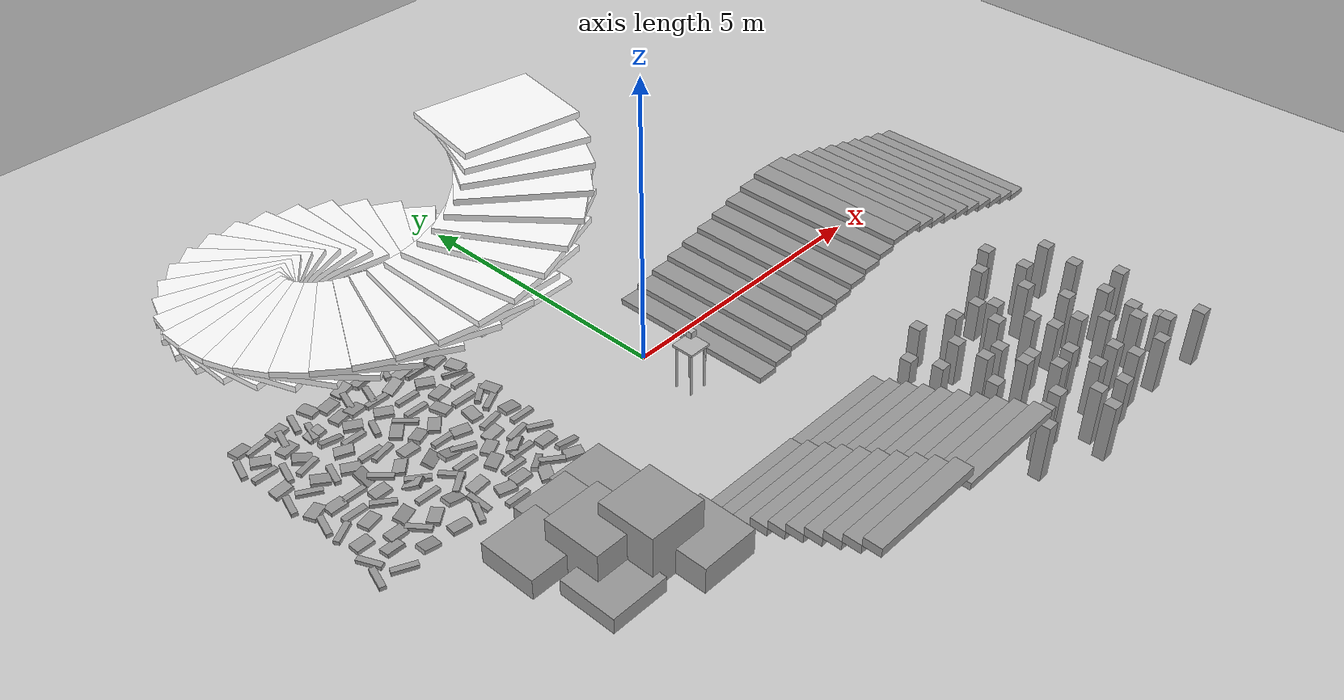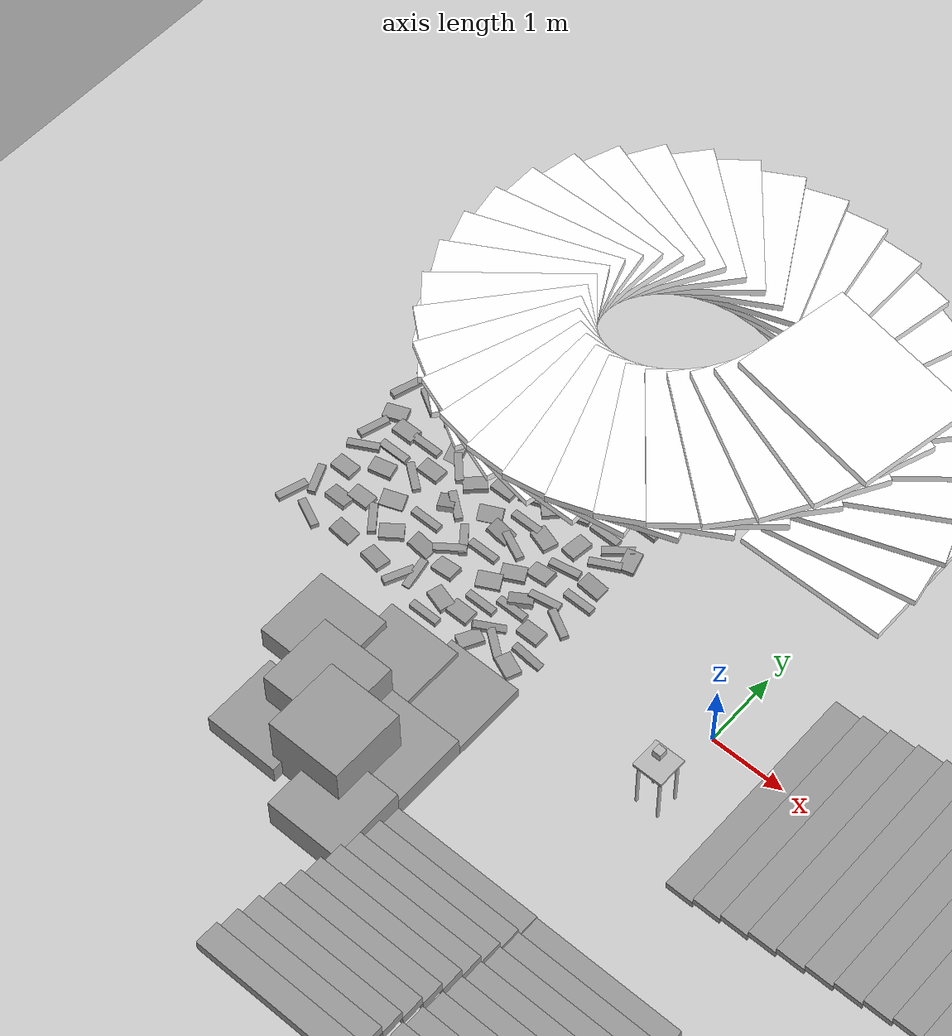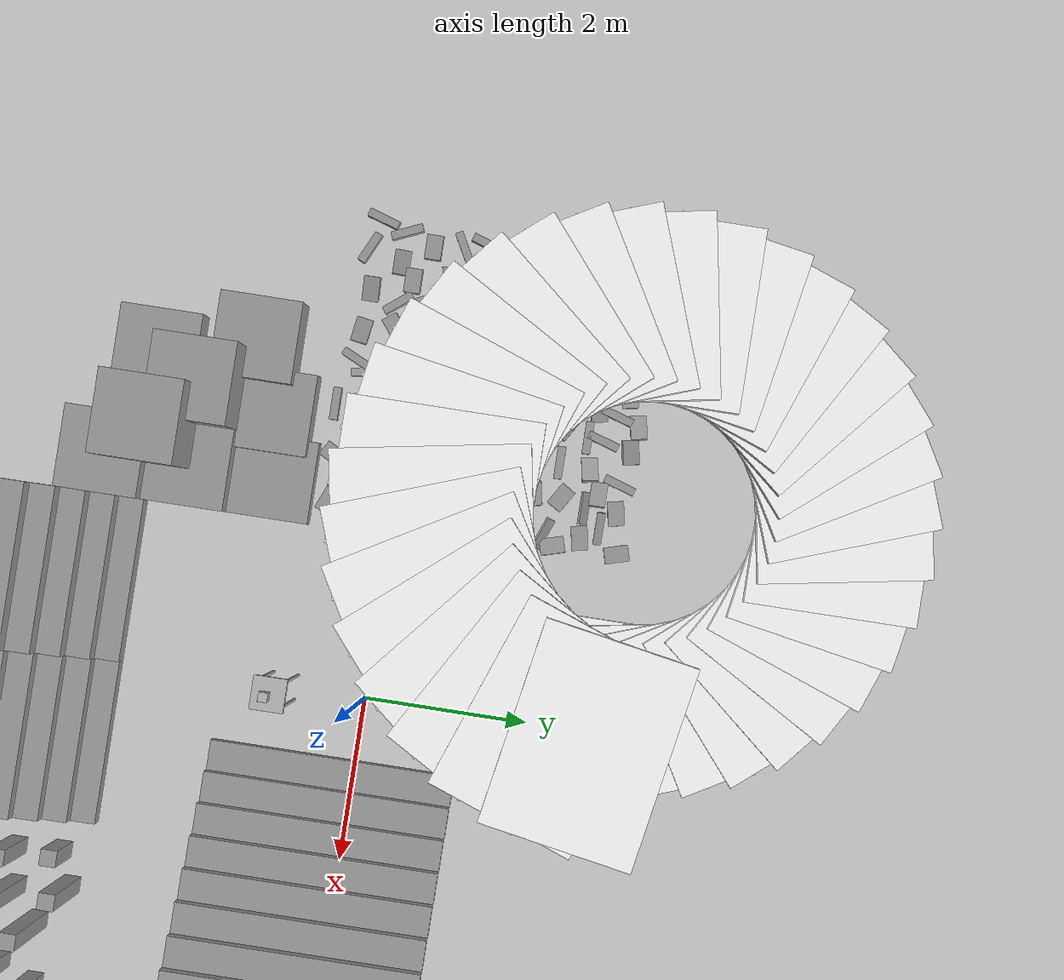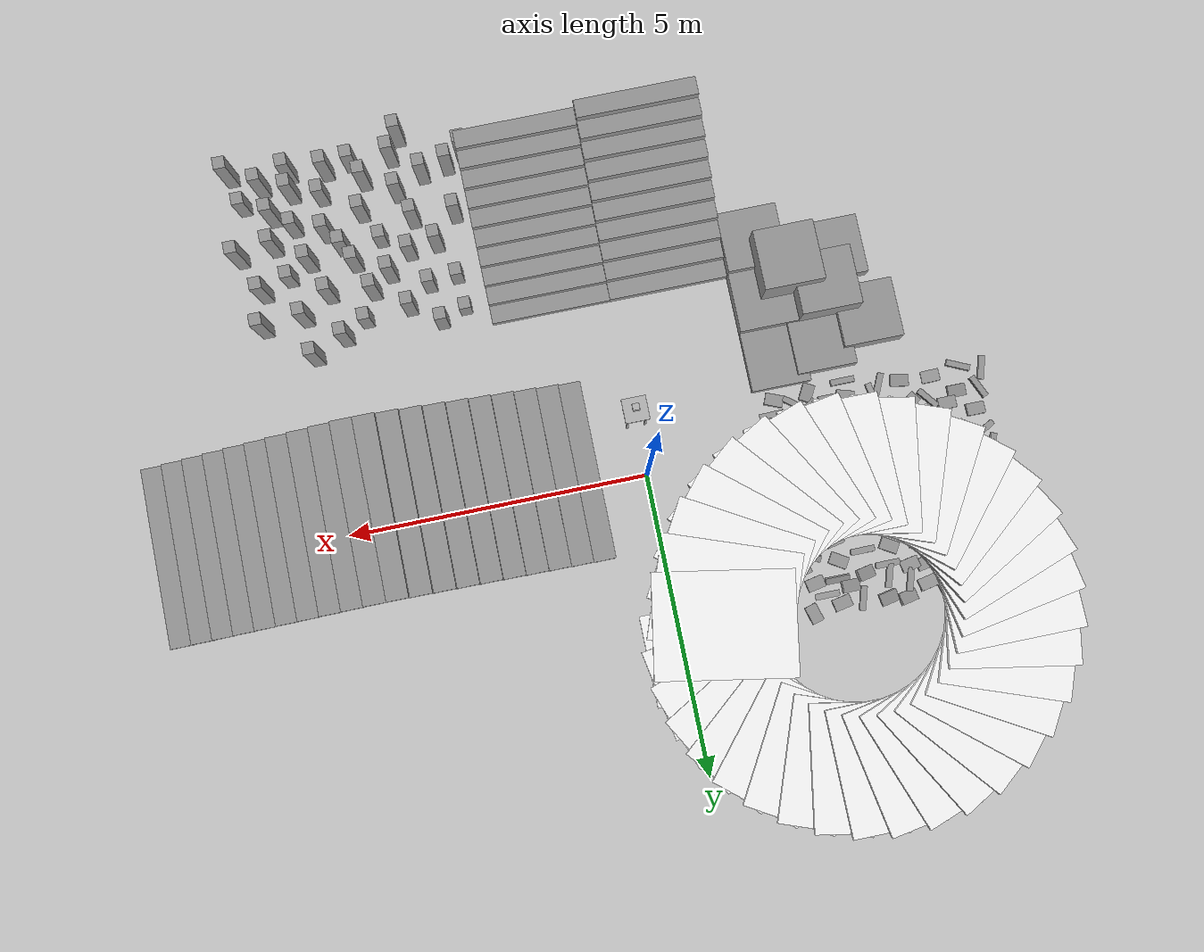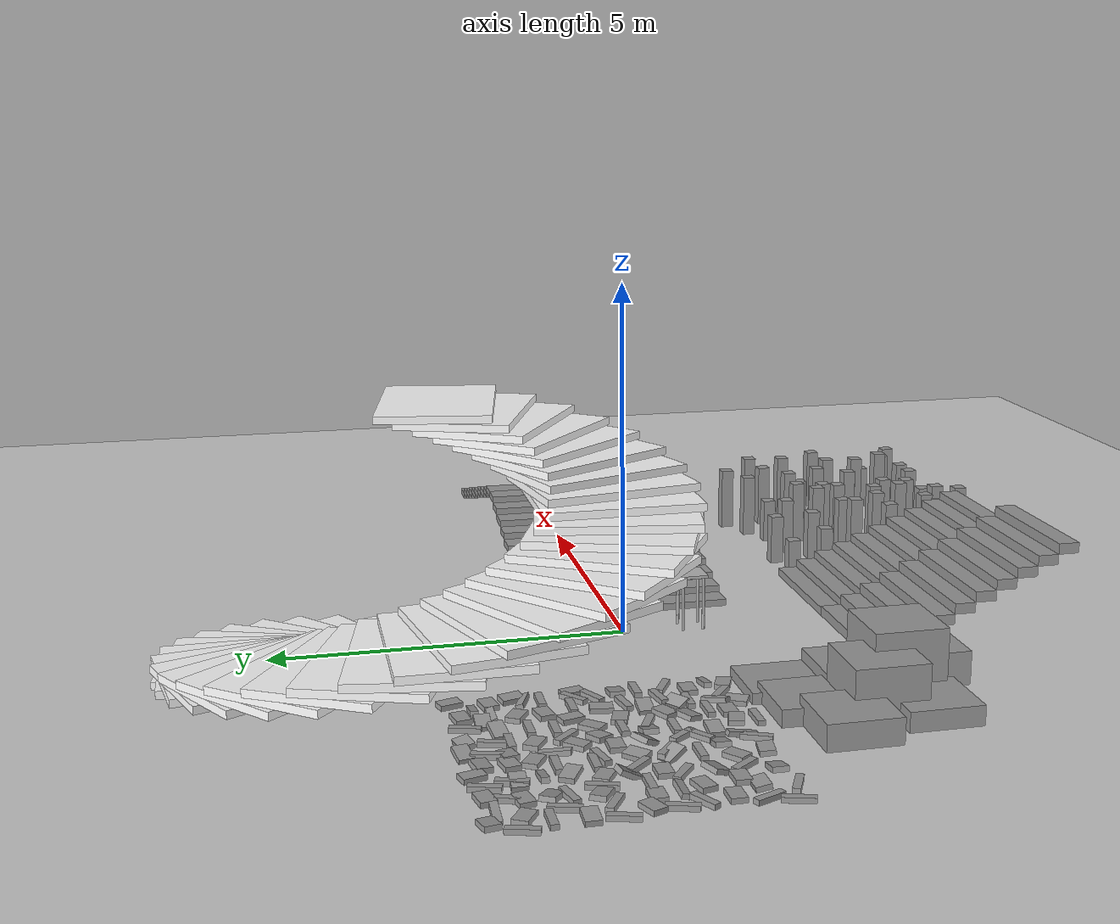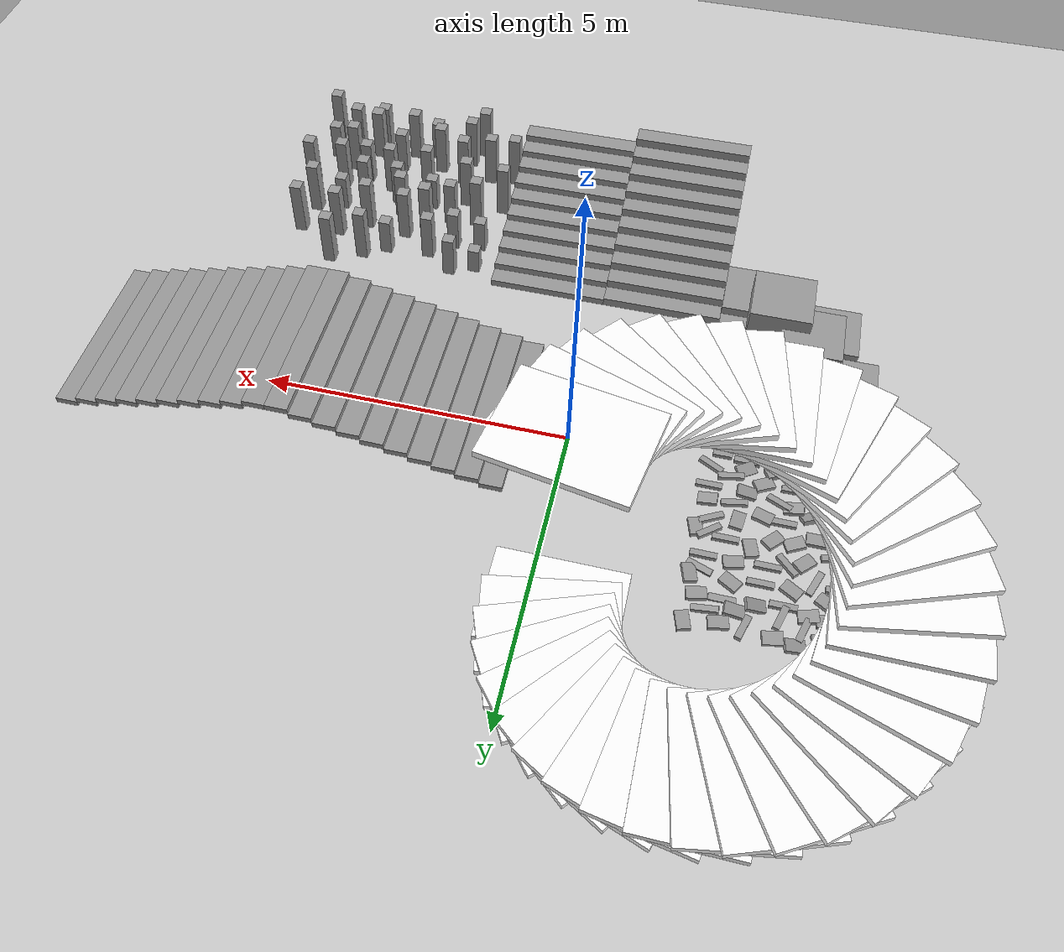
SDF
<sdf version="1.7">
 <world name="default">
  <light name="sun" type="directional">
   <pose>0 0 10 0 -0 0</pose>
   <diffuse>0.8 0.8 0.8 1</diffuse>
   <specular>0.2 0.2 0.2 1</specular>
   <attenuation>
    <range>1000</range>
    <constant>0.9</constant>
    <linear>0.01</linear>
    <quadratic>0.001</quadratic>
   </attenuation>
   <direction>-0.5 0.1 -0.9</direction>
   <spot><inner_angle>0</inner_angle><outer_angle>0</outer_angle><falloff>0</falloff></spot>
  </light>
  <model name="ground_plane">
   <static>1</static>
   <link name="link">
    <collision name="collision">
     <geometry><plane><normal>0 0 1</normal><size>100 100</size></plane></geometry>
     <surface><friction><ode><mu>200</mu><mu2>200</mu2></ode></friction></surface>
    </collision>
    <visual name="visual">
     <cast_shadows>0</cast_shadows>
     <geometry><plane><normal>0 0 1</normal><size>100 100</size></plane></geometry>
     <material>
      <script><uri>file://media/materials/scripts/gazebo.material</uri><name>Gazebo/Grey</name></script>
     </material>
    </visual>
   </link>
  </model>
  <gravity>0 0 -9.8</gravity>
  <magnetic_field>6e-06 2.3e-05 -4.2e-05</magnetic_field>
  <atmosphere type="adiabatic"/>
  <physics type="ode">
   <max_step_size>0.001</max_step_size>
   <real_time_factor>1</real_time_factor>
   <real_time_update_rate>1000</real_time_update_rate>
  </physics>
  <scene><ambient>0.4 0.4 0.4 1</ambient><background>0.7 0.7 0.7 1</background><shadows>1</shadows></scene>
  <spherical_coordinates>
   <surface_model>EARTH_WGS84</surface_model>
   <latitude_deg>0</latitude_deg>
   <longitude_deg>0</longitude_deg>
   <elevation>0</elevation>
   <heading_deg>0</heading_deg>
  </spherical_coordinates>
  <model name="stair_1">
   <pose>1.76459 -0.264334 0 0 -0 0</pose>
   <link name="Stairs_2">
    <visual name="Stairs_2_Visual_0">
     <pose>-0.81 0 0.05 0 -0 1.5708</pose>
     <geometry><box><size>3 0.37 0.1</size></box></geometry>
     <material>
      <script><uri>file://media/materials/scripts/gazebo.material</uri><name>Gazebo/Grey</name></script>
      <ambient>1 1 1 1</ambient>
     </material>
     <meta><layer>0</layer></meta>
    </visual>
    <collision name="Stairs_2_Collision_0">
     <geometry><box><size>3 0.37 0.1</size></box></geometry>
     <pose>-0.81 0 0.05 0 -0 1.5708</pose>
     <surface><friction><ode><mu>200</mu><mu2>200</mu2></ode></friction></surface>
    </collision>
    <visual name="Stairs_2_Visual_1">
     <pose>-0.44 0 0.15 0 -0 1.5708</pose>
     <geometry><box><size>3 0.37 0.1</size></box></geometry>
     <material>
      <script><uri>file://media/materials/scripts/gazebo.material</uri><name>Gazebo/Grey</name></script>
      <ambient>1 1 1 1</ambient>
     </material>
     <meta><layer>0</layer></meta>
    </visual>
    <collision name="Stairs_2_Collision_1">
     <geometry><box><size>3 0.37 0.1</size></box></geometry>
     <pose>-0.44 0 0.15 0 -0 1.5708</pose>
     <surface><friction><ode><mu>200</mu><mu2>200</mu2></ode></friction></surface>
    </collision>
    <visual name="Stairs_2_Visual_2">
     <pose>-0.07 0 0.25 0 -0 1.5708</pose>
     <geometry><box><size>3 0.37 0.1</size></box></geometry>
     <material>
      <script><uri>file://media/materials/scripts/gazebo.material</uri><name>Gazebo/Grey</name></script>
      <ambient>1 1 1 1</ambient>
     </material>
     <meta><layer>0</layer></meta>
    </visual>
    <collision name="Stairs_2_Collision_2">
     <geometry><box><size>3 0.37 0.1</size></box></geometry>
     <pose>-0.07 0 0.25 0 -0 1.5708</pose>
     <surface><friction><ode><mu>200</mu><mu2>200</mu2></ode></friction></surface>
    </collision>
    <visual name="Stairs_2_Visual_3">
     <pose>0.3 0 0.35 0 -0 1.5708</pose>
     <geometry><box><size>3 0.37 0.1</size></box></geometry>
     <material>
      <script><uri>file://media/materials/scripts/gazebo.material</uri><name>Gazebo/Grey</name></script>
      <ambient>1 1 1 1</ambient>
     </material>
     <meta><layer>0</layer></meta>
    </visual>
    <collision name="Stairs_2_Collision_3">
     <geometry><box><size>3 0.37 0.1</size></box></geometry>
     <pose>0.3 0 0.35 0 -0 1.5708</pose>
     <surface><friction><ode><mu>200</mu><mu2>200</mu2></ode></friction></surface>
    </collision>
    <visual name="Stairs_2_Visual_4">
     <pose>0.67 0 0.45 0 -0 1.5708</pose>
     <geometry><box><size>3 0.37 0.1</size></box></geometry>
     <material>
      <script><uri>file://media/materials/scripts/gazebo.material</uri><name>Gazebo/Grey</name></script>
      <ambient>1 1 1 1</ambient>
     </material>
     <meta><layer>0</layer></meta>
    </visual>
    <collision name="Stairs_2_Collision_4">
     <geometry><box><size>3 0.37 0.1</size></box></geometry>
     <pose>0.67 0 0.45 0 -0 1.5708</pose>
     <surface><friction><ode><mu>200</mu><mu2>200</mu2></ode></friction></surface>
    </collision>
    <visual name="Stairs_2_Visual_5">
     <pose>1.04 0 0.55 0 -0 1.5708</pose>
     <geometry><box><size>3 0.37 0.1</size></box></geometry>
     <material>
      <script><uri>file://media/materials/scripts/gazebo.material</uri><name>Gazebo/Grey</name></script>
      <ambient>1 1 1 1</ambient>
     </material>
     <meta><layer>0</layer></meta>
    </visual>
    <collision name="Stairs_2_Collision_5">
     <geometry><box><size>3 0.37 0.1</size></box></geometry>
     <pose>1.04 0 0.55 0 -0 1.5708</pose>
     <surface><friction><ode><mu>200</mu><mu2>200</mu2></ode></friction></surface>
    </collision>
    <visual name="Stairs_2_Visual_6">
     <pose>1.41 0 0.65 0 -0 1.5708</pose>
     <geometry><box><size>3 0.37 0.1</size></box></geometry>
     <material>
      <script><uri>file://media/materials/scripts/gazebo.material</uri><name>Gazebo/Grey</name></script>
      <ambient>1 1 1 1</ambient>
     </material>
     <meta><layer>0</layer></meta>
    </visual>
    <collision name="Stairs_2_Collision_6">
     <geometry><box><size>3 0.37 0.1</size></box></geometry>
     <pose>1.41 0 0.65 0 -0 1.5708</pose>
     <surface><friction><ode><mu>200</mu><mu2>200</mu2></ode></friction></surface>
    </collision>
    <visual name="Stairs_2_Visual_7">
     <pose>1.78 0 0.75 0 -0 1.5708</pose>
     <geometry><box><size>3 0.37 0.1</size></box></geometry>
     <material>
      <script><uri>file://media/materials/scripts/gazebo.material</uri><name>Gazebo/Grey</name></script>
      <ambient>1 1 1 1</ambient>
     </material>
     <meta><layer>0</layer></meta>
    </visual>
    <collision name="Stairs_2_Collision_7">
     <geometry><box><size>3 0.37 0.1</size></box></geometry>
     <pose>1.78 0 0.75 0 -0 1.5708</pose>
     <surface><friction><ode><mu>200</mu><mu2>200</mu2></ode></friction></surface>
    </collision>
    <visual name="Stairs_2_Visual_8">
     <pose>2.15 0 0.85 0 -0 1.5708</pose>
     <geometry><box><size>3 0.37 0.1</size></box></geometry>
     <material>
      <script><uri>file://media/materials/scripts/gazebo.material</uri><name>Gazebo/Grey</name></script>
      <ambient>1 1 1 1</ambient>
     </material>
     <meta><layer>0</layer></meta>
    </visual>
    <collision name="Stairs_2_Collision_8">
     <geometry><box><size>3 0.37 0.1</size></box></geometry>
     <pose>2.15 0 0.85 0 -0 1.5708</pose>
     <surface><friction><ode><mu>200</mu><mu2>200</mu2></ode></friction></surface>
    </collision>
    <visual name="Stairs_2_Visual_9">
     <pose>2.52 0 0.95 0 -0 1.5708</pose>
     <geometry><box><size>3 0.37 0.1</size></box></geometry>
     <material>
      <script><uri>file://media/materials/scripts/gazebo.material</uri><name>Gazebo/Grey</name></script>
      <ambient>1 1 1 1</ambient>
     </material>
     <meta><layer>0</layer></meta>
    </visual>
    <collision name="Stairs_2_Collision_9">
     <geometry><box><size>3 0.37 0.1</size></box></geometry>
     <pose>2.52 0 0.95 0 -0 1.5708</pose>
     <surface><friction><ode><mu>200</mu><mu2>200</mu2></ode></friction></surface>
    </collision>
   </link>
   <static>1</static>
  </model>
  <model name="box_0.3_0.2_0.1">
   <pose>-3.01255 1.36536 0 0 -0 1.85347</pose>
   <link name="Stairs_9">
    <visual name="Stairs_9_Visual_0">
     <pose>0 0 0.035 0 -0 0</pose>
     <geometry><box><size>0.3 0.2 0.07</size></box></geometry>
     <material>
      <script><uri>file://media/materials/scripts/gazebo.material</uri><name>Gazebo/Grey</name></script>
      <ambient>1 1 1 1</ambient>
     </material>
     <meta><layer>0</layer></meta>
    </visual>
    <collision name="Stairs_9_Collision_0">
     <geometry><box><size>0.3 0.2 0.07</size></box></geometry>
     <pose>0 0 0.035 0 -0 0</pose>
     <surface><friction><ode><mu>200</mu><mu2>200</mu2></ode></friction></surface>
    </collision>
   </link>
   <static>1</static>
  </model>
  <model name="box_0.4_0.1_0.07_1">
   <pose>-4.22701 1.2491 0 0 -0 0.237517</pose>
   <link name="Stairs_14">
    <visual name="Stairs_14_Visual_0">
     <pose>0 0 0.035 0 -0 0</pose>
     <geometry><box><size>0.4 0.1 0.07</size></box></geometry>
     <material>
      <script><uri>file://media/materials/scripts/gazebo.material</uri><name>Gazebo/Grey</name></script>
      <ambient>1 1 1 1</ambient>
     </material>
     <meta><layer>0</layer></meta>
    </visual>
    <collision name="Stairs_14_Collision_0">
     <geometry><box><size>0.4 0.1 0.07</size></box></geometry>
     <pose>0 0 0.035 0 -0 0</pose>
     <surface><friction><ode><mu>200</mu><mu2>200</mu2></ode></friction></surface>
    </collision>
   </link>
   <static>1</static>
  </model>
  <model name="box_0.4_0.1_0.07_3">
   <pose>-5.15876 1.80575 0 0 -0 0.249675</pose>
   <link name="Stairs_14">
    <visual name="Stairs_14_Visual_0">
     <pose>0 0 0.035 0 -0 0</pose>
     <geometry><box><size>0.4 0.1 0.07</size></box></geometry>
     <material>
      <script><uri>file://media/materials/scripts/gazebo.material</uri><name>Gazebo/Grey</name></script>
      <ambient>1 1 1 1</ambient>
     </material>
     <meta><layer>0</layer></meta>
    </visual>
    <collision name="Stairs_14_Collision_0">
     <geometry><box><size>0.4 0.1 0.07</size></box></geometry>
     <pose>0 0 0.035 0 -0 0</pose>
     <surface><friction><ode><mu>200</mu><mu2>200</mu2></ode></friction></surface>
    </collision>
   </link>
   <static>1</static>
  </model>
  <model name="box_0.4_0.1_0.07_5">
   <pose>-2.38032 1.20344 0 0 -0 0.675768</pose>
   <link name="Stairs_14">
    <visual name="Stairs_14_Visual_0">
     <pose>0 0 0.035 0 -0 0</pose>
     <geometry><box><size>0.4 0.1 0.07</size></box></geometry>
     <material>
      <script><uri>file://media/materials/scripts/gazebo.material</uri><name>Gazebo/Grey</name></script>
      <ambient>1 1 1 1</ambient>
     </material>
     <meta><layer>0</layer></meta>
    </visual>
    <collision name="Stairs_14_Collision_0">
     <geometry><box><size>0.4 0.1 0.07</size></box></geometry>
     <pose>0 0 0.035 0 -0 0</pose>
     <surface><friction><ode><mu>200</mu><mu2>200</mu2></ode></friction></surface>
    </collision>
   </link>
   <static>1</static>
  </model>
  <model name="box_0.4_0.1_0.07_6">
   <pose>-2.83467 -0.561057 0 0 0.21967 0.65136</pose>
   <link name="Stairs_14">
    <visual name="Stairs_14_Visual_0">
     <pose>0 0 0.035 0 -0 0</pose>
     <geometry><box><size>0.4 0.1 0.07</size></box></geometry>
     <material>
      <script><uri>file://media/materials/scripts/gazebo.material</uri><name>Gazebo/Grey</name></script>
      <ambient>1 1 1 1</ambient>
     </material>
     <meta><layer>0</layer></meta>
    </visual>
    <collision name="Stairs_14_Collision_0">
     <geometry><box><size>0.4 0.1 0.07</size></box></geometry>
     <pose>0 0 0.035 0 -0 0</pose>
     <surface><friction><ode><mu>200</mu><mu2>200</mu2></ode></friction></surface>
    </collision>
   </link>
   <static>1</static>
  </model>
  <model name="box_0.4_0.1_0.07_7">
   <pose>-3.9527 -0.560939 0 0 -0.198986 1.69782</pose>
   <link name="Stairs_14">
    <visual name="Stairs_14_Visual_0">
     <pose>0 0 0.035 0 -0 0</pose>
     <geometry><box><size>0.4 0.1 0.07</size></box></geometry>
     <material>
      <script><uri>file://media/materials/scripts/gazebo.material</uri><name>Gazebo/Grey</name></script>
      <ambient>1 1 1 1</ambient>
     </material>
     <meta><layer>0</layer></meta>
    </visual>
    <collision name="Stairs_14_Collision_0">
     <geometry><box><size>0.4 0.1 0.07</size></box></geometry>
     <pose>0 0 0.035 0 -0 0</pose>
     <surface><friction><ode><mu>200</mu><mu2>200</mu2></ode></friction></surface>
    </collision>
   </link>
   <static>1</static>
  </model>
  <model name="box_0.4_0.1_0.07_8">
   <pose>-3.35327 0.459325 0 0 0 -0.427504</pose>
   <link name="Stairs_14">
    <visual name="Stairs_14_Visual_0">
     <pose>0 0 0.035 0 -0 0</pose>
     <geometry><box><size>0.4 0.1 0.07</size></box></geometry>
     <material>
      <script><uri>file://media/materials/scripts/gazebo.material</uri><name>Gazebo/Grey</name></script>
      <ambient>1 1 1 1</ambient>
     </material>
     <meta><layer>0</layer></meta>
    </visual>
    <collision name="Stairs_14_Collision_0">
     <geometry><box><size>0.4 0.1 0.07</size></box></geometry>
     <pose>0 0 0.035 0 -0 0</pose>
     <surface><friction><ode><mu>200</mu><mu2>200</mu2></ode></friction></surface>
    </collision>
   </link>
   <static>1</static>
  </model>
  <model name="box_0.4_0.1_0.07_9">
   <pose>-3.84177 0.151803 0 0 0 -0.909347</pose>
   <link name="Stairs_14">
    <visual name="Stairs_14_Visual_0">
     <pose>0 0 0.035 0 -0 0</pose>
     <geometry><box><size>0.4 0.1 0.07</size></box></geometry>
     <material>
      <script><uri>file://media/materials/scripts/gazebo.material</uri><name>Gazebo/Grey</name></script>
      <ambient>1 1 1 1</ambient>
     </material>
     <meta><layer>0</layer></meta>
    </visual>
    <collision name="Stairs_14_Collision_0">
     <geometry><box><size>0.4 0.1 0.07</size></box></geometry>
     <pose>0 0 0.035 0 -0 0</pose>
     <surface><friction><ode><mu>200</mu><mu2>200</mu2></ode></friction></surface>
    </collision>
   </link>
   <static>1</static>
  </model>
  <model name="box_0.4_0.1_0.07_10">
   <pose>-2.5817 0.133983 0 0 -0 0.188316</pose>
   <link name="Stairs_14">
    <visual name="Stairs_14_Visual_0">
     <pose>0 0 0.035 0 -0 0</pose>
     <geometry><box><size>0.4 0.1 0.07</size></box></geometry>
     <material>
      <script><uri>file://media/materials/scripts/gazebo.material</uri><name>Gazebo/Grey</name></script>
      <ambient>1 1 1 1</ambient>
     </material>
     <meta><layer>0</layer></meta>
    </visual>
    <collision name="Stairs_14_Collision_0">
     <geometry><box><size>0.4 0.1 0.07</size></box></geometry>
     <pose>0 0 0.035 0 -0 0</pose>
     <surface><friction><ode><mu>200</mu><mu2>200</mu2></ode></friction></surface>
    </collision>
   </link>
   <static>1</static>
  </model>
  <model name="box_0.3_0.2_0.1_1">
   <pose>-2.32668 -0.803117 0 0 0 -0.389703</pose>
   <link name="Stairs_9">
    <visual name="Stairs_9_Visual_0">
     <pose>0 0 0.035 0 -0 0</pose>
     <geometry><box><size>0.3 0.2 0.07</size></box></geometry>
     <material>
      <script><uri>file://media/materials/scripts/gazebo.material</uri><name>Gazebo/Grey</name></script>
      <ambient>1 1 1 1</ambient>
     </material>
     <meta><layer>0</layer></meta>
    </visual>
    <collision name="Stairs_9_Collision_0">
     <geometry><box><size>0.3 0.2 0.07</size></box></geometry>
     <pose>0 0 0.035 0 -0 0</pose>
     <surface><friction><ode><mu>200</mu><mu2>200</mu2></ode></friction></surface>
    </collision>
   </link>
   <static>1</static>
  </model>
  <model name="box_0.3_0.2_0.1_2">
   <pose>-3.24691 -0.07902 0 0.162224 -0 0.485941</pose>
   <link name="Stairs_9">
    <visual name="Stairs_9_Visual_0">
     <pose>0 0 0.035 0 -0 0</pose>
     <geometry><box><size>0.3 0.2 0.07</size></box></geometry>
     <material>
      <script><uri>file://media/materials/scripts/gazebo.material</uri><name>Gazebo/Grey</name></script>
      <ambient>1 1 1 1</ambient>
     </material>
     <meta><layer>0</layer></meta>
    </visual>
    <collision name="Stairs_9_Collision_0">
     <geometry><box><size>0.3 0.2 0.07</size></box></geometry>
     <pose>0 0 0.035 0 -0 0</pose>
     <surface><friction><ode><mu>200</mu><mu2>200</mu2></ode></friction></surface>
    </collision>
   </link>
   <static>1</static>
  </model>
  <model name="box_0.3_0.2_0.1_4">
   <pose>-3.50067 -0.629827 0 0 0 -0.287884</pose>
   <link name="Stairs_9">
    <visual name="Stairs_9_Visual_0">
     <pose>0 0 0.035 0 -0 0</pose>
     <geometry><box><size>0.3 0.2 0.07</size></box></geometry>
     <material>
      <script><uri>file://media/materials/scripts/gazebo.material</uri><name>Gazebo/Grey</name></script>
      <ambient>1 1 1 1</ambient>
     </material>
     <meta><layer>0</layer></meta>
    </visual>
    <collision name="Stairs_9_Collision_0">
     <geometry><box><size>0.3 0.2 0.07</size></box></geometry>
     <pose>0 0 0.035 0 -0 0</pose>
     <surface><friction><ode><mu>200</mu><mu2>200</mu2></ode></friction></surface>
    </collision>
   </link>
   <static>1</static>
  </model>
  <model name="box_0.3_0.2_0.1_6">
   <pose>-2.40905 -0.299713 0 0 -0 0</pose>
   <link name="Stairs_9">
    <visual name="Stairs_9_Visual_0">
     <pose>0 0 0.035 0 -0 0</pose>
     <geometry><box><size>0.3 0.2 0.07</size></box></geometry>
     <material>
      <script><uri>file://media/materials/scripts/gazebo.material</uri><name>Gazebo/Grey</name></script>
      <ambient>1 1 1 1</ambient>
     </material>
     <meta><layer>0</layer></meta>
    </visual>
    <collision name="Stairs_9_Collision_0">
     <geometry><box><size>0.3 0.2 0.07</size></box></geometry>
     <pose>0 0 0.035 0 -0 0</pose>
     <surface><friction><ode><mu>200</mu><mu2>200</mu2></ode></friction></surface>
    </collision>
   </link>
   <static>1</static>
  </model>
  <model name="box_0.3_0.2_0.1_7">
   <pose>-2.29296 0.634577 0 0 0.156533 0</pose>
   <link name="Stairs_9">
    <visual name="Stairs_9_Visual_0">
     <pose>0 0 0.035 0 -0 0</pose>
     <geometry><box><size>0.3 0.2 0.07</size></box></geometry>
     <material>
      <script><uri>file://media/materials/scripts/gazebo.material</uri><name>Gazebo/Grey</name></script>
      <ambient>1 1 1 1</ambient>
     </material>
     <meta><layer>0</layer></meta>
    </visual>
    <collision name="Stairs_9_Collision_0">
     <geometry><box><size>0.3 0.2 0.07</size></box></geometry>
     <pose>0 0 0.035 0 -0 0</pose>
     <surface><friction><ode><mu>200</mu><mu2>200</mu2></ode></friction></surface>
    </collision>
   </link>
   <static>1</static>
  </model>
  <model name="box_0.3_0.2_0.1_8">
   <pose>-4.59337 1.6807 0 -0 -0.139114 -0.545678</pose>
   <link name="Stairs_9">
    <visual name="Stairs_9_Visual_0">
     <pose>0 0 0.035 0 -0 0</pose>
     <geometry><box><size>0.3 0.2 0.07</size></box></geometry>
     <material>
      <script><uri>file://media/materials/scripts/gazebo.material</uri><name>Gazebo/Grey</name></script>
      <ambient>1 1 1 1</ambient>
     </material>
     <meta><layer>0</layer></meta>
    </visual>
    <collision name="Stairs_9_Collision_0">
     <geometry><box><size>0.3 0.2 0.07</size></box></geometry>
     <pose>0 0 0.035 0 -0 0</pose>
     <surface><friction><ode><mu>200</mu><mu2>200</mu2></ode></friction></surface>
    </collision>
   </link>
   <static>1</static>
  </model>
  <model name="box_0.3_0.2_0.1_9">
   <pose>-2.79379 1.66334 0 0 -0 0.193818</pose>
   <link name="Stairs_9">
    <visual name="Stairs_9_Visual_0">
     <pose>0 0 0.035 0 -0 0</pose>
     <geometry><box><size>0.3 0.2 0.07</size></box></geometry>
     <material>
      <script><uri>file://media/materials/scripts/gazebo.material</uri><name>Gazebo/Grey</name></script>
      <ambient>1 1 1 1</ambient>
     </material>
     <meta><layer>0</layer></meta>
    </visual>
    <collision name="Stairs_9_Collision_0">
     <geometry><box><size>0.3 0.2 0.07</size></box></geometry>
     <pose>0 0 0.035 0 -0 0</pose>
     <surface><friction><ode><mu>200</mu><mu2>200</mu2></ode></friction></surface>
    </collision>
   </link>
   <static>1</static>
  </model>
  <model name="box_0.3_0.2_0.1_10">
   <pose>-4.24662 0.814175 0 -0.148606 -0 0.746465</pose>
   <link name="Stairs_9">
    <visual name="Stairs_9_Visual_0">
     <pose>0 0 0.035 0 -0 0</pose>
     <geometry><box><size>0.3 0.2 0.07</size></box></geometry>
     <material>
      <script><uri>file://media/materials/scripts/gazebo.material</uri><name>Gazebo/Grey</name></script>
      <ambient>1 1 1 1</ambient>
     </material>
     <meta><layer>0</layer></meta>
    </visual>
    <collision name="Stairs_9_Collision_0">
     <geometry><box><size>0.3 0.2 0.07</size></box></geometry>
     <pose>0 0 0.035 0 -0 0</pose>
     <surface><friction><ode><mu>200</mu><mu2>200</mu2></ode></friction></surface>
    </collision>
   </link>
   <static>1</static>
  </model>
  <model name="box_0.3_0.2_0.1_11">
   <pose>-4.83425 0.032148 0 0.293641 -0 0.364797</pose>
   <link name="Stairs_9">
    <visual name="Stairs_9_Visual_0">
     <pose>0 0 0.035 0 -0 0</pose>
     <geometry><box><size>0.3 0.2 0.07</size></box></geometry>
     <material>
      <script><uri>file://media/materials/scripts/gazebo.material</uri><name>Gazebo/Grey</name></script>
      <ambient>1 1 1 1</ambient>
     </material>
     <meta><layer>0</layer></meta>
    </visual>
    <collision name="Stairs_9_Collision_0">
     <geometry><box><size>0.3 0.2 0.07</size></box></geometry>
     <pose>0 0 0.035 0 -0 0</pose>
     <surface><friction><ode><mu>200</mu><mu2>200</mu2></ode></friction></surface>
    </collision>
   </link>
   <static>1</static>
  </model>
  <model name="box_0.3_0.2_0.1_13">
   <pose>-4.44487 -0.717451 0 -0.093999 -0 -0.154705</pose>
   <link name="Stairs_9">
    <visual name="Stairs_9_Visual_0">
     <pose>0 0 0.035 0 -0 0</pose>
     <geometry><box><size>0.3 0.2 0.07</size></box></geometry>
     <material>
      <script><uri>file://media/materials/scripts/gazebo.material</uri><name>Gazebo/Grey</name></script>
      <ambient>1 1 1 1</ambient>
     </material>
     <meta><layer>0</layer></meta>
    </visual>
    <collision name="Stairs_9_Collision_0">
     <geometry><box><size>0.3 0.2 0.07</size></box></geometry>
     <pose>0 0 0.035 0 -0 0</pose>
     <surface><friction><ode><mu>200</mu><mu2>200</mu2></ode></friction></surface>
    </collision>
   </link>
   <static>1</static>
  </model>
  <model name="box_0.3_0.2_0.1_14">
   <pose>-3.13761 0.765182 0 0 0 -0.305362</pose>
   <link name="Stairs_9">
    <visual name="Stairs_9_Visual_0">
     <pose>0 0 0.035 0 -0 0</pose>
     <geometry><box><size>0.3 0.2 0.07</size></box></geometry>
     <material>
      <script><uri>file://media/materials/scripts/gazebo.material</uri><name>Gazebo/Grey</name></script>
      <ambient>1 1 1 1</ambient>
     </material>
     <meta><layer>0</layer></meta>
    </visual>
    <collision name="Stairs_9_Collision_0">
     <geometry><box><size>0.3 0.2 0.07</size></box></geometry>
     <pose>0 0 0.035 0 -0 0</pose>
     <surface><friction><ode><mu>200</mu><mu2>200</mu2></ode></friction></surface>
    </collision>
   </link>
   <static>1</static>
  </model>
  <model name="box_0.4_0.1_0.07_12">
   <pose>-3.56494 1.53175 0 0 0 -0.796152</pose>
   <link name="Stairs_14">
    <visual name="Stairs_14_Visual_0">
     <pose>0 0 0.035 0 -0 0</pose>
     <geometry><box><size>0.4 0.1 0.07</size></box></geometry>
     <material>
      <script><uri>file://media/materials/scripts/gazebo.material</uri><name>Gazebo/Grey</name></script>
      <ambient>1 1 1 1</ambient>
     </material>
     <meta><layer>0</layer></meta>
    </visual>
    <collision name="Stairs_14_Collision_0">
     <geometry><box><size>0.4 0.1 0.07</size></box></geometry>
     <pose>0 0 0.035 0 -0 0</pose>
     <surface><friction><ode><mu>200</mu><mu2>200</mu2></ode></friction></surface>
    </collision>
   </link>
   <static>1</static>
  </model>
  <model name="box_0.3_0.2_0.1_15">
   <pose>-3.64159 1.14014 0 0 0.114836 0.429416</pose>
   <link name="Stairs_9">
    <visual name="Stairs_9_Visual_0">
     <pose>0 0 0.035 0 -0 0</pose>
     <geometry><box><size>0.3 0.2 0.07</size></box></geometry>
     <material>
      <script><uri>file://media/materials/scripts/gazebo.material</uri><name>Gazebo/Grey</name></script>
      <ambient>1 1 1 1</ambient>
     </material>
     <meta><layer>0</layer></meta>
    </visual>
    <collision name="Stairs_9_Collision_0">
     <geometry><box><size>0.3 0.2 0.07</size></box></geometry>
     <pose>0 0 0.035 0 -0 0</pose>
     <surface><friction><ode><mu>200</mu><mu2>200</mu2></ode></friction></surface>
    </collision>
   </link>
   <static>1</static>
  </model>
  <model name="box_0.3_0.2_0.1_18">
   <pose>-5.13742 -0.186069 0 0 -0 0</pose>
   <link name="Stairs_9">
    <visual name="Stairs_9_Visual_0">
     <pose>0 0 0.035 0 -0 0</pose>
     <geometry><box><size>0.3 0.2 0.07</size></box></geometry>
     <material>
      <script><uri>file://media/materials/scripts/gazebo.material</uri><name>Gazebo/Grey</name></script>
      <ambient>1 1 1 1</ambient>
     </material>
     <meta><layer>0</layer></meta>
    </visual>
    <collision name="Stairs_9_Collision_0">
     <geometry><box><size>0.3 0.2 0.07</size></box></geometry>
     <pose>0 0 0.035 0 -0 0</pose>
     <surface><friction><ode><mu>200</mu><mu2>200</mu2></ode></friction></surface>
    </collision>
   </link>
   <static>1</static>
  </model>
  <model name="box_0.4_0.1_0.07_13">
   <pose>-4.87489 0.421648 0 0 0 -0.645463</pose>
   <link name="Stairs_14">
    <visual name="Stairs_14_Visual_0">
     <pose>0 0 0.035 0 -0 0</pose>
     <geometry><box><size>0.4 0.1 0.07</size></box></geometry>
     <material>
      <script><uri>file://media/materials/scripts/gazebo.material</uri><name>Gazebo/Grey</name></script>
      <ambient>1 1 1 1</ambient>
     </material>
     <meta><layer>0</layer></meta>
    </visual>
    <collision name="Stairs_14_Collision_0">
     <geometry><box><size>0.4 0.1 0.07</size></box></geometry>
     <pose>0 0 0.035 0 -0 0</pose>
     <surface><friction><ode><mu>200</mu><mu2>200</mu2></ode></friction></surface>
    </collision>
   </link>
   <static>1</static>
  </model>
  <model name="box_0.4_0.1_0.07_14">
   <pose>-5.05743 0.85867 0 0 -0 0</pose>
   <link name="Stairs_14">
    <visual name="Stairs_14_Visual_0">
     <pose>0 0 0.035 0 -0 0</pose>
     <geometry><box><size>0.4 0.1 0.07</size></box></geometry>
     <material>
      <script><uri>file://media/materials/scripts/gazebo.material</uri><name>Gazebo/Grey</name></script>
      <ambient>1 1 1 1</ambient>
     </material>
     <meta><layer>0</layer></meta>
    </visual>
    <collision name="Stairs_14_Collision_0">
     <geometry><box><size>0.4 0.1 0.07</size></box></geometry>
     <pose>0 0 0.035 0 -0 0</pose>
     <surface><friction><ode><mu>200</mu><mu2>200</mu2></ode></friction></surface>
    </collision>
   </link>
   <static>1</static>
  </model>
  <model name="box_0.4_0.1_0.07_15">
   <pose>-5.63027 0.375388 0 0 -0 0.50181</pose>
   <link name="Stairs_14">
    <visual name="Stairs_14_Visual_0">
     <pose>0 0 0.035 0 -0 0</pose>
     <geometry><box><size>0.4 0.1 0.07</size></box></geometry>
     <material>
      <script><uri>file://media/materials/scripts/gazebo.material</uri><name>Gazebo/Grey</name></script>
      <ambient>1 1 1 1</ambient>
     </material>
     <meta><layer>0</layer></meta>
    </visual>
    <collision name="Stairs_14_Collision_0">
     <geometry><box><size>0.4 0.1 0.07</size></box></geometry>
     <pose>0 0 0.035 0 -0 0</pose>
     <surface><friction><ode><mu>200</mu><mu2>200</mu2></ode></friction></surface>
    </collision>
   </link>
   <static>1</static>
  </model>
  <model name="box_0.4_0.1_0.07_16">
   <pose>-5.7174 -0.345289 0 0 0 -1.15775</pose>
   <link name="Stairs_14">
    <visual name="Stairs_14_Visual_0">
     <pose>0 0 0.035 0 -0 0</pose>
     <geometry><box><size>0.4 0.1 0.07</size></box></geometry>
     <material>
      <script><uri>file://media/materials/scripts/gazebo.material</uri><name>Gazebo/Grey</name></script>
      <ambient>1 1 1 1</ambient>
     </material>
     <meta><layer>0</layer></meta>
    </visual>
    <collision name="Stairs_14_Collision_0">
     <geometry><box><size>0.4 0.1 0.07</size></box></geometry>
     <pose>0 0 0.035 0 -0 0</pose>
     <surface><friction><ode><mu>200</mu><mu2>200</mu2></ode></friction></surface>
    </collision>
   </link>
   <static>1</static>
  </model>
  <model name="box_0.4_0.1_0.07_17">
   <pose>-5.45955 -0.765501 0 0 0 -0.432025</pose>
   <link name="Stairs_14">
    <visual name="Stairs_14_Visual_0">
     <pose>0 0 0.035 0 -0 0</pose>
     <geometry><box><size>0.4 0.1 0.07</size></box></geometry>
     <material>
      <script><uri>file://media/materials/scripts/gazebo.material</uri><name>Gazebo/Grey</name></script>
      <ambient>1 1 1 1</ambient>
     </material>
     <meta><layer>0</layer></meta>
    </visual>
    <collision name="Stairs_14_Collision_0">
     <geometry><box><size>0.4 0.1 0.07</size></box></geometry>
     <pose>0 0 0.035 0 -0 0</pose>
     <surface><friction><ode><mu>200</mu><mu2>200</mu2></ode></friction></surface>
    </collision>
   </link>
   <static>1</static>
  </model>
  <model name="box_0.4_0.1_0.07_19">
   <pose>-5.45893 1.35645 0 0 0 -0.532767</pose>
   <link name="Stairs_14">
    <visual name="Stairs_14_Visual_0">
     <pose>0 0 0.035 0 -0 0</pose>
     <geometry><box><size>0.4 0.1 0.07</size></box></geometry>
     <material>
      <script><uri>file://media/materials/scripts/gazebo.material</uri><name>Gazebo/Grey</name></script>
      <ambient>1 1 1 1</ambient>
     </material>
     <meta><layer>0</layer></meta>
    </visual>
    <collision name="Stairs_14_Collision_0">
     <geometry><box><size>0.4 0.1 0.07</size></box></geometry>
     <pose>0 0 0.035 0 -0 0</pose>
     <surface><friction><ode><mu>200</mu><mu2>200</mu2></ode></friction></surface>
    </collision>
   </link>
   <static>1</static>
  </model>
  <model name="box_0.3_0.2_0.1_21">
   <pose>-4.73627 1.04564 0 -0 0.500671 -1.39294</pose>
   <link name="Stairs_9">
    <visual name="Stairs_9_Visual_0">
     <pose>0 0 0.035 0 -0 0</pose>
     <geometry><box><size>0.3 0.2 0.07</size></box></geometry>
     <material>
      <script><uri>file://media/materials/scripts/gazebo.material</uri><name>Gazebo/Grey</name></script>
      <ambient>1 1 1 1</ambient>
     </material>
     <meta><layer>0</layer></meta>
    </visual>
    <collision name="Stairs_9_Collision_0">
     <geometry><box><size>0.3 0.2 0.07</size></box></geometry>
     <pose>0 0 0.035 0 -0 0</pose>
     <surface><friction><ode><mu>200</mu><mu2>200</mu2></ode></friction></surface>
    </collision>
   </link>
   <static>1</static>
  </model>
  <model name="box_0.4_0.1_0.07_20">
   <pose>-3.98209 1.73954 0 0 0.150582 1.18314</pose>
   <link name="Stairs_14">
    <visual name="Stairs_14_Visual_0">
     <pose>0 0 0.035 0 -0 0</pose>
     <geometry><box><size>0.4 0.1 0.07</size></box></geometry>
     <material>
      <script><uri>file://media/materials/scripts/gazebo.material</uri><name>Gazebo/Grey</name></script>
      <ambient>1 1 1 1</ambient>
     </material>
     <meta><layer>0</layer></meta>
    </visual>
    <collision name="Stairs_14_Collision_0">
     <geometry><box><size>0.4 0.1 0.07</size></box></geometry>
     <pose>0 0 0.035 0 -0 0</pose>
     <surface><friction><ode><mu>200</mu><mu2>200</mu2></ode></friction></surface>
    </collision>
   </link>
   <static>1</static>
  </model>
  <model name="box_0.4_0.1_0.07_21">
   <pose>-2.33177 1.84563 0 -0.297405 -0 -0.354338</pose>
   <link name="Stairs_14">
    <visual name="Stairs_14_Visual_0">
     <pose>0 0 0.035 0 -0 0</pose>
     <geometry><box><size>0.4 0.1 0.07</size></box></geometry>
     <material>
      <script><uri>file://media/materials/scripts/gazebo.material</uri><name>Gazebo/Grey</name></script>
      <ambient>1 1 1 1</ambient>
     </material>
     <meta><layer>0</layer></meta>
    </visual>
    <collision name="Stairs_14_Collision_0">
     <geometry><box><size>0.4 0.1 0.07</size></box></geometry>
     <pose>0 0 0.035 0 -0 0</pose>
     <surface><friction><ode><mu>200</mu><mu2>200</mu2></ode></friction></surface>
    </collision>
   </link>
   <static>1</static>
  </model>
  <model name="box_0.3_0.2_0.1_22">
   <pose>-5.70698 1.67913 0 0 -0.108326 0</pose>
   <link name="Stairs_9">
    <visual name="Stairs_9_Visual_0">
     <pose>0 0 0.035 0 -0 0</pose>
     <geometry><box><size>0.3 0.2 0.07</size></box></geometry>
     <material>
      <script><uri>file://media/materials/scripts/gazebo.material</uri><name>Gazebo/Grey</name></script>
      <ambient>1 1 1 1</ambient>
     </material>
     <meta><layer>0</layer></meta>
    </visual>
    <collision name="Stairs_9_Collision_0">
     <geometry><box><size>0.3 0.2 0.07</size></box></geometry>
     <pose>0 0 0.035 0 -0 0</pose>
     <surface><friction><ode><mu>200</mu><mu2>200</mu2></ode></friction></surface>
    </collision>
   </link>
   <static>1</static>
  </model>
  <model name="box_0.3_0.2_0.1_23">
   <pose>-5.64621 0.971865 0 0 -0 0.388929</pose>
   <link name="Stairs_9">
    <visual name="Stairs_9_Visual_0">
     <pose>0 0 0.035 0 -0 0</pose>
     <geometry><box><size>0.3 0.2 0.07</size></box></geometry>
     <material>
      <script><uri>file://media/materials/scripts/gazebo.material</uri><name>Gazebo/Grey</name></script>
      <ambient>1 1 1 1</ambient>
     </material>
     <meta><layer>0</layer></meta>
    </visual>
    <collision name="Stairs_9_Collision_0">
     <geometry><box><size>0.3 0.2 0.07</size></box></geometry>
     <pose>0 0 0.035 0 -0 0</pose>
     <surface><friction><ode><mu>200</mu><mu2>200</mu2></ode></friction></surface>
    </collision>
   </link>
   <static>1</static>
  </model>
  <model name="box_0.4_0.1_0.07_22">
   <pose>-4.35317 0.072456 0 0 -0 0</pose>
   <link name="Stairs_14">
    <visual name="Stairs_14_Visual_0">
     <pose>0 0 0.035 0 -0 0</pose>
     <geometry><box><size>0.4 0.1 0.07</size></box></geometry>
     <material>
      <script><uri>file://media/materials/scripts/gazebo.material</uri><name>Gazebo/Grey</name></script>
      <ambient>1 1 1 1</ambient>
     </material>
     <meta><layer>0</layer></meta>
    </visual>
    <collision name="Stairs_14_Collision_0">
     <geometry><box><size>0.4 0.1 0.07</size></box></geometry>
     <pose>0 0 0.035 0 -0 0</pose>
     <surface><friction><ode><mu>200</mu><mu2>200</mu2></ode></friction></surface>
    </collision>
   </link>
   <static>1</static>
  </model>
  <model name="box_0.3_0.2_0.1_24">
   <pose>-3.84361 0.632082 0 0.414489 -0 0.464126</pose>
   <link name="Stairs_9">
    <visual name="Stairs_9_Visual_0">
     <pose>0 0 0.035 0 -0 0</pose>
     <geometry><box><size>0.3 0.2 0.07</size></box></geometry>
     <material>
      <script><uri>file://media/materials/scripts/gazebo.material</uri><name>Gazebo/Grey</name></script>
      <ambient>1 1 1 1</ambient>
     </material>
     <meta><layer>0</layer></meta>
    </visual>
    <collision name="Stairs_9_Collision_0">
     <geometry><box><size>0.3 0.2 0.07</size></box></geometry>
     <pose>0 0 0.035 0 -0 0</pose>
     <surface><friction><ode><mu>200</mu><mu2>200</mu2></ode></friction></surface>
    </collision>
   </link>
   <static>1</static>
  </model>
  <model name="box_0.3_0.2_0.1_25">
   <pose>-2.77079 0.926758 0 0.04132 0.005073 -1.6929</pose>
   <link name="Stairs_9">
    <visual name="Stairs_9_Visual_0">
     <pose>0 0 0.035 0 -0 0</pose>
     <geometry><box><size>0.3 0.2 0.07</size></box></geometry>
     <material>
      <script><uri>file://media/materials/scripts/gazebo.material</uri><name>Gazebo/Grey</name></script>
      <ambient>1 1 1 1</ambient>
     </material>
     <meta><layer>0</layer></meta>
    </visual>
    <collision name="Stairs_9_Collision_0">
     <geometry><box><size>0.3 0.2 0.07</size></box></geometry>
     <pose>0 0 0.035 0 -0 0</pose>
     <surface><friction><ode><mu>200</mu><mu2>200</mu2></ode></friction></surface>
    </collision>
   </link>
   <static>1</static>
  </model>
  <model name="box_0.3_0.2_0.1_26">
   <pose>-2.84302 0.380803 0 0 -0.200079 0</pose>
   <link name="Stairs_9">
    <visual name="Stairs_9_Visual_0">
     <pose>0 0 0.035 0 -0 0</pose>
     <geometry><box><size>0.3 0.2 0.07</size></box></geometry>
     <material>
      <script><uri>file://media/materials/scripts/gazebo.material</uri><name>Gazebo/Grey</name></script>
      <ambient>1 1 1 1</ambient>
     </material>
     <meta><layer>0</layer></meta>
    </visual>
    <collision name="Stairs_9_Collision_0">
     <geometry><box><size>0.3 0.2 0.07</size></box></geometry>
     <pose>0 0 0.035 0 -0 0</pose>
     <surface><friction><ode><mu>200</mu><mu2>200</mu2></ode></friction></surface>
    </collision>
   </link>
   <static>1</static>
  </model>
  <model name="box_0.3_0.2_0.1_27">
   <pose>-4.33028 0.401558 0 0 -0.4283 -1.0174</pose>
   <link name="Stairs_9">
    <visual name="Stairs_9_Visual_0">
     <pose>0 0 0.035 0 -0 0</pose>
     <geometry><box><size>0.3 0.2 0.07</size></box></geometry>
     <material>
      <script><uri>file://media/materials/scripts/gazebo.material</uri><name>Gazebo/Grey</name></script>
      <ambient>1 1 1 1</ambient>
     </material>
     <meta><layer>0</layer></meta>
    </visual>
    <collision name="Stairs_9_Collision_0">
     <geometry><box><size>0.3 0.2 0.07</size></box></geometry>
     <pose>0 0 0.035 0 -0 0</pose>
     <surface><friction><ode><mu>200</mu><mu2>200</mu2></ode></friction></surface>
    </collision>
   </link>
   <static>1</static>
  </model>
  <model name="box_0.3_0.2_0.1_28">
   <pose>-3.72262 -0.283281 0 0 -0.157712 0</pose>
   <link name="Stairs_9">
    <visual name="Stairs_9_Visual_0">
     <pose>0 0 0.035 0 -0 0</pose>
     <geometry><box><size>0.3 0.2 0.07</size></box></geometry>
     <material>
      <script><uri>file://media/materials/scripts/gazebo.material</uri><name>Gazebo/Grey</name></script>
      <ambient>1 1 1 1</ambient>
     </material>
     <meta><layer>0</layer></meta>
    </visual>
    <collision name="Stairs_9_Collision_0">
     <geometry><box><size>0.3 0.2 0.07</size></box></geometry>
     <pose>0 0 0.035 0 -0 0</pose>
     <surface><friction><ode><mu>200</mu><mu2>200</mu2></ode></friction></surface>
    </collision>
   </link>
   <static>1</static>
  </model>
  <model name="box_0.3_0.2_0.1_29">
   <pose>-4.54474 -0.31953 0 0 -0 0.647578</pose>
   <link name="Stairs_9">
    <visual name="Stairs_9_Visual_0">
     <pose>0 0 0.035 0 -0 0</pose>
     <geometry><box><size>0.3 0.2 0.07</size></box></geometry>
     <material>
      <script><uri>file://media/materials/scripts/gazebo.material</uri><name>Gazebo/Grey</name></script>
      <ambient>1 1 1 1</ambient>
     </material>
     <meta><layer>0</layer></meta>
    </visual>
    <collision name="Stairs_9_Collision_0">
     <geometry><box><size>0.3 0.2 0.07</size></box></geometry>
     <pose>0 0 0.035 0 -0 0</pose>
     <surface><friction><ode><mu>200</mu><mu2>200</mu2></ode></friction></surface>
    </collision>
   </link>
   <static>1</static>
  </model>
  <model name="box_0.3_0.2_0.1_30">
   <pose>-2.88822 -0.819464 -0.007875 -0.086933 -0 1.07781</pose>
   <link name="Stairs_9">
    <visual name="Stairs_9_Visual_0">
     <pose>0 0 0.035 0 -0 0</pose>
     <geometry><box><size>0.3 0.2 0.07</size></box></geometry>
     <material>
      <script><uri>file://media/materials/scripts/gazebo.material</uri><name>Gazebo/Grey</name></script>
      <ambient>1 1 1 1</ambient>
     </material>
     <meta><layer>0</layer></meta>
    </visual>
    <collision name="Stairs_9_Collision_0">
     <geometry><box><size>0.3 0.2 0.07</size></box></geometry>
     <pose>0 0 0.035 0 -0 0</pose>
     <surface><friction><ode><mu>200</mu><mu2>200</mu2></ode></friction></surface>
    </collision>
   </link>
   <static>1</static>
  </model>
  <model name="box_0.4_0.1_0.07_23">
   <pose>-2.79254 -0.199709 0 0 -0 0</pose>
   <link name="Stairs_14">
    <visual name="Stairs_14_Visual_0">
     <pose>0 0 0.035 0 -0 0</pose>
     <geometry><box><size>0.4 0.1 0.07</size></box></geometry>
     <material>
      <script><uri>file://media/materials/scripts/gazebo.material</uri><name>Gazebo/Grey</name></script>
      <ambient>1 1 1 1</ambient>
     </material>
     <meta><layer>0</layer></meta>
    </visual>
    <collision name="Stairs_14_Collision_0">
     <geometry><box><size>0.4 0.1 0.07</size></box></geometry>
     <pose>0 0 0.035 0 -0 0</pose>
     <surface><friction><ode><mu>200</mu><mu2>200</mu2></ode></friction></surface>
    </collision>
   </link>
   <static>1</static>
  </model>
  <model name="box_0.4_0.1_0.07_24">
   <pose>-3.55858 0.179353 0 0 -0 0</pose>
   <link name="Stairs_14">
    <visual name="Stairs_14_Visual_0">
     <pose>0 0 0.035 0 -0 0</pose>
     <geometry><box><size>0.4 0.1 0.07</size></box></geometry>
     <material>
      <script><uri>file://media/materials/scripts/gazebo.material</uri><name>Gazebo/Grey</name></script>
      <ambient>1 1 1 1</ambient>
     </material>
     <meta><layer>0</layer></meta>
    </visual>
    <collision name="Stairs_14_Collision_0">
     <geometry><box><size>0.4 0.1 0.07</size></box></geometry>
     <pose>0 0 0.035 0 -0 0</pose>
     <surface><friction><ode><mu>200</mu><mu2>200</mu2></ode></friction></surface>
    </collision>
   </link>
   <static>1</static>
  </model>
  <model name="box_0.4_0.1_0.07_25">
   <pose>-3.29164 1.61754 0 0 -0 0</pose>
   <link name="Stairs_14">
    <visual name="Stairs_14_Visual_0">
     <pose>0 0 0.035 0 -0 0</pose>
     <geometry><box><size>0.4 0.1 0.07</size></box></geometry>
     <material>
      <script><uri>file://media/materials/scripts/gazebo.material</uri><name>Gazebo/Grey</name></script>
      <ambient>1 1 1 1</ambient>
     </material>
     <meta><layer>0</layer></meta>
    </visual>
    <collision name="Stairs_14_Collision_0">
     <geometry><box><size>0.4 0.1 0.07</size></box></geometry>
     <pose>0 0 0.035 0 -0 0</pose>
     <surface><friction><ode><mu>200</mu><mu2>200</mu2></ode></friction></surface>
    </collision>
   </link>
   <static>1</static>
  </model>
  <model name="box_0.4_0.1_0.07_26">
   <pose>-4.08505 -0.7108 0 0 -0 1.13869</pose>
   <link name="Stairs_14">
    <visual name="Stairs_14_Visual_0">
     <pose>0 0 0.035 0 -0 0</pose>
     <geometry><box><size>0.4 0.1 0.07</size></box></geometry>
     <material>
      <script><uri>file://media/materials/scripts/gazebo.material</uri><name>Gazebo/Grey</name></script>
      <ambient>1 1 1 1</ambient>
     </material>
     <meta><layer>0</layer></meta>
    </visual>
    <collision name="Stairs_14_Collision_0">
     <geometry><box><size>0.4 0.1 0.07</size></box></geometry>
     <pose>0 0 0.035 0 -0 0</pose>
     <surface><friction><ode><mu>200</mu><mu2>200</mu2></ode></friction></surface>
    </collision>
   </link>
   <static>1</static>
  </model>
  <model name="box_0.4_0.1_0.07_27">
   <pose>-3.51215 -0.893933 0 0 -0 0</pose>
   <link name="Stairs_14">
    <visual name="Stairs_14_Visual_0">
     <pose>0 0 0.035 0 -0 0</pose>
     <geometry><box><size>0.4 0.1 0.07</size></box></geometry>
     <material>
      <script><uri>file://media/materials/scripts/gazebo.material</uri><name>Gazebo/Grey</name></script>
      <ambient>1 1 1 1</ambient>
     </material>
     <meta><layer>0</layer></meta>
    </visual>
    <collision name="Stairs_14_Collision_0">
     <geometry><box><size>0.4 0.1 0.07</size></box></geometry>
     <pose>0 0 0.035 0 -0 0</pose>
     <surface><friction><ode><mu>200</mu><mu2>200</mu2></ode></friction></surface>
    </collision>
   </link>
   <static>1</static>
  </model>
  <model name="box_0.4_0.1_0.07_28">
   <pose>-5.00471 1.39941 0 0 -0 1.2714</pose>
   <link name="Stairs_14">
    <visual name="Stairs_14_Visual_0">
     <pose>0 0 0.035 0 -0 0</pose>
     <geometry><box><size>0.4 0.1 0.07</size></box></geometry>
     <material>
      <script><uri>file://media/materials/scripts/gazebo.material</uri><name>Gazebo/Grey</name></script>
      <ambient>1 1 1 1</ambient>
     </material>
     <meta><layer>0</layer></meta>
    </visual>
    <collision name="Stairs_14_Collision_0">
     <geometry><box><size>0.4 0.1 0.07</size></box></geometry>
     <pose>0 0 0.035 0 -0 0</pose>
     <surface><friction><ode><mu>200</mu><mu2>200</mu2></ode></friction></surface>
    </collision>
   </link>
   <static>1</static>
  </model>
  <model name="box_0.3_0.2_0.1_31">
   <pose>-5.23263 0.276548 0 0 -0 0.243446</pose>
   <link name="Stairs_9">
    <visual name="Stairs_9_Visual_0">
     <pose>0 0 0.035 0 -0 0</pose>
     <geometry><box><size>0.3 0.2 0.07</size></box></geometry>
     <material>
      <script><uri>file://media/materials/scripts/gazebo.material</uri><name>Gazebo/Grey</name></script>
      <ambient>1 1 1 1</ambient>
     </material>
     <meta><layer>0</layer></meta>
    </visual>
    <collision name="Stairs_9_Collision_0">
     <geometry><box><size>0.3 0.2 0.07</size></box></geometry>
     <pose>0 0 0.035 0 -0 0</pose>
     <surface><friction><ode><mu>200</mu><mu2>200</mu2></ode></friction></surface>
    </collision>
   </link>
   <static>1</static>
  </model>
  <model name="box_0.3_0.2_0.1_32">
   <pose>-3.94269 1.00447 0 0 -0 0</pose>
   <link name="Stairs_9">
    <visual name="Stairs_9_Visual_0">
     <pose>0 0 0.035 0 -0 0</pose>
     <geometry><box><size>0.3 0.2 0.07</size></box></geometry>
     <material>
      <script><uri>file://media/materials/scripts/gazebo.material</uri><name>Gazebo/Grey</name></script>
      <ambient>1 1 1 1</ambient>
     </material>
     <meta><layer>0</layer></meta>
    </visual>
    <collision name="Stairs_9_Collision_0">
     <geometry><box><size>0.3 0.2 0.07</size></box></geometry>
     <pose>0 0 0.035 0 -0 0</pose>
     <surface><friction><ode><mu>200</mu><mu2>200</mu2></ode></friction></surface>
    </collision>
   </link>
   <static>1</static>
  </model>
  <model name="box_0.3_0.2_0.1_33">
   <pose>-3.58843 0.511656 0 0 0.248657 0</pose>
   <link name="Stairs_9">
    <visual name="Stairs_9_Visual_0">
     <pose>0 0 0.035 0 -0 0</pose>
     <geometry><box><size>0.3 0.2 0.07</size></box></geometry>
     <material>
      <script><uri>file://media/materials/scripts/gazebo.material</uri><name>Gazebo/Grey</name></script>
      <ambient>1 1 1 1</ambient>
     </material>
     <meta><layer>0</layer></meta>
    </visual>
    <collision name="Stairs_9_Collision_0">
     <geometry><box><size>0.3 0.2 0.07</size></box></geometry>
     <pose>0 0 0.035 0 -0 0</pose>
     <surface><friction><ode><mu>200</mu><mu2>200</mu2></ode></friction></surface>
    </collision>
   </link>
   <static>1</static>
  </model>
  <model name="box_0.3_0.2_0.1_34">
   <pose>-4.15327 -0.23297 0 0 0.224487 0</pose>
   <link name="Stairs_9">
    <visual name="Stairs_9_Visual_0">
     <pose>0 0 0.035 0 -0 0</pose>
     <geometry><box><size>0.3 0.2 0.07</size></box></geometry>
     <material>
      <script><uri>file://media/materials/scripts/gazebo.material</uri><name>Gazebo/Grey</name></script>
      <ambient>1 1 1 1</ambient>
     </material>
     <meta><layer>0</layer></meta>
    </visual>
    <collision name="Stairs_9_Collision_0">
     <geometry><box><size>0.3 0.2 0.07</size></box></geometry>
     <pose>0 0 0.035 0 -0 0</pose>
     <surface><friction><ode><mu>200</mu><mu2>200</mu2></ode></friction></surface>
    </collision>
   </link>
   <static>1</static>
  </model>
  <model name="box_0.3_0.2_0.1_35">
   <pose>-4.76651 0.628506 0 0 -0 0</pose>
   <link name="Stairs_9">
    <visual name="Stairs_9_Visual_0">
     <pose>0 0 0.035 0 -0 0</pose>
     <geometry><box><size>0.3 0.2 0.07</size></box></geometry>
     <material>
      <script><uri>file://media/materials/scripts/gazebo.material</uri><name>Gazebo/Grey</name></script>
      <ambient>1 1 1 1</ambient>
     </material>
     <meta><layer>0</layer></meta>
    </visual>
    <collision name="Stairs_9_Collision_0">
     <geometry><box><size>0.3 0.2 0.07</size></box></geometry>
     <pose>0 0 0.035 0 -0 0</pose>
     <surface><friction><ode><mu>200</mu><mu2>200</mu2></ode></friction></surface>
    </collision>
   </link>
   <static>1</static>
  </model>
  <model name="box_0.3_0.2_0.1_36">
   <pose>-3.2043 -0.611051 0 0 -0 0</pose>
   <link name="Stairs_9">
    <visual name="Stairs_9_Visual_0">
     <pose>0 0 0.035 0 -0 0</pose>
     <geometry><box><size>0.3 0.2 0.07</size></box></geometry>
     <material>
      <script><uri>file://media/materials/scripts/gazebo.material</uri><name>Gazebo/Grey</name></script>
      <ambient>1 1 1 1</ambient>
     </material>
     <meta><layer>0</layer></meta>
    </visual>
    <collision name="Stairs_9_Collision_0">
     <geometry><box><size>0.3 0.2 0.07</size></box></geometry>
     <pose>0 0 0.035 0 -0 0</pose>
     <surface><friction><ode><mu>200</mu><mu2>200</mu2></ode></friction></surface>
    </collision>
   </link>
   <static>1</static>
  </model>
  <model name="box_0.3_0.2_0.1_37">
   <pose>-5.33812 -0.362217 0 -0.173222 0 0</pose>
   <link name="Stairs_9">
    <visual name="Stairs_9_Visual_0">
     <pose>0 0 0.035 0 -0 0</pose>
     <geometry><box><size>0.3 0.2 0.07</size></box></geometry>
     <material>
      <script><uri>file://media/materials/scripts/gazebo.material</uri><name>Gazebo/Grey</name></script>
      <ambient>1 1 1 1</ambient>
     </material>
     <meta><layer>0</layer></meta>
    </visual>
    <collision name="Stairs_9_Collision_0">
     <geometry><box><size>0.3 0.2 0.07</size></box></geometry>
     <pose>0 0 0.035 0 -0 0</pose>
     <surface><friction><ode><mu>200</mu><mu2>200</mu2></ode></friction></surface>
    </collision>
   </link>
   <static>1</static>
  </model>
  <model name="box_0.3_0.2_0.1_38">
   <pose>-4.97391 -0.676954 0 0 0.207576 0</pose>
   <link name="Stairs_9">
    <visual name="Stairs_9_Visual_0">
     <pose>0 0 0.035 0 -0 0</pose>
     <geometry><box><size>0.3 0.2 0.07</size></box></geometry>
     <material>
      <script><uri>file://media/materials/scripts/gazebo.material</uri><name>Gazebo/Grey</name></script>
      <ambient>1 1 1 1</ambient>
     </material>
     <meta><layer>0</layer></meta>
    </visual>
    <collision name="Stairs_9_Collision_0">
     <geometry><box><size>0.3 0.2 0.07</size></box></geometry>
     <pose>0 0 0.035 0 -0 0</pose>
     <surface><friction><ode><mu>200</mu><mu2>200</mu2></ode></friction></surface>
    </collision>
   </link>
   <static>1</static>
  </model>
  <model name="box_0.3_0.2_0.1_39">
   <pose>-5.37394 0.854881 0 0 -0 0</pose>
   <link name="Stairs_9">
    <visual name="Stairs_9_Visual_0">
     <pose>0 0 0.035 0 -0 0</pose>
     <geometry><box><size>0.3 0.2 0.07</size></box></geometry>
     <material>
      <script><uri>file://media/materials/scripts/gazebo.material</uri><name>Gazebo/Grey</name></script>
      <ambient>1 1 1 1</ambient>
     </material>
     <meta><layer>0</layer></meta>
    </visual>
    <collision name="Stairs_9_Collision_0">
     <geometry><box><size>0.3 0.2 0.07</size></box></geometry>
     <pose>0 0 0.035 0 -0 0</pose>
     <surface><friction><ode><mu>200</mu><mu2>200</mu2></ode></friction></surface>
    </collision>
   </link>
   <static>1</static>
  </model>
  <model name="box_0.3_0.2_0.1_40">
   <pose>-3.80623 1.44414 0 0 -0 0.786502</pose>
   <link name="Stairs_9">
    <visual name="Stairs_9_Visual_0">
     <pose>0 0 0.035 0 -0 0</pose>
     <geometry><box><size>0.3 0.2 0.07</size></box></geometry>
     <material>
      <script><uri>file://media/materials/scripts/gazebo.material</uri><name>Gazebo/Grey</name></script>
      <ambient>1 1 1 1</ambient>
     </material>
     <meta><layer>0</layer></meta>
    </visual>
    <collision name="Stairs_9_Collision_0">
     <geometry><box><size>0.3 0.2 0.07</size></box></geometry>
     <pose>0 0 0.035 0 -0 0</pose>
     <surface><friction><ode><mu>200</mu><mu2>200</mu2></ode></friction></surface>
    </collision>
   </link>
   <static>1</static>
  </model>
  <model name="box_0.3_0.2_0.1_41">
   <pose>-3.32408 1.15403 0 0 -0 0.81582</pose>
   <link name="Stairs_9">
    <visual name="Stairs_9_Visual_0">
     <pose>0 0 0.035 0 -0 0</pose>
     <geometry><box><size>0.3 0.2 0.07</size></box></geometry>
     <material>
      <script><uri>file://media/materials/scripts/gazebo.material</uri><name>Gazebo/Grey</name></script>
      <ambient>1 1 1 1</ambient>
     </material>
     <meta><layer>0</layer></meta>
    </visual>
    <collision name="Stairs_9_Collision_0">
     <geometry><box><size>0.3 0.2 0.07</size></box></geometry>
     <pose>0 0 0.035 0 -0 0</pose>
     <surface><friction><ode><mu>200</mu><mu2>200</mu2></ode></friction></surface>
    </collision>
   </link>
   <static>1</static>
  </model>
  <model name="box_0.3_0.2_0.1_42">
   <pose>-2.78828 -0.052875 0 -0.371727 -0 0.579103</pose>
   <link name="Stairs_9">
    <visual name="Stairs_9_Visual_0">
     <pose>0 0 0.035 0 -0 0</pose>
     <geometry><box><size>0.3 0.2 0.07</size></box></geometry>
     <material>
      <script><uri>file://media/materials/scripts/gazebo.material</uri><name>Gazebo/Grey</name></script>
      <ambient>1 1 1 1</ambient>
     </material>
     <meta><layer>0</layer></meta>
    </visual>
    <collision name="Stairs_9_Collision_0">
     <geometry><box><size>0.3 0.2 0.07</size></box></geometry>
     <pose>0 0 0.035 0 -0 0</pose>
     <surface><friction><ode><mu>200</mu><mu2>200</mu2></ode></friction></surface>
    </collision>
   </link>
   <static>1</static>
  </model>
  <model name="box_0.3_0.2_0.1_44">
   <pose>-5.57863 0.004751 0 0 -0 0</pose>
   <link name="Stairs_9">
    <visual name="Stairs_9_Visual_0">
     <pose>0 0 0.035 0 -0 0</pose>
     <geometry><box><size>0.3 0.2 0.07</size></box></geometry>
     <material>
      <script><uri>file://media/materials/scripts/gazebo.material</uri><name>Gazebo/Grey</name></script>
      <ambient>1 1 1 1</ambient>
     </material>
     <meta><layer>0</layer></meta>
    </visual>
    <collision name="Stairs_9_Collision_0">
     <geometry><box><size>0.3 0.2 0.07</size></box></geometry>
     <pose>0 0 0.035 0 -0 0</pose>
     <surface><friction><ode><mu>200</mu><mu2>200</mu2></ode></friction></surface>
    </collision>
   </link>
   <static>1</static>
  </model>
  <model name="box_0.4_0.1_0.07_29">
   <pose>-3.43843 0.808641 0 0 -0 0</pose>
   <link name="Stairs_14">
    <visual name="Stairs_14_Visual_0">
     <pose>0 0 0.035 0 -0 0</pose>
     <geometry><box><size>0.4 0.1 0.07</size></box></geometry>
     <material>
      <script><uri>file://media/materials/scripts/gazebo.material</uri><name>Gazebo/Grey</name></script>
      <ambient>1 1 1 1</ambient>
     </material>
     <meta><layer>0</layer></meta>
    </visual>
    <collision name="Stairs_14_Collision_0">
     <geometry><box><size>0.4 0.1 0.07</size></box></geometry>
     <pose>0 0 0.035 0 -0 0</pose>
     <surface><friction><ode><mu>200</mu><mu2>200</mu2></ode></friction></surface>
    </collision>
   </link>
   <static>1</static>
  </model>
  <model name="box_0.4_0.1_0.07_30">
   <pose>-3.88412 -0.047896 0 0 -0 0.646358</pose>
   <link name="Stairs_14">
    <visual name="Stairs_14_Visual_0">
     <pose>0 0 0.035 0 -0 0</pose>
     <geometry><box><size>0.4 0.1 0.07</size></box></geometry>
     <material>
      <script><uri>file://media/materials/scripts/gazebo.material</uri><name>Gazebo/Grey</name></script>
      <ambient>1 1 1 1</ambient>
     </material>
     <meta><layer>0</layer></meta>
    </visual>
    <collision name="Stairs_14_Collision_0">
     <geometry><box><size>0.4 0.1 0.07</size></box></geometry>
     <pose>0 0 0.035 0 -0 0</pose>
     <surface><friction><ode><mu>200</mu><mu2>200</mu2></ode></friction></surface>
    </collision>
   </link>
   <static>1</static>
  </model>
  <model name="box_0.4_0.1_0.07_31">
   <pose>-2.24494 -0.568367 0 0 0.191516 0</pose>
   <link name="Stairs_14">
    <visual name="Stairs_14_Visual_0">
     <pose>0 0 0.035 0 -0 0</pose>
     <geometry><box><size>0.4 0.1 0.07</size></box></geometry>
     <material>
      <script><uri>file://media/materials/scripts/gazebo.material</uri><name>Gazebo/Grey</name></script>
      <ambient>1 1 1 1</ambient>
     </material>
     <meta><layer>0</layer></meta>
    </visual>
    <collision name="Stairs_14_Collision_0">
     <geometry><box><size>0.4 0.1 0.07</size></box></geometry>
     <pose>0 0 0.035 0 -0 0</pose>
     <surface><friction><ode><mu>200</mu><mu2>200</mu2></ode></friction></surface>
    </collision>
   </link>
   <static>1</static>
  </model>
  <model name="box_0.4_0.1_0.07_32">
   <pose>-2.26101 -0.007459 0 0 0 -0.492553</pose>
   <link name="Stairs_14">
    <visual name="Stairs_14_Visual_0">
     <pose>0 0 0.035 0 -0 0</pose>
     <geometry><box><size>0.4 0.1 0.07</size></box></geometry>
     <material>
      <script><uri>file://media/materials/scripts/gazebo.material</uri><name>Gazebo/Grey</name></script>
      <ambient>1 1 1 1</ambient>
     </material>
     <meta><layer>0</layer></meta>
    </visual>
    <collision name="Stairs_14_Collision_0">
     <geometry><box><size>0.4 0.1 0.07</size></box></geometry>
     <pose>0 0 0.035 0 -0 0</pose>
     <surface><friction><ode><mu>200</mu><mu2>200</mu2></ode></friction></surface>
    </collision>
   </link>
   <static>1</static>
  </model>
  <model name="box_0.4_0.1_0.07_33">
   <pose>-2.2734 0.372881 0 0 -0 0</pose>
   <link name="Stairs_14">
    <visual name="Stairs_14_Visual_0">
     <pose>0 0 0.035 0 -0 0</pose>
     <geometry><box><size>0.4 0.1 0.07</size></box></geometry>
     <material>
      <script><uri>file://media/materials/scripts/gazebo.material</uri><name>Gazebo/Grey</name></script>
      <ambient>1 1 1 1</ambient>
     </material>
     <meta><layer>0</layer></meta>
    </visual>
    <collision name="Stairs_14_Collision_0">
     <geometry><box><size>0.4 0.1 0.07</size></box></geometry>
     <pose>0 0 0.035 0 -0 0</pose>
     <surface><friction><ode><mu>200</mu><mu2>200</mu2></ode></friction></surface>
    </collision>
   </link>
   <static>1</static>
  </model>
  <model name="box_0.4_0.1_0.07_34">
   <pose>-2.37805 0.96323 0 0 -0 0.493596</pose>
   <link name="Stairs_14">
    <visual name="Stairs_14_Visual_0">
     <pose>0 0 0.035 0 -0 0</pose>
     <geometry><box><size>0.4 0.1 0.07</size></box></geometry>
     <material>
      <script><uri>file://media/materials/scripts/gazebo.material</uri><name>Gazebo/Grey</name></script>
      <ambient>1 1 1 1</ambient>
     </material>
     <meta><layer>0</layer></meta>
    </visual>
    <collision name="Stairs_14_Collision_0">
     <geometry><box><size>0.4 0.1 0.07</size></box></geometry>
     <pose>0 0 0.035 0 -0 0</pose>
     <surface><friction><ode><mu>200</mu><mu2>200</mu2></ode></friction></surface>
    </collision>
   </link>
   <static>1</static>
  </model>
  <model name="box_0.4_0.1_0.07_35">
   <pose>-2.3534 1.63255 0 0 -0 0</pose>
   <link name="Stairs_14">
    <visual name="Stairs_14_Visual_0">
     <pose>0 0 0.035 0 -0 0</pose>
     <geometry><box><size>0.4 0.1 0.07</size></box></geometry>
     <material>
      <script><uri>file://media/materials/scripts/gazebo.material</uri><name>Gazebo/Grey</name></script>
      <ambient>1 1 1 1</ambient>
     </material>
     <meta><layer>0</layer></meta>
    </visual>
    <collision name="Stairs_14_Collision_0">
     <geometry><box><size>0.4 0.1 0.07</size></box></geometry>
     <pose>0 0 0.035 0 -0 0</pose>
     <surface><friction><ode><mu>200</mu><mu2>200</mu2></ode></friction></surface>
    </collision>
   </link>
   <static>1</static>
  </model>
  <model name="box_0.4_0.1_0.07_36">
   <pose>-2.63647 1.28112 0 0 -0 0</pose>
   <link name="Stairs_14">
    <visual name="Stairs_14_Visual_0">
     <pose>0 0 0.035 0 -0 0</pose>
     <geometry><box><size>0.4 0.1 0.07</size></box></geometry>
     <material>
      <script><uri>file://media/materials/scripts/gazebo.material</uri><name>Gazebo/Grey</name></script>
      <ambient>1 1 1 1</ambient>
     </material>
     <meta><layer>0</layer></meta>
    </visual>
    <collision name="Stairs_14_Collision_0">
     <geometry><box><size>0.4 0.1 0.07</size></box></geometry>
     <pose>0 0 0.035 0 -0 0</pose>
     <surface><friction><ode><mu>200</mu><mu2>200</mu2></ode></friction></surface>
    </collision>
   </link>
   <static>1</static>
  </model>
  <model name="box_0.4_0.1_0.07_38">
   <pose>-4.36607 1.34865 0 0 -0 0</pose>
   <link name="Stairs_14">
    <visual name="Stairs_14_Visual_0">
     <pose>0 0 0.035 0 -0 0</pose>
     <geometry><box><size>0.4 0.1 0.07</size></box></geometry>
     <material>
      <script><uri>file://media/materials/scripts/gazebo.material</uri><name>Gazebo/Grey</name></script>
      <ambient>1 1 1 1</ambient>
     </material>
     <meta><layer>0</layer></meta>
    </visual>
    <collision name="Stairs_14_Collision_0">
     <geometry><box><size>0.4 0.1 0.07</size></box></geometry>
     <pose>0 0 0.035 0 -0 0</pose>
     <surface><friction><ode><mu>200</mu><mu2>200</mu2></ode></friction></surface>
    </collision>
   </link>
   <static>1</static>
  </model>
  <model name="box_0.4_0.1_0.07_39">
   <pose>-3.1139 -0.370835 0 0 -0 0</pose>
   <link name="Stairs_14">
    <visual name="Stairs_14_Visual_0">
     <pose>0 0 0.035 0 -0 0</pose>
     <geometry><box><size>0.4 0.1 0.07</size></box></geometry>
     <material>
      <script><uri>file://media/materials/scripts/gazebo.material</uri><name>Gazebo/Grey</name></script>
      <ambient>1 1 1 1</ambient>
     </material>
     <meta><layer>0</layer></meta>
    </visual>
    <collision name="Stairs_14_Collision_0">
     <geometry><box><size>0.4 0.1 0.07</size></box></geometry>
     <pose>0 0 0.035 0 -0 0</pose>
     <surface><friction><ode><mu>200</mu><mu2>200</mu2></ode></friction></surface>
    </collision>
   </link>
   <static>1</static>
  </model>
  <model name="box_0.4_0.1_0.07_40">
   <pose>-5.2877 0.558721 0 0.218698 -0 0</pose>
   <link name="Stairs_14">
    <visual name="Stairs_14_Visual_0">
     <pose>0 0 0.035 0 -0 0</pose>
     <geometry><box><size>0.4 0.1 0.07</size></box></geometry>
     <material>
      <script><uri>file://media/materials/scripts/gazebo.material</uri><name>Gazebo/Grey</name></script>
      <ambient>1 1 1 1</ambient>
     </material>
     <meta><layer>0</layer></meta>
    </visual>
    <collision name="Stairs_14_Collision_0">
     <geometry><box><size>0.4 0.1 0.07</size></box></geometry>
     <pose>0 0 0.035 0 -0 0</pose>
     <surface><friction><ode><mu>200</mu><mu2>200</mu2></ode></friction></surface>
    </collision>
   </link>
   <static>1</static>
  </model>
  <model name="box_0.4_0.1_0.07_41">
   <pose>-3.21523 1.9236 0 0 -0 0</pose>
   <link name="Stairs_14">
    <visual name="Stairs_14_Visual_0">
     <pose>0 0 0.035 0 -0 0</pose>
     <geometry><box><size>0.4 0.1 0.07</size></box></geometry>
     <material>
      <script><uri>file://media/materials/scripts/gazebo.material</uri><name>Gazebo/Grey</name></script>
      <ambient>1 1 1 1</ambient>
     </material>
     <meta><layer>0</layer></meta>
    </visual>
    <collision name="Stairs_14_Collision_0">
     <geometry><box><size>0.4 0.1 0.07</size></box></geometry>
     <pose>0 0 0.035 0 -0 0</pose>
     <surface><friction><ode><mu>200</mu><mu2>200</mu2></ode></friction></surface>
    </collision>
   </link>
   <static>1</static>
  </model>
  <model name="box_0.4_0.1_0.07_42">
   <pose>-4.3306 1.79701 0 0 -0 0</pose>
   <link name="Stairs_14">
    <visual name="Stairs_14_Visual_0">
     <pose>0 0 0.035 0 -0 0</pose>
     <geometry><box><size>0.4 0.1 0.07</size></box></geometry>
     <material>
      <script><uri>file://media/materials/scripts/gazebo.material</uri><name>Gazebo/Grey</name></script>
      <ambient>1 1 1 1</ambient>
     </material>
     <meta><layer>0</layer></meta>
    </visual>
    <collision name="Stairs_14_Collision_0">
     <geometry><box><size>0.4 0.1 0.07</size></box></geometry>
     <pose>0 0 0.035 0 -0 0</pose>
     <surface><friction><ode><mu>200</mu><mu2>200</mu2></ode></friction></surface>
    </collision>
   </link>
   <static>1</static>
  </model>
  <model name="box_0.3_0.2_0.1_50">
   <pose>-3.09288 0.177307 0 0 -0 0.489225</pose>
   <link name="Stairs_9">
    <visual name="Stairs_9_Visual_0">
     <pose>0 0 0.035 0 -0 0</pose>
     <geometry><box><size>0.3 0.2 0.07</size></box></geometry>
     <material>
      <script><uri>file://media/materials/scripts/gazebo.material</uri><name>Gazebo/Grey</name></script>
      <ambient>1 1 1 1</ambient>
     </material>
     <meta><layer>0</layer></meta>
    </visual>
    <collision name="Stairs_9_Collision_0">
     <geometry><box><size>0.3 0.2 0.07</size></box></geometry>
     <pose>0 0 0.035 0 -0 0</pose>
     <surface><friction><ode><mu>200</mu><mu2>200</mu2></ode></friction></surface>
    </collision>
   </link>
   <static>1</static>
  </model>
  <model name="stair-0.12x0.3">
   <pose>1 -4.5 0 0 -0 0</pose>
   <link name="Stairs_2">
    <visual name="Stairs_2_Visual_0">
     <pose>0 1.35 0.06 0 -0 0</pose>
     <geometry><box><size>2 0.3 0.12</size></box></geometry>
     <material>
      <script><uri>file://media/materials/scripts/gazebo.material</uri><name>Gazebo/Grey</name></script>
      <ambient>1 1 1 1</ambient>
     </material>
     <meta><layer>0</layer></meta>
    </visual>
    <collision name="Stairs_2_Collision_0">
     <geometry><box><size>2 0.3 0.12</size></box></geometry>
     <pose>0 1.35 0.06 0 -0 0</pose>
     <surface><friction><ode><mu>200</mu><mu2>200</mu2></ode></friction></surface>
    </collision>
    <visual name="Stairs_2_Visual_1">
     <pose>0 1.05 0.18 0 -0 0</pose>
     <geometry><box><size>2 0.3 0.12</size></box></geometry>
     <material>
      <script><uri>file://media/materials/scripts/gazebo.material</uri><name>Gazebo/Grey</name></script>
      <ambient>1 1 1 1</ambient>
     </material>
     <meta><layer>0</layer></meta>
    </visual>
    <collision name="Stairs_2_Collision_1">
     <geometry><box><size>2 0.3 0.12</size></box></geometry>
     <pose>0 1.05 0.18 0 -0 0</pose>
    </collision>
    <visual name="Stairs_2_Visual_2">
     <pose>0 0.75 0.3 0 -0 0</pose>
     <geometry><box><size>2 0.3 0.12</size></box></geometry>
     <material>
      <script><uri>file://media/materials/scripts/gazebo.material</uri><name>Gazebo/Grey</name></script>
      <ambient>1 1 1 1</ambient>
     </material>
     <meta><layer>0</layer></meta>
    </visual>
    <collision name="Stairs_2_Collision_2">
     <geometry><box><size>2 0.3 0.12</size></box></geometry>
     <pose>0 0.75 0.3 0 -0 0</pose>
    </collision>
    <visual name="Stairs_2_Visual_3">
     <pose>0 0.45 0.42 0 -0 0</pose>
     <geometry><box><size>2 0.3 0.12</size></box></geometry>
     <material>
      <script><uri>file://media/materials/scripts/gazebo.material</uri><name>Gazebo/Grey</name></script>
      <ambient>1 1 1 1</ambient>
     </material>
     <meta><layer>0</layer></meta>
    </visual>
    <collision name="Stairs_2_Collision_3">
     <geometry><box><size>2 0.3 0.12</size></box></geometry>
     <pose>0 0.45 0.42 0 -0 0</pose>
    </collision>
    <visual name="Stairs_2_Visual_4">
     <pose>0 0.15 0.54 0 -0 0</pose>
     <geometry><box><size>2 0.3 0.12</size></box></geometry>
     <material>
      <script><uri>file://media/materials/scripts/gazebo.material</uri><name>Gazebo/Grey</name></script>
      <ambient>1 1 1 1</ambient>
     </material>
     <meta><layer>0</layer></meta>
    </visual>
    <collision name="Stairs_2_Collision_4">
     <geometry><box><size>2 0.3 0.12</size></box></geometry>
     <pose>0 0.15 0.54 0 -0 0</pose>
    </collision>
    <visual name="Stairs_2_Visual_5">
     <pose>0 -0.15 0.66 0 -0 0</pose>
     <geometry><box><size>2 0.3 0.12</size></box></geometry>
     <material>
      <script><uri>file://media/materials/scripts/gazebo.material</uri><name>Gazebo/Grey</name></script>
      <ambient>1 1 1 1</ambient>
     </material>
     <meta><layer>0</layer></meta>
    </visual>
    <collision name="Stairs_2_Collision_5">
     <geometry><box><size>2 0.3 0.12</size></box></geometry>
     <pose>0 -0.15 0.66 0 -0 0</pose>
    </collision>
    <visual name="Stairs_2_Visual_6">
     <pose>0 -0.45 0.78 0 -0 0</pose>
     <geometry><box><size>2 0.3 0.12</size></box></geometry>
     <material>
      <script><uri>file://media/materials/scripts/gazebo.material</uri><name>Gazebo/Grey</name></script>
      <ambient>1 1 1 1</ambient>
     </material>
     <meta><layer>0</layer></meta>
    </visual>
    <collision name="Stairs_2_Collision_6">
     <geometry><box><size>2 0.3 0.12</size></box></geometry>
     <pose>0 -0.45 0.78 0 -0 0</pose>
    </collision>
    <visual name="Stairs_2_Visual_7">
     <pose>0 -0.75 0.9 0 -0 0</pose>
     <geometry><box><size>2 0.3 0.12</size></box></geometry>
     <material>
      <script><uri>file://media/materials/scripts/gazebo.material</uri><name>Gazebo/Grey</name></script>
      <ambient>1 1 1 1</ambient>
     </material>
     <meta><layer>0</layer></meta>
    </visual>
    <collision name="Stairs_2_Collision_7">
     <geometry><box><size>2 0.3 0.12</size></box></geometry>
     <pose>0 -0.75 0.9 0 -0 0</pose>
    </collision>
    <visual name="Stairs_2_Visual_8">
     <pose>0 -1.05 1.02 0 -0 0</pose>
     <geometry><box><size>2 0.3 0.12</size></box></geometry>
     <material>
      <script><uri>file://media/materials/scripts/gazebo.material</uri><name>Gazebo/Grey</name></script>
      <ambient>1 1 1 1</ambient>
     </material>
     <meta><layer>0</layer></meta>
    </visual>
    <collision name="Stairs_2_Collision_8">
     <geometry><box><size>2 0.3 0.12</size></box></geometry>
     <pose>0 -1.05 1.02 0 -0 0</pose>
    </collision>
    <visual name="Stairs_2_Visual_9">
     <pose>0 -1.35 1.14 0 -0 0</pose>
     <geometry><box><size>2 0.3 0.12</size></box></geometry>
     <material>
      <script><uri>file://media/materials/scripts/gazebo.material</uri><name>Gazebo/Grey</name></script>
      <ambient>1 1 1 1</ambient>
     </material>
     <meta><layer>0</layer></meta>
    </visual>
    <collision name="Stairs_2_Collision_9">
     <geometry><box><size>2 0.3 0.12</size></box></geometry>
     <pose>0 -1.35 1.14 0 -0 0</pose>
    </collision>
   </link>
   <static>1</static>
  </model>
  <model name="stair-3">
   <pose>-1 -4.5 0 0 -0 0</pose>
   <link name="Stairs_6">
    <visual name="Stairs_6_Visual_0">
     <pose>0 1.35 0.075 0 -0 0</pose>
     <geometry><box><size>2 0.3 0.15</size></box></geometry>
     <material>
      <script><uri>file://media/materials/scripts/gazebo.material</uri><name>Gazebo/Grey</name></script>
      <ambient>1 1 1 1</ambient>
     </material>
     <meta><layer>0</layer></meta>
    </visual>
    <collision name="Stairs_6_Collision_0">
     <geometry><box><size>2 0.3 0.15</size></box></geometry>
     <pose>0 1.35 0.075 0 -0 0</pose>
    </collision>
    <visual name="Stairs_6_Visual_1">
     <pose>0 1.05 0.225 0 -0 0</pose>
     <geometry><box><size>2 0.3 0.15</size></box></geometry>
     <material>
      <script><uri>file://media/materials/scripts/gazebo.material</uri><name>Gazebo/Grey</name></script>
      <ambient>1 1 1 1</ambient>
     </material>
     <meta><layer>0</layer></meta>
    </visual>
    <collision name="Stairs_6_Collision_1">
     <geometry><box><size>2 0.3 0.15</size></box></geometry>
     <pose>0 1.05 0.225 0 -0 0</pose>
     <surface><friction><ode><mu>200</mu><mu2>200</mu2></ode></friction></surface>
    </collision>
    <visual name="Stairs_6_Visual_2">
     <pose>0 0.75 0.375 0 -0 0</pose>
     <geometry><box><size>2 0.3 0.15</size></box></geometry>
     <material>
      <script><uri>file://media/materials/scripts/gazebo.material</uri><name>Gazebo/Grey</name></script>
      <ambient>1 1 1 1</ambient>
     </material>
     <meta><layer>0</layer></meta>
    </visual>
    <collision name="Stairs_6_Collision_2">
     <geometry><box><size>2 0.3 0.15</size></box></geometry>
     <pose>0 0.75 0.375 0 -0 0</pose>
    </collision>
    <visual name="Stairs_6_Visual_3">
     <pose>0 0.45 0.525 0 -0 0</pose>
     <geometry><box><size>2 0.3 0.15</size></box></geometry>
     <material>
      <script><uri>file://media/materials/scripts/gazebo.material</uri><name>Gazebo/Grey</name></script>
      <ambient>1 1 1 1</ambient>
     </material>
     <meta><layer>0</layer></meta>
    </visual>
    <collision name="Stairs_6_Collision_3">
     <geometry><box><size>2 0.3 0.15</size></box></geometry>
     <pose>0 0.45 0.525 0 -0 0</pose>
    </collision>
    <visual name="Stairs_6_Visual_4">
     <pose>0 0.15 0.675 0 -0 0</pose>
     <geometry><box><size>2 0.3 0.15</size></box></geometry>
     <material>
      <script><uri>file://media/materials/scripts/gazebo.material</uri><name>Gazebo/Grey</name></script>
      <ambient>1 1 1 1</ambient>
     </material>
     <meta><layer>0</layer></meta>
    </visual>
    <collision name="Stairs_6_Collision_4">
     <geometry><box><size>2 0.3 0.15</size></box></geometry>
     <pose>0 0.15 0.675 0 -0 0</pose>
    </collision>
    <visual name="Stairs_6_Visual_5">
     <pose>0 -0.15 0.825 0 -0 0</pose>
     <geometry><box><size>2 0.3 0.15</size></box></geometry>
     <material>
      <script><uri>file://media/materials/scripts/gazebo.material</uri><name>Gazebo/Grey</name></script>
      <ambient>1 1 1 1</ambient>
     </material>
     <meta><layer>0</layer></meta>
    </visual>
    <collision name="Stairs_6_Collision_5">
     <geometry><box><size>2 0.3 0.15</size></box></geometry>
     <pose>0 -0.15 0.825 0 -0 0</pose>
    </collision>
    <visual name="Stairs_6_Visual_6">
     <pose>0 -0.45 0.975 0 -0 0</pose>
     <geometry><box><size>2 0.3 0.15</size></box></geometry>
     <material>
      <script><uri>file://media/materials/scripts/gazebo.material</uri><name>Gazebo/Grey</name></script>
      <ambient>1 1 1 1</ambient>
     </material>
     <meta><layer>0</layer></meta>
    </visual>
    <collision name="Stairs_6_Collision_6">
     <geometry><box><size>2 0.3 0.15</size></box></geometry>
     <pose>0 -0.45 0.975 0 -0 0</pose>
    </collision>
    <visual name="Stairs_6_Visual_7">
     <pose>0 -0.75 1.125 0 -0 0</pose>
     <geometry><box><size>2 0.3 0.15</size></box></geometry>
     <material>
      <script><uri>file://media/materials/scripts/gazebo.material</uri><name>Gazebo/Grey</name></script>
      <ambient>1 1 1 1</ambient>
     </material>
     <meta><layer>0</layer></meta>
    </visual>
    <collision name="Stairs_6_Collision_7">
     <geometry><box><size>2 0.3 0.15</size></box></geometry>
     <pose>0 -0.75 1.125 0 -0 0</pose>
    </collision>
    <visual name="Stairs_6_Visual_8">
     <pose>0 -1.05 1.275 0 -0 0</pose>
     <geometry><box><size>2 0.3 0.15</size></box></geometry>
     <material>
      <script><uri>file://media/materials/scripts/gazebo.material</uri><name>Gazebo/Grey</name></script>
      <ambient>1 1 1 1</ambient>
     </material>
     <meta><layer>0</layer></meta>
    </visual>
    <collision name="Stairs_6_Collision_8">
     <geometry><box><size>2 0.3 0.15</size></box></geometry>
     <pose>0 -1.05 1.275 0 -0 0</pose>
    </collision>
    <visual name="Stairs_6_Visual_9">
     <pose>0 -1.35 1.425 0 -0 0</pose>
     <geometry><box><size>2 0.3 0.15</size></box></geometry>
     <material>
      <script><uri>file://media/materials/scripts/gazebo.material</uri><name>Gazebo/Grey</name></script>
      <ambient>1 1 1 1</ambient>
     </material>
     <meta><layer>0</layer></meta>
    </visual>
    <collision name="Stairs_6_Collision_9">
     <geometry><box><size>2 0.3 0.15</size></box></geometry>
     <pose>0 -1.35 1.425 0 -0 0</pose>
    </collision>
   </link>
   <static>1</static>
  </model>
  <model name="box_0.4_0.1_0.07_12_clone">
   <pose>-4.56013 0.871448 0 0 0 -0.796152</pose>
   <link name="Stairs_14">
    <visual name="Stairs_14_Visual_0">
     <pose>0 0 0.035 0 -0 0</pose>
     <geometry><box><size>0.4 0.1 0.07</size></box></geometry>
     <material>
      <script><uri>file://media/materials/scripts/gazebo.material</uri><name>Gazebo/Grey</name></script>
      <ambient>1 1 1 1</ambient>
     </material>
     <meta><layer>0</layer></meta>
    </visual>
    <collision name="Stairs_14_Collision_0">
     <geometry><box><size>0.4 0.1 0.07</size></box></geometry>
     <pose>0 0 0.035 0 -0 0</pose>
     <surface><friction><ode><mu>200</mu><mu2>200</mu2></ode></friction></surface>
    </collision>
   </link>
   <static>1</static>
  </model>
  <model name="box_0.3_0.2_0.1_8_clone">
   <pose>-4.75404 1.31901 0 0 0 -0.545678</pose>
   <link name="Stairs_9">
    <visual name="Stairs_9_Visual_0">
     <pose>0 0 0.035 0 -0 0</pose>
     <geometry><box><size>0.3 0.2 0.07</size></box></geometry>
     <material>
      <script><uri>file://media/materials/scripts/gazebo.material</uri><name>Gazebo/Grey</name></script>
      <ambient>1 1 1 1</ambient>
     </material>
     <meta><layer>0</layer></meta>
    </visual>
    <collision name="Stairs_9_Collision_0">
     <geometry><box><size>0.3 0.2 0.07</size></box></geometry>
     <pose>0 0 0.035 0 -0 0</pose>
     <surface><friction><ode><mu>200</mu><mu2>200</mu2></ode></friction></surface>
    </collision>
   </link>
   <static>1</static>
  </model>
  <model name="box_0.4_0.1_0.07_9_clone">
   <pose>-4.84328 -0.323003 0 0 0 -0.909347</pose>
   <link name="Stairs_14">
    <visual name="Stairs_14_Visual_0">
     <pose>0 0 0.035 0 -0 0</pose>
     <geometry><box><size>0.4 0.1 0.07</size></box></geometry>
     <material>
      <script><uri>file://media/materials/scripts/gazebo.material</uri><name>Gazebo/Grey</name></script>
      <ambient>1 1 1 1</ambient>
     </material>
     <meta><layer>0</layer></meta>
    </visual>
    <collision name="Stairs_14_Collision_0">
     <geometry><box><size>0.4 0.1 0.07</size></box></geometry>
     <pose>0 0 0.035 0 -0 0</pose>
     <surface><friction><ode><mu>200</mu><mu2>200</mu2></ode></friction></surface>
    </collision>
   </link>
   <static>1</static>
  </model>
  <model name="box_0.3_0.2_0.1_9_clone">
   <pose>-2.33907 2.30045 0 0 -0 0.193818</pose>
   <link name="Stairs_9">
    <visual name="Stairs_9_Visual_0">
     <pose>0 0 0.035 0 -0 0</pose>
     <geometry><box><size>0.3 0.2 0.07</size></box></geometry>
     <material>
      <script><uri>file://media/materials/scripts/gazebo.material</uri><name>Gazebo/Grey</name></script>
      <ambient>1 1 1 1</ambient>
     </material>
     <meta><layer>0</layer></meta>
    </visual>
    <collision name="Stairs_9_Collision_0">
     <geometry><box><size>0.3 0.2 0.07</size></box></geometry>
     <pose>0 0 0.035 0 -0 0</pose>
     <surface><friction><ode><mu>200</mu><mu2>200</mu2></ode></friction></surface>
    </collision>
   </link>
   <static>1</static>
  </model>
  <model name="box_0.3_0.2_0.1_9_clone_0">
   <pose>-2.70235 2.69599 0 0 -0 0.193818</pose>
   <link name="Stairs_9">
    <visual name="Stairs_9_Visual_0">
     <pose>0 0 0.035 0 -0 0</pose>
     <geometry><box><size>0.3 0.2 0.07</size></box></geometry>
     <material>
      <script><uri>file://media/materials/scripts/gazebo.material</uri><name>Gazebo/Grey</name></script>
      <ambient>1 1 1 1</ambient>
     </material>
     <meta><layer>0</layer></meta>
    </visual>
    <collision name="Stairs_9_Collision_0">
     <geometry><box><size>0.3 0.2 0.07</size></box></geometry>
     <pose>0 0 0.035 0 -0 0</pose>
     <surface><friction><ode><mu>200</mu><mu2>200</mu2></ode></friction></surface>
    </collision>
   </link>
   <static>1</static>
  </model>
  <model name="box_0.3_0.2_0.1_9_clone_1">
   <pose>-3.17232 2.30182 0 0 -0.321007 0.193818</pose>
   <link name="Stairs_9">
    <visual name="Stairs_9_Visual_0">
     <pose>0 0 0.035 0 -0 0</pose>
     <geometry><box><size>0.3 0.2 0.07</size></box></geometry>
     <material>
      <script><uri>file://media/materials/scripts/gazebo.material</uri><name>Gazebo/Grey</name></script>
      <ambient>1 1 1 1</ambient>
     </material>
     <meta><layer>0</layer></meta>
    </visual>
    <collision name="Stairs_9_Collision_0">
     <geometry><box><size>0.3 0.2 0.07</size></box></geometry>
     <pose>0 0 0.035 0 -0 0</pose>
     <surface><friction><ode><mu>200</mu><mu2>200</mu2></ode></friction></surface>
    </collision>
   </link>
   <static>1</static>
  </model>
  <model name="box_0.3_0.2_0.1_9_clone_2">
   <pose>-3.46635 2.75271 0 -0.201979 -0 0.193818</pose>
   <link name="Stairs_9">
    <visual name="Stairs_9_Visual_0">
     <pose>0 0 0.035 0 -0 0</pose>
     <geometry><box><size>0.3 0.2 0.07</size></box></geometry>
     <material>
      <script><uri>file://media/materials/scripts/gazebo.material</uri><name>Gazebo/Grey</name></script>
      <ambient>1 1 1 1</ambient>
     </material>
     <meta><layer>0</layer></meta>
    </visual>
    <collision name="Stairs_9_Collision_0">
     <geometry><box><size>0.3 0.2 0.07</size></box></geometry>
     <pose>0 0 0.035 0 -0 0</pose>
     <surface><friction><ode><mu>200</mu><mu2>200</mu2></ode></friction></surface>
    </collision>
   </link>
   <static>1</static>
  </model>
  <model name="box_0.3_0.2_0.1_9_clone_3">
   <pose>-3.77104 2.81261 0 0 -0.21249 0.193818</pose>
   <link name="Stairs_9">
    <visual name="Stairs_9_Visual_0">
     <pose>0 0 0.035 0 -0 0</pose>
     <geometry><box><size>0.3 0.2 0.07</size></box></geometry>
     <material>
      <script><uri>file://media/materials/scripts/gazebo.material</uri><name>Gazebo/Grey</name></script>
      <ambient>1 1 1 1</ambient>
     </material>
     <meta><layer>0</layer></meta>
    </visual>
    <collision name="Stairs_9_Collision_0">
     <geometry><box><size>0.3 0.2 0.07</size></box></geometry>
     <pose>0 0 0.035 0 -0 0</pose>
     <surface><friction><ode><mu>200</mu><mu2>200</mu2></ode></friction></surface>
    </collision>
   </link>
   <static>1</static>
  </model>
  <model name="box_0.3_0.2_0.1_9_clone_4">
   <pose>-3.93072 2.30176 0 -0 0.10704 0.193818</pose>
   <link name="Stairs_9">
    <visual name="Stairs_9_Visual_0">
     <pose>0 0 0.035 0 -0 0</pose>
     <geometry><box><size>0.3 0.2 0.07</size></box></geometry>
     <material>
      <script><uri>file://media/materials/scripts/gazebo.material</uri><name>Gazebo/Grey</name></script>
      <ambient>1 1 1 1</ambient>
     </material>
     <meta><layer>0</layer></meta>
    </visual>
    <collision name="Stairs_9_Collision_0">
     <geometry><box><size>0.3 0.2 0.07</size></box></geometry>
     <pose>0 0 0.035 0 -0 0</pose>
     <surface><friction><ode><mu>200</mu><mu2>200</mu2></ode></friction></surface>
    </collision>
   </link>
   <static>1</static>
  </model>
  <model name="box_0.3_0.2_0.1_9_clone_5">
   <pose>-4.18129 2.3259 0 0 -0 0.193818</pose>
   <link name="Stairs_9">
    <visual name="Stairs_9_Visual_0">
     <pose>0 0 0.035 0 -0 0</pose>
     <geometry><box><size>0.3 0.2 0.07</size></box></geometry>
     <material>
      <script><uri>file://media/materials/scripts/gazebo.material</uri><name>Gazebo/Grey</name></script>
      <ambient>1 1 1 1</ambient>
     </material>
     <meta><layer>0</layer></meta>
    </visual>
    <collision name="Stairs_9_Collision_0">
     <geometry><box><size>0.3 0.2 0.07</size></box></geometry>
     <pose>0 0 0.035 0 -0 0</pose>
     <surface><friction><ode><mu>200</mu><mu2>200</mu2></ode></friction></surface>
    </collision>
   </link>
   <static>1</static>
  </model>
  <model name="box_0.3_0.2_0.1_9_clone_6">
   <pose>-4.15008 2.65356 0 0.084754 0 0.193818</pose>
   <link name="Stairs_9">
    <visual name="Stairs_9_Visual_0">
     <pose>0 0 0.035 0 -0 0</pose>
     <geometry><box><size>0.3 0.2 0.07</size></box></geometry>
     <material>
      <script><uri>file://media/materials/scripts/gazebo.material</uri><name>Gazebo/Grey</name></script>
      <ambient>1 1 1 1</ambient>
     </material>
     <meta><layer>0</layer></meta>
    </visual>
    <collision name="Stairs_9_Collision_0">
     <geometry><box><size>0.3 0.2 0.07</size></box></geometry>
     <pose>0 0 0.035 0 -0 0</pose>
     <surface><friction><ode><mu>200</mu><mu2>200</mu2></ode></friction></surface>
    </collision>
   </link>
   <static>1</static>
  </model>
  <model name="box_0.3_0.2_0.1_9_clone_7">
   <pose>-5.14536 2.32027 0 0 -0 0.193818</pose>
   <link name="Stairs_9">
    <visual name="Stairs_9_Visual_0">
     <pose>0 0 0.035 0 -0 0</pose>
     <geometry><box><size>0.3 0.2 0.07</size></box></geometry>
     <material>
      <script><uri>file://media/materials/scripts/gazebo.material</uri><name>Gazebo/Grey</name></script>
      <ambient>1 1 1 1</ambient>
     </material>
     <meta><layer>0</layer></meta>
    </visual>
    <collision name="Stairs_9_Collision_0">
     <geometry><box><size>0.3 0.2 0.07</size></box></geometry>
     <pose>0 0 0.035 0 -0 0</pose>
     <surface><friction><ode><mu>200</mu><mu2>200</mu2></ode></friction></surface>
    </collision>
   </link>
   <static>1</static>
  </model>
  <model name="box_0.3_0.2_0.1_9_clone_8">
   <pose>-5.65117 2.78452 0 0 0.127228 0.193818</pose>
   <link name="Stairs_9">
    <visual name="Stairs_9_Visual_0">
     <pose>0 0 0.035 0 -0 0</pose>
     <geometry><box><size>0.3 0.2 0.07</size></box></geometry>
     <material>
      <script><uri>file://media/materials/scripts/gazebo.material</uri><name>Gazebo/Grey</name></script>
      <ambient>1 1 1 1</ambient>
     </material>
     <meta><layer>0</layer></meta>
    </visual>
    <collision name="Stairs_9_Collision_0">
     <geometry><box><size>0.3 0.2 0.07</size></box></geometry>
     <pose>0 0 0.035 0 -0 0</pose>
     <surface><friction><ode><mu>200</mu><mu2>200</mu2></ode></friction></surface>
    </collision>
   </link>
   <static>1</static>
  </model>
  <model name="box_0.3_0.2_0.1_9_clone_9">
   <pose>-5.0247 2.73794 0 0 -0 0.193818</pose>
   <link name="Stairs_9">
    <visual name="Stairs_9_Visual_0">
     <pose>0 0 0.035 0 -0 0</pose>
     <geometry><box><size>0.3 0.2 0.07</size></box></geometry>
     <material>
      <script><uri>file://media/materials/scripts/gazebo.material</uri><name>Gazebo/Grey</name></script>
      <ambient>1 1 1 1</ambient>
     </material>
     <meta><layer>0</layer></meta>
    </visual>
    <collision name="Stairs_9_Collision_0">
     <geometry><box><size>0.3 0.2 0.07</size></box></geometry>
     <pose>0 0 0.035 0 -0 0</pose>
     <surface><friction><ode><mu>200</mu><mu2>200</mu2></ode></friction></surface>
    </collision>
   </link>
   <static>1</static>
  </model>
  <model name="box_0.4_0.1_0.07_28_clone">
   <pose>-4.66639 2.37013 0 0 -0 1.2714</pose>
   <link name="Stairs_14">
    <visual name="Stairs_14_Visual_0">
     <pose>0 0 0.035 0 -0 0</pose>
     <geometry><box><size>0.4 0.1 0.07</size></box></geometry>
     <material>
      <script><uri>file://media/materials/scripts/gazebo.material</uri><name>Gazebo/Grey</name></script>
      <ambient>1 1 1 1</ambient>
     </material>
     <meta><layer>0</layer></meta>
    </visual>
    <collision name="Stairs_14_Collision_0">
     <geometry><box><size>0.4 0.1 0.07</size></box></geometry>
     <pose>0 0 0.035 0 -0 0</pose>
     <surface><friction><ode><mu>200</mu><mu2>200</mu2></ode></friction></surface>
    </collision>
   </link>
   <static>1</static>
  </model>
  <model name="box_0.4_0.1_0.07_28_clone_0">
   <pose>-4.74921 2.69609 0 0 -0 1.2714</pose>
   <link name="Stairs_14">
    <visual name="Stairs_14_Visual_0">
     <pose>0 0 0.035 0 -0 0</pose>
     <geometry><box><size>0.4 0.1 0.07</size></box></geometry>
     <material>
      <script><uri>file://media/materials/scripts/gazebo.material</uri><name>Gazebo/Grey</name></script>
      <ambient>1 1 1 1</ambient>
     </material>
     <meta><layer>0</layer></meta>
    </visual>
    <collision name="Stairs_14_Collision_0">
     <geometry><box><size>0.4 0.1 0.07</size></box></geometry>
     <pose>0 0 0.035 0 -0 0</pose>
     <surface><friction><ode><mu>200</mu><mu2>200</mu2></ode></friction></surface>
    </collision>
   </link>
   <static>1</static>
  </model>
  <model name="box_0.4_0.1_0.07_28_clone_1">
   <pose>-3.5532 2.41158 0 0 -0 1.2714</pose>
   <link name="Stairs_14">
    <visual name="Stairs_14_Visual_0">
     <pose>0 0 0.035 0 -0 0</pose>
     <geometry><box><size>0.4 0.1 0.07</size></box></geometry>
     <material>
      <script><uri>file://media/materials/scripts/gazebo.material</uri><name>Gazebo/Grey</name></script>
      <ambient>1 1 1 1</ambient>
     </material>
     <meta><layer>0</layer></meta>
    </visual>
    <collision name="Stairs_14_Collision_0">
     <geometry><box><size>0.4 0.1 0.07</size></box></geometry>
     <pose>0 0 0.035 0 -0 0</pose>
     <surface><friction><ode><mu>200</mu><mu2>200</mu2></ode></friction></surface>
    </collision>
   </link>
   <static>1</static>
  </model>
  <model name="box_0.4_0.1_0.07_28_clone_2">
   <pose>-3.05202 2.68853 0 0 -0 1.2714</pose>
   <link name="Stairs_14">
    <visual name="Stairs_14_Visual_0">
     <pose>0 0 0.035 0 -0 0</pose>
     <geometry><box><size>0.4 0.1 0.07</size></box></geometry>
     <material>
      <script><uri>file://media/materials/scripts/gazebo.material</uri><name>Gazebo/Grey</name></script>
      <ambient>1 1 1 1</ambient>
     </material>
     <meta><layer>0</layer></meta>
    </visual>
    <collision name="Stairs_14_Collision_0">
     <geometry><box><size>0.4 0.1 0.07</size></box></geometry>
     <pose>0 0 0.035 0 -0 0</pose>
     <surface><friction><ode><mu>200</mu><mu2>200</mu2></ode></friction></surface>
    </collision>
   </link>
   <static>1</static>
  </model>
  <model name="box_0.4_0.1_0.07_36_clone">
   <pose>-2.70922 2.29202 0 -0.328405 0 0</pose>
   <link name="Stairs_14">
    <visual name="Stairs_14_Visual_0">
     <pose>0 0 0.035 0 -0 0</pose>
     <geometry><box><size>0.4 0.1 0.07</size></box></geometry>
     <material>
      <script><uri>file://media/materials/scripts/gazebo.material</uri><name>Gazebo/Grey</name></script>
      <ambient>1 1 1 1</ambient>
     </material>
     <meta><layer>0</layer></meta>
    </visual>
    <collision name="Stairs_14_Collision_0">
     <geometry><box><size>0.4 0.1 0.07</size></box></geometry>
     <pose>0 0 0.035 0 -0 0</pose>
     <surface><friction><ode><mu>200</mu><mu2>200</mu2></ode></friction></surface>
    </collision>
   </link>
   <static>1</static>
  </model>
  <model name="box_0.4_0.1_0.07_36_clone_0">
   <pose>-2.4986 2.52155 0 0 0.192346 0</pose>
   <link name="Stairs_14">
    <visual name="Stairs_14_Visual_0">
     <pose>0 0 0.035 0 -0 0</pose>
     <geometry><box><size>0.4 0.1 0.07</size></box></geometry>
     <material>
      <script><uri>file://media/materials/scripts/gazebo.material</uri><name>Gazebo/Grey</name></script>
      <ambient>1 1 1 1</ambient>
     </material>
     <meta><layer>0</layer></meta>
    </visual>
    <collision name="Stairs_14_Collision_0">
     <geometry><box><size>0.4 0.1 0.07</size></box></geometry>
     <pose>0 0 0.035 0 -0 0</pose>
     <surface><friction><ode><mu>200</mu><mu2>200</mu2></ode></friction></surface>
    </collision>
   </link>
   <static>1</static>
  </model>
  <model name="box_0.4_0.1_0.07_36_clone_1">
   <pose>-3.56785 2.21887 0 0 -0 0</pose>
   <link name="Stairs_14">
    <visual name="Stairs_14_Visual_0">
     <pose>0 0 0.035 0 -0 0</pose>
     <geometry><box><size>0.4 0.1 0.07</size></box></geometry>
     <material>
      <script><uri>file://media/materials/scripts/gazebo.material</uri><name>Gazebo/Grey</name></script>
      <ambient>1 1 1 1</ambient>
     </material>
     <meta><layer>0</layer></meta>
    </visual>
    <collision name="Stairs_14_Collision_0">
     <geometry><box><size>0.4 0.1 0.07</size></box></geometry>
     <pose>0 0 0.035 0 -0 0</pose>
     <surface><friction><ode><mu>200</mu><mu2>200</mu2></ode></friction></surface>
    </collision>
   </link>
   <static>1</static>
  </model>
  <model name="box_0.4_0.1_0.07_36_clone_2">
   <pose>-4.6043 2.00787 0 0 0.205419 0</pose>
   <link name="Stairs_14">
    <visual name="Stairs_14_Visual_0">
     <pose>0 0 0.035 0 -0 0</pose>
     <geometry><box><size>0.4 0.1 0.07</size></box></geometry>
     <material>
      <script><uri>file://media/materials/scripts/gazebo.material</uri><name>Gazebo/Grey</name></script>
      <ambient>1 1 1 1</ambient>
     </material>
     <meta><layer>0</layer></meta>
    </visual>
    <collision name="Stairs_14_Collision_0">
     <geometry><box><size>0.4 0.1 0.07</size></box></geometry>
     <pose>0 0 0.035 0 -0 0</pose>
     <surface><friction><ode><mu>200</mu><mu2>200</mu2></ode></friction></surface>
    </collision>
   </link>
   <static>1</static>
  </model>
  <model name="box_0.4_0.1_0.07_36_clone_3">
   <pose>-5.4091 2.67465 0 0 -0.144292 0</pose>
   <link name="Stairs_14">
    <visual name="Stairs_14_Visual_0">
     <pose>0 0 0.035 0 -0 0</pose>
     <geometry><box><size>0.4 0.1 0.07</size></box></geometry>
     <material>
      <script><uri>file://media/materials/scripts/gazebo.material</uri><name>Gazebo/Grey</name></script>
      <ambient>1 1 1 1</ambient>
     </material>
     <meta><layer>0</layer></meta>
    </visual>
    <collision name="Stairs_14_Collision_0">
     <geometry><box><size>0.4 0.1 0.07</size></box></geometry>
     <pose>0 0 0.035 0 -0 0</pose>
     <surface><friction><ode><mu>200</mu><mu2>200</mu2></ode></friction></surface>
    </collision>
   </link>
   <static>1</static>
  </model>
  <model name="box_0.4_0.1_0.07_36_clone_4">
   <pose>-5.68526 2.1106 0 0 -0 0</pose>
   <link name="Stairs_14">
    <visual name="Stairs_14_Visual_0">
     <pose>0 0 0.035 0 -0 0</pose>
     <geometry><box><size>0.4 0.1 0.07</size></box></geometry>
     <material>
      <script><uri>file://media/materials/scripts/gazebo.material</uri><name>Gazebo/Grey</name></script>
      <ambient>1 1 1 1</ambient>
     </material>
     <meta><layer>0</layer></meta>
    </visual>
    <collision name="Stairs_14_Collision_0">
     <geometry><box><size>0.4 0.1 0.07</size></box></geometry>
     <pose>0 0 0.035 0 -0 0</pose>
     <surface><friction><ode><mu>200</mu><mu2>200</mu2></ode></friction></surface>
    </collision>
   </link>
   <static>1</static>
  </model>
  <model name="box_0.3_0.2_0.1_8_clone_clone">
   <pose>-5.57052 2.38324 0 0 0 -0.545678</pose>
   <link name="Stairs_9">
    <visual name="Stairs_9_Visual_0">
     <pose>0 0 0.035 0 -0 0</pose>
     <geometry><box><size>0.3 0.2 0.07</size></box></geometry>
     <material>
      <script><uri>file://media/materials/scripts/gazebo.material</uri><name>Gazebo/Grey</name></script>
      <ambient>1 1 1 1</ambient>
     </material>
     <meta><layer>0</layer></meta>
    </visual>
    <collision name="Stairs_9_Collision_0">
     <geometry><box><size>0.3 0.2 0.07</size></box></geometry>
     <pose>0 0 0.035 0 -0 0</pose>
     <surface><friction><ode><mu>200</mu><mu2>200</mu2></ode></friction></surface>
    </collision>
   </link>
   <static>1</static>
  </model>
  <model name="box_0.3_0.2_0.1_8_clone_clone_0">
   <pose>-5.12123 2.00559 0 0 0.166537 -0.545678</pose>
   <link name="Stairs_9">
    <visual name="Stairs_9_Visual_0">
     <pose>0 0 0.035 0 -0 0</pose>
     <geometry><box><size>0.3 0.2 0.07</size></box></geometry>
     <material>
      <script><uri>file://media/materials/scripts/gazebo.material</uri><name>Gazebo/Grey</name></script>
      <ambient>1 1 1 1</ambient>
     </material>
     <meta><layer>0</layer></meta>
    </visual>
    <collision name="Stairs_9_Collision_0">
     <geometry><box><size>0.3 0.2 0.07</size></box></geometry>
     <pose>0 0 0.035 0 -0 0</pose>
     <surface><friction><ode><mu>200</mu><mu2>200</mu2></ode></friction></surface>
    </collision>
   </link>
   <static>1</static>
  </model>
  <model name="box_0.3_0.2_0.1_8_clone_clone_1">
   <pose>-5.20016 1.44756 0 0 0.083953 -0.545678</pose>
   <link name="Stairs_9">
    <visual name="Stairs_9_Visual_0">
     <pose>0 0 0.035 0 -0 0</pose>
     <geometry><box><size>0.3 0.2 0.07</size></box></geometry>
     <material>
      <script><uri>file://media/materials/scripts/gazebo.material</uri><name>Gazebo/Grey</name></script>
      <ambient>1 1 1 1</ambient>
     </material>
     <meta><layer>0</layer></meta>
    </visual>
    <collision name="Stairs_9_Collision_0">
     <geometry><box><size>0.3 0.2 0.07</size></box></geometry>
     <pose>0 0 0.035 0 -0 0</pose>
     <surface><friction><ode><mu>200</mu><mu2>200</mu2></ode></friction></surface>
    </collision>
   </link>
   <static>1</static>
  </model>
  <model name="box_0.3_0.2_0.1_8_clone_clone_2">
   <pose>-3.65974 1.93273 0 0 0 -0.545678</pose>
   <link name="Stairs_9">
    <visual name="Stairs_9_Visual_0">
     <pose>0 0 0.035 0 -0 0</pose>
     <geometry><box><size>0.3 0.2 0.07</size></box></geometry>
     <material>
      <script><uri>file://media/materials/scripts/gazebo.material</uri><name>Gazebo/Grey</name></script>
      <ambient>1 1 1 1</ambient>
     </material>
     <meta><layer>0</layer></meta>
    </visual>
    <collision name="Stairs_9_Collision_0">
     <geometry><box><size>0.3 0.2 0.07</size></box></geometry>
     <pose>0 0 0.035 0 -0 0</pose>
     <surface><friction><ode><mu>200</mu><mu2>200</mu2></ode></friction></surface>
    </collision>
   </link>
   <static>1</static>
  </model>
  <model name="box_0.3_0.2_0.1_8_clone_clone_3">
   <pose>-2.7935 2.00782 0 0 0 -0.545678</pose>
   <link name="Stairs_9">
    <visual name="Stairs_9_Visual_0">
     <pose>0 0 0.035 0 -0 0</pose>
     <geometry><box><size>0.3 0.2 0.07</size></box></geometry>
     <material>
      <script><uri>file://media/materials/scripts/gazebo.material</uri><name>Gazebo/Grey</name></script>
      <ambient>1 1 1 1</ambient>
     </material>
     <meta><layer>0</layer></meta>
    </visual>
    <collision name="Stairs_9_Collision_0">
     <geometry><box><size>0.3 0.2 0.07</size></box></geometry>
     <pose>0 0 0.035 0 -0 0</pose>
     <surface><friction><ode><mu>200</mu><mu2>200</mu2></ode></friction></surface>
    </collision>
   </link>
   <static>1</static>
  </model>
  <model name="box_0.3_0.2_0.1_26_clone">
   <pose>-2.89032 2.44841 0 0 -0.200079 0</pose>
   <link name="Stairs_9">
    <visual name="Stairs_9_Visual_0">
     <pose>0 0 0.035 0 -0 0</pose>
     <geometry><box><size>0.3 0.2 0.07</size></box></geometry>
     <material>
      <script><uri>file://media/materials/scripts/gazebo.material</uri><name>Gazebo/Grey</name></script>
      <ambient>1 1 1 1</ambient>
     </material>
     <meta><layer>0</layer></meta>
    </visual>
    <collision name="Stairs_9_Collision_0">
     <geometry><box><size>0.3 0.2 0.07</size></box></geometry>
     <pose>0 0 0.035 0 -0 0</pose>
     <surface><friction><ode><mu>200</mu><mu2>200</mu2></ode></friction></surface>
    </collision>
   </link>
   <static>1</static>
  </model>
  <model name="box_0.3_0.2_0.1_26_clone_0">
   <pose>-4.65956 2.30086 0 0 -0.200079 0</pose>
   <link name="Stairs_9">
    <visual name="Stairs_9_Visual_0">
     <pose>0 0 0.035 0 -0 0</pose>
     <geometry><box><size>0.3 0.2 0.07</size></box></geometry>
     <material>
      <script><uri>file://media/materials/scripts/gazebo.material</uri><name>Gazebo/Grey</name></script>
      <ambient>1 1 1 1</ambient>
     </material>
     <meta><layer>0</layer></meta>
    </visual>
    <collision name="Stairs_9_Collision_0">
     <geometry><box><size>0.3 0.2 0.07</size></box></geometry>
     <pose>0 0 0.035 0 -0 0</pose>
     <surface><friction><ode><mu>200</mu><mu2>200</mu2></ode></friction></surface>
    </collision>
   </link>
   <static>1</static>
  </model>
  <model name="box_0.4_0.1_0.07_28_clone_3">
   <pose>-3.87914 2.53951 0 0 -0 1.2714</pose>
   <link name="Stairs_14">
    <visual name="Stairs_14_Visual_0">
     <pose>0 0 0.035 0 -0 0</pose>
     <geometry><box><size>0.4 0.1 0.07</size></box></geometry>
     <material>
      <script><uri>file://media/materials/scripts/gazebo.material</uri><name>Gazebo/Grey</name></script>
      <ambient>1 1 1 1</ambient>
     </material>
     <meta><layer>0</layer></meta>
    </visual>
    <collision name="Stairs_14_Collision_0">
     <geometry><box><size>0.4 0.1 0.07</size></box></geometry>
     <pose>0 0 0.035 0 -0 0</pose>
     <surface><friction><ode><mu>200</mu><mu2>200</mu2></ode></friction></surface>
    </collision>
   </link>
   <static>1</static>
  </model>
  <model name="box_0.3_0.2_0.1_clone">
   <pose>-4.42027 2.78935 0 0 -0 1.85347</pose>
   <link name="Stairs_9">
    <visual name="Stairs_9_Visual_0">
     <pose>0 0 0.035 0 -0 0</pose>
     <geometry><box><size>0.3 0.2 0.07</size></box></geometry>
     <material>
      <script><uri>file://media/materials/scripts/gazebo.material</uri><name>Gazebo/Grey</name></script>
      <ambient>1 1 1 1</ambient>
     </material>
     <meta><layer>0</layer></meta>
    </visual>
    <collision name="Stairs_9_Collision_0">
     <geometry><box><size>0.3 0.2 0.07</size></box></geometry>
     <pose>0 0 0.035 0 -0 0</pose>
     <surface><friction><ode><mu>200</mu><mu2>200</mu2></ode></friction></surface>
    </collision>
   </link>
   <static>1</static>
  </model>
  <model name="box_0.3_0.2_0.1_clone_0">
   <pose>-2.21131 2.77777 0 0 -0 1.85347</pose>
   <link name="Stairs_9">
    <visual name="Stairs_9_Visual_0">
     <pose>0 0 0.035 0 -0 0</pose>
     <geometry><box><size>0.3 0.2 0.07</size></box></geometry>
     <material>
      <script><uri>file://media/materials/scripts/gazebo.material</uri><name>Gazebo/Grey</name></script>
      <ambient>1 1 1 1</ambient>
     </material>
     <meta><layer>0</layer></meta>
    </visual>
    <collision name="Stairs_9_Collision_0">
     <geometry><box><size>0.3 0.2 0.07</size></box></geometry>
     <pose>0 0 0.035 0 -0 0</pose>
     <surface><friction><ode><mu>200</mu><mu2>200</mu2></ode></friction></surface>
    </collision>
   </link>
   <static>1</static>
  </model>
  <model name="box_0.3_0.2_0.1_clone_1">
   <pose>-2.19194 1.98573 0 -0.098342 0 1.85347</pose>
   <link name="Stairs_9">
    <visual name="Stairs_9_Visual_0">
     <pose>0 0 0.035 0 -0 0</pose>
     <geometry><box><size>0.3 0.2 0.07</size></box></geometry>
     <material>
      <script><uri>file://media/materials/scripts/gazebo.material</uri><name>Gazebo/Grey</name></script>
      <ambient>1 1 1 1</ambient>
     </material>
     <meta><layer>0</layer></meta>
    </visual>
    <collision name="Stairs_9_Collision_0">
     <geometry><box><size>0.3 0.2 0.07</size></box></geometry>
     <pose>0 0 0.035 0 -0 0</pose>
     <surface><friction><ode><mu>200</mu><mu2>200</mu2></ode></friction></surface>
    </collision>
   </link>
   <static>1</static>
  </model>
  <model name="box_0.3_0.2_0.1_clone_2">
   <pose>-2.17677 1.17861 0 0 -0 1.85347</pose>
   <link name="Stairs_9">
    <visual name="Stairs_9_Visual_0">
     <pose>0 0 0.035 0 -0 0</pose>
     <geometry><box><size>0.3 0.2 0.07</size></box></geometry>
     <material>
      <script><uri>file://media/materials/scripts/gazebo.material</uri><name>Gazebo/Grey</name></script>
      <ambient>1 1 1 1</ambient>
     </material>
     <meta><layer>0</layer></meta>
    </visual>
    <collision name="Stairs_9_Collision_0">
     <geometry><box><size>0.3 0.2 0.07</size></box></geometry>
     <pose>0 0 0.035 0 -0 0</pose>
     <surface><friction><ode><mu>200</mu><mu2>200</mu2></ode></friction></surface>
    </collision>
   </link>
   <static>1</static>
  </model>
  <model name="box_0.4_0.1_0.07_10_clone">
   <pose>-2.68892 0.614335 0 0 -0 0.188316</pose>
   <link name="Stairs_14">
    <visual name="Stairs_14_Visual_0">
     <pose>0 0 0.035 0 -0 0</pose>
     <geometry><box><size>0.4 0.1 0.07</size></box></geometry>
     <material>
      <script><uri>file://media/materials/scripts/gazebo.material</uri><name>Gazebo/Grey</name></script>
      <ambient>1 1 1 1</ambient>
     </material>
     <meta><layer>0</layer></meta>
    </visual>
    <collision name="Stairs_14_Collision_0">
     <geometry><box><size>0.4 0.1 0.07</size></box></geometry>
     <pose>0 0 0.035 0 -0 0</pose>
     <surface><friction><ode><mu>200</mu><mu2>200</mu2></ode></friction></surface>
    </collision>
   </link>
   <static>1</static>
  </model>
  <model name="box_0.3_0.2_0.1_8_clone_0">
   <pose>-4.1654 2.03165 0 0 0 -0.545678</pose>
   <link name="Stairs_9">
    <visual name="Stairs_9_Visual_0">
     <pose>0 0 0.035 0 -0 0</pose>
     <geometry><box><size>0.3 0.2 0.07</size></box></geometry>
     <material>
      <script><uri>file://media/materials/scripts/gazebo.material</uri><name>Gazebo/Grey</name></script>
      <ambient>1 1 1 1</ambient>
     </material>
     <meta><layer>0</layer></meta>
    </visual>
    <collision name="Stairs_9_Collision_0">
     <geometry><box><size>0.3 0.2 0.07</size></box></geometry>
     <pose>0 0 0.035 0 -0 0</pose>
     <surface><friction><ode><mu>200</mu><mu2>200</mu2></ode></friction></surface>
    </collision>
   </link>
   <static>1</static>
  </model>
  <model name="box_0.4_0.1_0.07_28_clone_3_clone">
   <pose>-5.07333 2.53357 0 0 -0 1.2714</pose>
   <link name="Stairs_14">
    <visual name="Stairs_14_Visual_0">
     <pose>0 0 0.035 0 -0 0</pose>
     <geometry><box><size>0.4 0.1 0.07</size></box></geometry>
     <material>
      <script><uri>file://media/materials/scripts/gazebo.material</uri><name>Gazebo/Grey</name></script>
      <ambient>1 1 1 1</ambient>
     </material>
     <meta><layer>0</layer></meta>
    </visual>
    <collision name="Stairs_14_Collision_0">
     <geometry><box><size>0.4 0.1 0.07</size></box></geometry>
     <pose>0 0 0.035 0 -0 0</pose>
     <surface><friction><ode><mu>200</mu><mu2>200</mu2></ode></friction></surface>
    </collision>
   </link>
   <static>1</static>
  </model>
  <model name="box_0.4_0.1_0.07_28_clone_3_clone_0">
   <pose>-5.45013 1.9127 0 0 -0 1.2714</pose>
   <link name="Stairs_14">
    <visual name="Stairs_14_Visual_0">
     <pose>0 0 0.035 0 -0 0</pose>
     <geometry><box><size>0.4 0.1 0.07</size></box></geometry>
     <material>
      <script><uri>file://media/materials/scripts/gazebo.material</uri><name>Gazebo/Grey</name></script>
      <ambient>1 1 1 1</ambient>
     </material>
     <meta><layer>0</layer></meta>
    </visual>
    <collision name="Stairs_14_Collision_0">
     <geometry><box><size>0.4 0.1 0.07</size></box></geometry>
     <pose>0 0 0.035 0 -0 0</pose>
     <surface><friction><ode><mu>200</mu><mu2>200</mu2></ode></friction></surface>
    </collision>
   </link>
   <static>1</static>
  </model>
  <model name="box_0.4_0.1_0.07_28_clone_3_clone_1">
   <pose>-5.86782 2.4537 0 0 -0 1.2714</pose>
   <link name="Stairs_14">
    <visual name="Stairs_14_Visual_0">
     <pose>0 0 0.035 0 -0 0</pose>
     <geometry><box><size>0.4 0.1 0.07</size></box></geometry>
     <material>
      <script><uri>file://media/materials/scripts/gazebo.material</uri><name>Gazebo/Grey</name></script>
      <ambient>1 1 1 1</ambient>
     </material>
     <meta><layer>0</layer></meta>
    </visual>
    <collision name="Stairs_14_Collision_0">
     <geometry><box><size>0.4 0.1 0.07</size></box></geometry>
     <pose>0 0 0.035 0 -0 0</pose>
     <surface><friction><ode><mu>200</mu><mu2>200</mu2></ode></friction></surface>
    </collision>
   </link>
   <static>1</static>
  </model>
  <model name="box_0.4_0.1_0.07_28_clone_3_clone_2">
   <pose>-5.81084 1.33115 0 0 -0 1.2714</pose>
   <link name="Stairs_14">
    <visual name="Stairs_14_Visual_0">
     <pose>0 0 0.035 0 -0 0</pose>
     <geometry><box><size>0.4 0.1 0.07</size></box></geometry>
     <material>
      <script><uri>file://media/materials/scripts/gazebo.material</uri><name>Gazebo/Grey</name></script>
      <ambient>1 1 1 1</ambient>
     </material>
     <meta><layer>0</layer></meta>
    </visual>
    <collision name="Stairs_14_Collision_0">
     <geometry><box><size>0.4 0.1 0.07</size></box></geometry>
     <pose>0 0 0.035 0 -0 0</pose>
     <surface><friction><ode><mu>200</mu><mu2>200</mu2></ode></friction></surface>
    </collision>
   </link>
   <static>1</static>
  </model>
  <model name="box_0.4_0.1_0.07_28_clone_3_clone_3">
   <pose>-5.71961 0.654932 0 0 -0 1.2714</pose>
   <link name="Stairs_14">
    <visual name="Stairs_14_Visual_0">
     <pose>0 0 0.035 0 -0 0</pose>
     <geometry><box><size>0.4 0.1 0.07</size></box></geometry>
     <material>
      <script><uri>file://media/materials/scripts/gazebo.material</uri><name>Gazebo/Grey</name></script>
      <ambient>1 1 1 1</ambient>
     </material>
     <meta><layer>0</layer></meta>
    </visual>
    <collision name="Stairs_14_Collision_0">
     <geometry><box><size>0.4 0.1 0.07</size></box></geometry>
     <pose>0 0 0.035 0 -0 0</pose>
     <surface><friction><ode><mu>200</mu><mu2>200</mu2></ode></friction></surface>
    </collision>
   </link>
   <static>1</static>
  </model>
  <model name="box_0.4_0.1_0.07_28_clone_3_clone_4">
   <pose>-5.8306 -0.650176 0 0 -0 1.2714</pose>
   <link name="Stairs_14">
    <visual name="Stairs_14_Visual_0">
     <pose>0 0 0.035 0 -0 0</pose>
     <geometry><box><size>0.4 0.1 0.07</size></box></geometry>
     <material>
      <script><uri>file://media/materials/scripts/gazebo.material</uri><name>Gazebo/Grey</name></script>
      <ambient>1 1 1 1</ambient>
     </material>
     <meta><layer>0</layer></meta>
    </visual>
    <collision name="Stairs_14_Collision_0">
     <geometry><box><size>0.4 0.1 0.07</size></box></geometry>
     <pose>0 0 0.035 0 -0 0</pose>
     <surface><friction><ode><mu>200</mu><mu2>200</mu2></ode></friction></surface>
    </collision>
   </link>
   <static>1</static>
  </model>
  <model name="box_0.4_0.1_0.07_13_clone">
   <pose>-4.2258 0.441304 0 0 0 -0.645463</pose>
   <link name="Stairs_14">
    <visual name="Stairs_14_Visual_0">
     <pose>0 0 0.035 0 -0 0</pose>
     <geometry><box><size>0.4 0.1 0.07</size></box></geometry>
     <material>
      <script><uri>file://media/materials/scripts/gazebo.material</uri><name>Gazebo/Grey</name></script>
      <ambient>1 1 1 1</ambient>
     </material>
     <meta><layer>0</layer></meta>
    </visual>
    <collision name="Stairs_14_Collision_0">
     <geometry><box><size>0.4 0.1 0.07</size></box></geometry>
     <pose>0 0 0.035 0 -0 0</pose>
     <surface><friction><ode><mu>200</mu><mu2>200</mu2></ode></friction></surface>
    </collision>
   </link>
   <static>1</static>
  </model>
  <model name="box_0.4_0.1_0.07_13_clone_0">
   <pose>-2.6412 -0.681131 0 0 0 -0.645463</pose>
   <link name="Stairs_14">
    <visual name="Stairs_14_Visual_0">
     <pose>0 0 0.035 0 -0 0</pose>
     <geometry><box><size>0.4 0.1 0.07</size></box></geometry>
     <material>
      <script><uri>file://media/materials/scripts/gazebo.material</uri><name>Gazebo/Grey</name></script>
      <ambient>1 1 1 1</ambient>
     </material>
     <meta><layer>0</layer></meta>
    </visual>
    <collision name="Stairs_14_Collision_0">
     <geometry><box><size>0.4 0.1 0.07</size></box></geometry>
     <pose>0 0 0.035 0 -0 0</pose>
     <surface><friction><ode><mu>200</mu><mu2>200</mu2></ode></friction></surface>
    </collision>
   </link>
   <static>1</static>
  </model>
  <model name="box_1_1_1">
   <pose>-2.5 -2.5 -0.7 0 -0 0</pose>
   <link name="Stairs_8">
    <visual name="Stairs_8_Visual_0">
     <pose>0 0 0.5 0 -0 0</pose>
     <geometry><box><size>1 1 1</size></box></geometry>
     <material>
      <script><uri>file://media/materials/scripts/gazebo.material</uri><name>Gazebo/Grey</name></script>
      <ambient>1 1 1 1</ambient>
     </material>
     <meta><layer>0</layer></meta>
    </visual>
    <collision name="Stairs_8_Collision_0">
     <geometry><box><size>1 1 1</size></box></geometry>
     <pose>0 0 0.5 0 -0 0</pose>
     <surface><friction><ode><mu>200</mu><mu2>200</mu2></ode></friction></surface>
    </collision>
   </link>
   <static>1</static>
  </model>
  <model name="box_1_1_1_clone">
   <pose>-2.5 -1.5 -0.865665 0 -0 0</pose>
   <link name="Stairs_8">
    <visual name="Stairs_8_Visual_0">
     <pose>0 0 0.5 0 -0 0</pose>
     <geometry><box><size>1 1 1</size></box></geometry>
     <material>
      <script><uri>file://media/materials/scripts/gazebo.material</uri><name>Gazebo/Grey</name></script>
      <ambient>1 1 1 1</ambient>
     </material>
     <meta><layer>0</layer></meta>
    </visual>
    <collision name="Stairs_8_Collision_0">
     <geometry><box><size>1 1 1</size></box></geometry>
     <pose>0 0 0.5 0 -0 0</pose>
     <surface><friction><ode><mu>200</mu><mu2>200</mu2></ode></friction></surface>
    </collision>
   </link>
   <static>1</static>
  </model>
  <model name="box_1_1_1_clone_0">
   <pose>-3.49595 -2.49559 -0.266632 0 -0 0</pose>
   <link name="Stairs_8">
    <visual name="Stairs_8_Visual_0">
     <pose>0 0 0.5 0 -0 0</pose>
     <geometry><box><size>1 1 1</size></box></geometry>
     <material>
      <script><uri>file://media/materials/scripts/gazebo.material</uri><name>Gazebo/Grey</name></script>
      <ambient>1 1 1 1</ambient>
     </material>
     <meta><layer>0</layer></meta>
    </visual>
    <collision name="Stairs_8_Collision_0">
     <geometry><box><size>1 1 1</size></box></geometry>
     <pose>0 0 0.5 0 -0 0</pose>
     <surface><friction><ode><mu>200</mu><mu2>200</mu2></ode></friction></surface>
    </collision>
   </link>
   <static>1</static>
  </model>
  <model name="box_1_1_1_clone_1">
   <pose>-4.13037 -1.90484 -0.658514 0 -0 0</pose>
   <link name="Stairs_8">
    <visual name="Stairs_8_Visual_0">
     <pose>0 0 0.5 0 -0 0</pose>
     <geometry><box><size>1 1 1</size></box></geometry>
     <material>
      <script><uri>file://media/materials/scripts/gazebo.material</uri><name>Gazebo/Grey</name></script>
      <ambient>1 1 1 1</ambient>
     </material>
     <meta><layer>0</layer></meta>
    </visual>
    <collision name="Stairs_8_Collision_0">
     <geometry><box><size>1 1 1</size></box></geometry>
     <pose>0 0 0.5 0 -0 0</pose>
     <surface><friction><ode><mu>200</mu><mu2>200</mu2></ode></friction></surface>
    </collision>
   </link>
   <static>1</static>
  </model>
  <model name="box_1_1_1_clone_1_clone">
   <pose>-3.29794 -1.62548 -0.781067 0 -0 0</pose>
   <link name="Stairs_8">
    <visual name="Stairs_8_Visual_0">
     <pose>0 0 0.5 0 -0 0</pose>
     <geometry><box><size>1 1 1</size></box></geometry>
     <material>
      <script><uri>file://media/materials/scripts/gazebo.material</uri><name>Gazebo/Grey</name></script>
      <ambient>1 1 1 1</ambient>
     </material>
     <meta><layer>0</layer></meta>
    </visual>
    <collision name="Stairs_8_Collision_0">
     <geometry><box><size>1 1 1</size></box></geometry>
     <pose>0 0 0.5 0 -0 0</pose>
     <surface><friction><ode><mu>200</mu><mu2>200</mu2></ode></friction></surface>
    </collision>
   </link>
   <static>1</static>
  </model>
  <model name="box_1_1_1_clone_1_clone_0">
   <pose>-3.81575 -3.09492 -0.744548 0 -0 0</pose>
   <link name="Stairs_8">
    <visual name="Stairs_8_Visual_0">
     <pose>0 0 0.5 0 -0 0</pose>
     <geometry><box><size>1 1 1</size></box></geometry>
     <material>
      <script><uri>file://media/materials/scripts/gazebo.material</uri><name>Gazebo/Grey</name></script>
      <ambient>1 1 1 1</ambient>
     </material>
     <meta><layer>0</layer></meta>
    </visual>
    <collision name="Stairs_8_Collision_0">
     <geometry><box><size>1 1 1</size></box></geometry>
     <pose>0 0 0.5 0 -0 0</pose>
     <surface><friction><ode><mu>200</mu><mu2>200</mu2></ode></friction></surface>
    </collision>
   </link>
   <static>1</static>
  </model>
  <model name="box_1_1_1_clone_1_clone_1">
   <pose>-2.94473 -2.9643 -0.034186 0 -0 0</pose>
   <link name="Stairs_8">
    <visual name="Stairs_8_Visual_0">
     <pose>0 0 0.5 0 -0 0</pose>
     <geometry><box><size>1 1 1</size></box></geometry>
     <material>
      <script><uri>file://media/materials/scripts/gazebo.material</uri><name>Gazebo/Grey</name></script>
      <ambient>1 1 1 1</ambient>
     </material>
     <meta><layer>0</layer></meta>
    </visual>
    <collision name="Stairs_8_Collision_0">
     <geometry><box><size>1 1 1</size></box></geometry>
     <pose>0 0 0.5 0 -0 0</pose>
     <surface><friction><ode><mu>200</mu><mu2>200</mu2></ode></friction></surface>
    </collision>
   </link>
   <static>1</static>
  </model>
  <model name="box_1_1_1_clone_1_clone_2">
   <pose>-2.49977 -3.49841 -0.551045 0 -0 0</pose>
   <link name="Stairs_8">
    <visual name="Stairs_8_Visual_0">
     <pose>0 0 0.5 0 -0 0</pose>
     <geometry><box><size>1 1 1</size></box></geometry>
     <material>
      <script><uri>file://media/materials/scripts/gazebo.material</uri><name>Gazebo/Grey</name></script>
      <ambient>1 1 1 1</ambient>
     </material>
     <meta><layer>0</layer></meta>
    </visual>
    <collision name="Stairs_8_Collision_0">
     <geometry><box><size>1 1 1</size></box></geometry>
     <pose>0 0 0.5 0 -0 0</pose>
     <surface><friction><ode><mu>200</mu><mu2>200</mu2></ode></friction></surface>
    </collision>
   </link>
   <static>1</static>
  </model>
  <model name="column_0.2_0.2_1">
   <pose>2.43998 -3.36854 -0.544818 0 -0 0</pose>
   <link name="Stairs_4">
    <visual name="Stairs_4_Visual_0">
     <pose>-0.053734 0 0.5 0 -0 0</pose>
     <geometry><box><size>0.2 0.2 1</size></box></geometry>
     <material>
      <script><uri>file://media/materials/scripts/gazebo.material</uri><name>Gazebo/Grey</name></script>
      <ambient>1 1 1 1</ambient>
     </material>
     <meta><layer>0</layer></meta>
    </visual>
    <collision name="Stairs_4_Collision_0">
     <geometry><box><size>0.2 0.2 1</size></box></geometry>
     <pose>-0.053734 0 0.5 0 -0 0</pose>
    </collision>
   </link>
   <static>1</static>
  </model>
  <model name="column_0.2_0.2_1_clone">
   <pose>2.47019 -3.92126 -0.388919 0 -0 0</pose>
   <link name="Stairs_4">
    <visual name="Stairs_4_Visual_0">
     <pose>-0.053734 0 0.5 0 -0 0</pose>
     <geometry><box><size>0.2 0.2 1</size></box></geometry>
     <material>
      <script><uri>file://media/materials/scripts/gazebo.material</uri><name>Gazebo/Grey</name></script>
      <ambient>1 1 1 1</ambient>
     </material>
     <meta><layer>0</layer></meta>
    </visual>
    <collision name="Stairs_4_Collision_0">
     <geometry><box><size>0.2 0.2 1</size></box></geometry>
     <pose>-0.053734 0 0.5 0 -0 0</pose>
    </collision>
   </link>
   <static>1</static>
  </model>
  <model name="column_0.2_0.2_1_clone_0">
   <pose>2.94265 -3.86072 -0.240367 0 -0 0</pose>
   <link name="Stairs_4">
    <visual name="Stairs_4_Visual_0">
     <pose>-0.053734 0 0.5 0 -0 0</pose>
     <geometry><box><size>0.2 0.2 1</size></box></geometry>
     <material>
      <script><uri>file://media/materials/scripts/gazebo.material</uri><name>Gazebo/Grey</name></script>
      <ambient>1 1 1 1</ambient>
     </material>
     <meta><layer>0</layer></meta>
    </visual>
    <collision name="Stairs_4_Collision_0">
     <geometry><box><size>0.2 0.2 1</size></box></geometry>
     <pose>-0.053734 0 0.5 0 -0 0</pose>
    </collision>
   </link>
   <static>1</static>
  </model>
  <model name="column_0.2_0.2_1_clone_1">
   <pose>3.33077 -3.53594 -0.12401 0 -0 0</pose>
   <link name="Stairs_4">
    <visual name="Stairs_4_Visual_0">
     <pose>-0.053734 0 0.5 0 -0 0</pose>
     <geometry><box><size>0.2 0.2 1</size></box></geometry>
     <material>
      <script><uri>file://media/materials/scripts/gazebo.material</uri><name>Gazebo/Grey</name></script>
      <ambient>1 1 1 1</ambient>
     </material>
     <meta><layer>0</layer></meta>
    </visual>
    <collision name="Stairs_4_Collision_0">
     <geometry><box><size>0.2 0.2 1</size></box></geometry>
     <pose>-0.053734 0 0.5 0 -0 0</pose>
    </collision>
   </link>
   <static>1</static>
  </model>
  <model name="column_0.2_0.2_1_clone_2">
   <pose>4.08626 -3.47523 -0.328391 0 -0 0</pose>
   <link name="Stairs_4">
    <visual name="Stairs_4_Visual_0">
     <pose>-0.053734 0 0.5 0 -0 0</pose>
     <geometry><box><size>0.2 0.2 1</size></box></geometry>
     <material>
      <script><uri>file://media/materials/scripts/gazebo.material</uri><name>Gazebo/Grey</name></script>
      <ambient>1 1 1 1</ambient>
     </material>
     <meta><layer>0</layer></meta>
    </visual>
    <collision name="Stairs_4_Collision_0">
     <geometry><box><size>0.2 0.2 1</size></box></geometry>
     <pose>-0.053734 0 0.5 0 -0 0</pose>
    </collision>
   </link>
   <static>1</static>
  </model>
  <model name="column_0.2_0.2_1_clone_3">
   <pose>3.54211 -4.14939 0 0 -0 0</pose>
   <link name="Stairs_4">
    <visual name="Stairs_4_Visual_0">
     <pose>-0.053734 0 0.5 0 -0 0</pose>
     <geometry><box><size>0.2 0.2 1</size></box></geometry>
     <material>
      <script><uri>file://media/materials/scripts/gazebo.material</uri><name>Gazebo/Grey</name></script>
      <ambient>1 1 1 1</ambient>
     </material>
     <meta><layer>0</layer></meta>
    </visual>
    <collision name="Stairs_4_Collision_0">
     <geometry><box><size>0.2 0.2 1</size></box></geometry>
     <pose>-0.053734 0 0.5 0 -0 0</pose>
    </collision>
   </link>
   <static>1</static>
  </model>
  <model name="column_0.2_0.2_1_clone_4">
   <pose>2.69067 -4.50877 0 0 -0 0</pose>
   <link name="Stairs_4">
    <visual name="Stairs_4_Visual_0">
     <pose>-0.053734 0 0.5 0 -0 0</pose>
     <geometry><box><size>0.2 0.2 1</size></box></geometry>
     <material>
      <script><uri>file://media/materials/scripts/gazebo.material</uri><name>Gazebo/Grey</name></script>
      <ambient>1 1 1 1</ambient>
     </material>
     <meta><layer>0</layer></meta>
    </visual>
    <collision name="Stairs_4_Collision_0">
     <geometry><box><size>0.2 0.2 1</size></box></geometry>
     <pose>-0.053734 0 0.5 0 -0 0</pose>
    </collision>
   </link>
   <static>1</static>
  </model>
  <model name="column_0.2_0.2_1_clone_5">
   <pose>3.16441 -4.46969 -0.12695 0 -0 0</pose>
   <link name="Stairs_4">
    <visual name="Stairs_4_Visual_0">
     <pose>-0.053734 0 0.5 0 -0 0</pose>
     <geometry><box><size>0.2 0.2 1</size></box></geometry>
     <material>
      <script><uri>file://media/materials/scripts/gazebo.material</uri><name>Gazebo/Grey</name></script>
      <ambient>1 1 1 1</ambient>
     </material>
     <meta><layer>0</layer></meta>
    </visual>
    <collision name="Stairs_4_Collision_0">
     <geometry><box><size>0.2 0.2 1</size></box></geometry>
     <pose>-0.053734 0 0.5 0 -0 0</pose>
    </collision>
   </link>
   <static>1</static>
  </model>
  <model name="column_0.2_0.2_1_clone_6">
   <pose>2.29582 -4.9482 0 0 -0 0</pose>
   <link name="Stairs_4">
    <visual name="Stairs_4_Visual_0">
     <pose>-0.053734 0 0.5 0 -0 0</pose>
     <geometry><box><size>0.2 0.2 1</size></box></geometry>
     <material>
      <script><uri>file://media/materials/scripts/gazebo.material</uri><name>Gazebo/Grey</name></script>
      <ambient>1 1 1 1</ambient>
     </material>
     <meta><layer>0</layer></meta>
    </visual>
    <collision name="Stairs_4_Collision_0">
     <geometry><box><size>0.2 0.2 1</size></box></geometry>
     <pose>-0.053734 0 0.5 0 -0 0</pose>
    </collision>
   </link>
   <static>1</static>
  </model>
  <model name="column_0.2_0.2_1_clone_7">
   <pose>3 -5 0 0 -0 0</pose>
   <link name="Stairs_4">
    <visual name="Stairs_4_Visual_0">
     <pose>-0.053734 0 0.5 0 -0 0</pose>
     <geometry><box><size>0.2 0.2 1</size></box></geometry>
     <material>
      <script><uri>file://media/materials/scripts/gazebo.material</uri><name>Gazebo/Grey</name></script>
      <ambient>1 1 1 1</ambient>
     </material>
     <meta><layer>0</layer></meta>
    </visual>
    <collision name="Stairs_4_Collision_0">
     <geometry><box><size>0.2 0.2 1</size></box></geometry>
     <pose>-0.053734 0 0.5 0 -0 0</pose>
    </collision>
   </link>
   <static>1</static>
  </model>
  <model name="column_0.2_0.2_1_clone_8">
   <pose>3.59843 -4.79127 -0.351116 0 -0 0</pose>
   <link name="Stairs_4">
    <visual name="Stairs_4_Visual_0">
     <pose>-0.053734 0 0.5 0 -0 0</pose>
     <geometry><box><size>0.2 0.2 1</size></box></geometry>
     <material>
      <script><uri>file://media/materials/scripts/gazebo.material</uri><name>Gazebo/Grey</name></script>
      <ambient>1 1 1 1</ambient>
     </material>
     <meta><layer>0</layer></meta>
    </visual>
    <collision name="Stairs_4_Collision_0">
     <geometry><box><size>0.2 0.2 1</size></box></geometry>
     <pose>-0.053734 0 0.5 0 -0 0</pose>
    </collision>
   </link>
   <static>1</static>
  </model>
  <model name="column_0.2_0.2_1_clone_9">
   <pose>4.08606 -4.45122 -0.09133 0 -0 0</pose>
   <link name="Stairs_4">
    <visual name="Stairs_4_Visual_0">
     <pose>-0.053734 0 0.5 0 -0 0</pose>
     <geometry><box><size>0.2 0.2 1</size></box></geometry>
     <material>
      <script><uri>file://media/materials/scripts/gazebo.material</uri><name>Gazebo/Grey</name></script>
      <ambient>1 1 1 1</ambient>
     </material>
     <meta><layer>0</layer></meta>
    </visual>
    <collision name="Stairs_4_Collision_0">
     <geometry><box><size>0.2 0.2 1</size></box></geometry>
     <pose>-0.053734 0 0.5 0 -0 0</pose>
    </collision>
   </link>
   <static>1</static>
  </model>
  <model name="column_0.2_0.2_1_clone_10">
   <pose>4.59372 -4 0 0 -0 0</pose>
   <link name="Stairs_4">
    <visual name="Stairs_4_Visual_0">
     <pose>-0.053734 0 0.5 0 -0 0</pose>
     <geometry><box><size>0.2 0.2 1</size></box></geometry>
     <material>
      <script><uri>file://media/materials/scripts/gazebo.material</uri><name>Gazebo/Grey</name></script>
      <ambient>1 1 1 1</ambient>
     </material>
     <meta><layer>0</layer></meta>
    </visual>
    <collision name="Stairs_4_Collision_0">
     <geometry><box><size>0.2 0.2 1</size></box></geometry>
     <pose>-0.053734 0 0.5 0 -0 0</pose>
    </collision>
   </link>
   <static>1</static>
  </model>
  <model name="column_0.2_0.2_1_clone_11">
   <pose>5 -3 0 0 -0 0</pose>
   <link name="Stairs_4">
    <visual name="Stairs_4_Visual_0">
     <pose>-0.053734 0 0.5 0 -0 0</pose>
     <geometry><box><size>0.2 0.2 1</size></box></geometry>
     <material>
      <script><uri>file://media/materials/scripts/gazebo.material</uri><name>Gazebo/Grey</name></script>
      <ambient>1 1 1 1</ambient>
     </material>
     <meta><layer>0</layer></meta>
    </visual>
    <collision name="Stairs_4_Collision_0">
     <geometry><box><size>0.2 0.2 1</size></box></geometry>
     <pose>-0.053734 0 0.5 0 -0 0</pose>
    </collision>
   </link>
   <static>1</static>
  </model>
  <model name="column_0.2_0.2_1_clone_12">
   <pose>5.05859 -3.68262 0 0 -0 0</pose>
   <link name="Stairs_4">
    <visual name="Stairs_4_Visual_0">
     <pose>-0.053734 0 0.5 0 -0 0</pose>
     <geometry><box><size>0.2 0.2 1</size></box></geometry>
     <material>
      <script><uri>file://media/materials/scripts/gazebo.material</uri><name>Gazebo/Grey</name></script>
      <ambient>1 1 1 1</ambient>
     </material>
     <meta><layer>0</layer></meta>
    </visual>
    <collision name="Stairs_4_Collision_0">
     <geometry><box><size>0.2 0.2 1</size></box></geometry>
     <pose>-0.053734 0 0.5 0 -0 0</pose>
    </collision>
   </link>
   <static>1</static>
  </model>
  <model name="column_0.2_0.2_1_clone_13">
   <pose>4.4566 -5.04009 0 0 -0 0</pose>
   <link name="Stairs_4">
    <visual name="Stairs_4_Visual_0">
     <pose>-0.053734 0 0.5 0 -0 0</pose>
     <geometry><box><size>0.2 0.2 1</size></box></geometry>
     <material>
      <script><uri>file://media/materials/scripts/gazebo.material</uri><name>Gazebo/Grey</name></script>
      <ambient>1 1 1 1</ambient>
     </material>
     <meta><layer>0</layer></meta>
    </visual>
    <collision name="Stairs_4_Collision_0">
     <geometry><box><size>0.2 0.2 1</size></box></geometry>
     <pose>-0.053734 0 0.5 0 -0 0</pose>
    </collision>
   </link>
   <static>1</static>
  </model>
  <model name="column_0.2_0.2_1_clone_14">
   <pose>4.82505 -4.5982 -0.003503 0 -0 0</pose>
   <link name="Stairs_4">
    <visual name="Stairs_4_Visual_0">
     <pose>-0.053734 0 0.5 0 -0 0</pose>
     <geometry><box><size>0.2 0.2 1</size></box></geometry>
     <material>
      <script><uri>file://media/materials/scripts/gazebo.material</uri><name>Gazebo/Grey</name></script>
      <ambient>1 1 1 1</ambient>
     </material>
     <meta><layer>0</layer></meta>
    </visual>
    <collision name="Stairs_4_Collision_0">
     <geometry><box><size>0.2 0.2 1</size></box></geometry>
     <pose>-0.053734 0 0.5 0 -0 0</pose>
    </collision>
   </link>
   <static>1</static>
  </model>
  <model name="column_0.2_0.2_1_clone_15">
   <pose>5.20804 -4.41852 -0.329639 0 -0 0</pose>
   <link name="Stairs_4">
    <visual name="Stairs_4_Visual_0">
     <pose>-0.053734 0 0.5 0 -0 0</pose>
     <geometry><box><size>0.2 0.2 1</size></box></geometry>
     <material>
      <script><uri>file://media/materials/scripts/gazebo.material</uri><name>Gazebo/Grey</name></script>
      <ambient>1 1 1 1</ambient>
     </material>
     <meta><layer>0</layer></meta>
    </visual>
    <collision name="Stairs_4_Collision_0">
     <geometry><box><size>0.2 0.2 1</size></box></geometry>
     <pose>-0.053734 0 0.5 0 -0 0</pose>
    </collision>
   </link>
   <static>1</static>
  </model>
  <model name="column_0.2_0.2_1_clone_16">
   <pose>3.82963 -5.28222 -0.112357 0 -0 0</pose>
   <link name="Stairs_4">
    <visual name="Stairs_4_Visual_0">
     <pose>-0.053734 0 0.5 0 -0 0</pose>
     <geometry><box><size>0.2 0.2 1</size></box></geometry>
     <material>
      <script><uri>file://media/materials/scripts/gazebo.material</uri><name>Gazebo/Grey</name></script>
      <ambient>1 1 1 1</ambient>
     </material>
     <meta><layer>0</layer></meta>
    </visual>
    <collision name="Stairs_4_Collision_0">
     <geometry><box><size>0.2 0.2 1</size></box></geometry>
     <pose>-0.053734 0 0.5 0 -0 0</pose>
    </collision>
   </link>
   <static>1</static>
  </model>
  <model name="column_0.2_0.2_1_clone_17">
   <pose>3.16779 -5.46012 0.095015 0 -0 0</pose>
   <link name="Stairs_4">
    <visual name="Stairs_4_Visual_0">
     <pose>-0.053734 0 0.5 0 -0 0</pose>
     <geometry><box><size>0.2 0.2 1</size></box></geometry>
     <material>
      <script><uri>file://media/materials/scripts/gazebo.material</uri><name>Gazebo/Grey</name></script>
      <ambient>1 1 1 1</ambient>
     </material>
     <meta><layer>0</layer></meta>
    </visual>
    <collision name="Stairs_4_Collision_0">
     <geometry><box><size>0.2 0.2 1</size></box></geometry>
     <pose>-0.053734 0 0.5 0 -0 0</pose>
    </collision>
   </link>
   <static>1</static>
  </model>
  <model name="column_0.2_0.2_1_clone_18">
   <pose>3.69432 -5.80994 0 0 -0 0</pose>
   <link name="Stairs_4">
    <visual name="Stairs_4_Visual_0">
     <pose>-0.053734 0 0.5 0 -0 0</pose>
     <geometry><box><size>0.2 0.2 1</size></box></geometry>
     <material>
      <script><uri>file://media/materials/scripts/gazebo.material</uri><name>Gazebo/Grey</name></script>
      <ambient>1 1 1 1</ambient>
     </material>
     <meta><layer>0</layer></meta>
    </visual>
    <collision name="Stairs_4_Collision_0">
     <geometry><box><size>0.2 0.2 1</size></box></geometry>
     <pose>-0.053734 0 0.5 0 -0 0</pose>
    </collision>
   </link>
   <static>1</static>
  </model>
  <model name="column_0.2_0.2_1_clone_19">
   <pose>2.71 -5.73046 0 0 -0 0</pose>
   <link name="Stairs_4">
    <visual name="Stairs_4_Visual_0">
     <pose>-0.053734 0 0.5 0 -0 0</pose>
     <geometry><box><size>0.2 0.2 1</size></box></geometry>
     <material>
      <script><uri>file://media/materials/scripts/gazebo.material</uri><name>Gazebo/Grey</name></script>
      <ambient>1 1 1 1</ambient>
     </material>
     <meta><layer>0</layer></meta>
    </visual>
    <collision name="Stairs_4_Collision_0">
     <geometry><box><size>0.2 0.2 1</size></box></geometry>
     <pose>-0.053734 0 0.5 0 -0 0</pose>
    </collision>
   </link>
   <static>1</static>
  </model>
  <model name="column_0.2_0.2_1_clone_20">
   <pose>3.17913 -6.12706 0 0 -0 0</pose>
   <link name="Stairs_4">
    <visual name="Stairs_4_Visual_0">
     <pose>-0.053734 0 0.5 0 -0 0</pose>
     <geometry><box><size>0.2 0.2 1</size></box></geometry>
     <material>
      <script><uri>file://media/materials/scripts/gazebo.material</uri><name>Gazebo/Grey</name></script>
      <ambient>1 1 1 1</ambient>
     </material>
     <meta><layer>0</layer></meta>
    </visual>
    <collision name="Stairs_4_Collision_0">
     <geometry><box><size>0.2 0.2 1</size></box></geometry>
     <pose>-0.053734 0 0.5 0 -0 0</pose>
    </collision>
   </link>
   <static>1</static>
  </model>
  <model name="column_0.2_0.2_1_clone_21">
   <pose>2.27793 -5.80084 0 0 -0 0</pose>
   <link name="Stairs_4">
    <visual name="Stairs_4_Visual_0">
     <pose>-0.053734 0 0.5 0 -0 0</pose>
     <geometry><box><size>0.2 0.2 1</size></box></geometry>
     <material>
      <script><uri>file://media/materials/scripts/gazebo.material</uri><name>Gazebo/Grey</name></script>
      <ambient>1 1 1 1</ambient>
     </material>
     <meta><layer>0</layer></meta>
    </visual>
    <collision name="Stairs_4_Collision_0">
     <geometry><box><size>0.2 0.2 1</size></box></geometry>
     <pose>-0.053734 0 0.5 0 -0 0</pose>
    </collision>
   </link>
   <static>1</static>
  </model>
  <model name="column_0.2_0.2_1_clone_22">
   <pose>2 -6 0 0 -0 0</pose>
   <link name="Stairs_4">
    <visual name="Stairs_4_Visual_0">
     <pose>-0.053734 0 0.5 0 -0 0</pose>
     <geometry><box><size>0.2 0.2 1</size></box></geometry>
     <material>
      <script><uri>file://media/materials/scripts/gazebo.material</uri><name>Gazebo/Grey</name></script>
      <ambient>1 1 1 1</ambient>
     </material>
     <meta><layer>0</layer></meta>
    </visual>
    <collision name="Stairs_4_Collision_0">
     <geometry><box><size>0.2 0.2 1</size></box></geometry>
     <pose>-0.053734 0 0.5 0 -0 0</pose>
    </collision>
   </link>
   <static>1</static>
  </model>
  <model name="column_0.2_0.2_1_clone_23">
   <pose>3 -6.45867 0 0 -0 0</pose>
   <link name="Stairs_4">
    <visual name="Stairs_4_Visual_0">
     <pose>-0.053734 0 0.5 0 -0 0</pose>
     <geometry><box><size>0.2 0.2 1</size></box></geometry>
     <material>
      <script><uri>file://media/materials/scripts/gazebo.material</uri><name>Gazebo/Grey</name></script>
      <ambient>1 1 1 1</ambient>
     </material>
     <meta><layer>0</layer></meta>
    </visual>
    <collision name="Stairs_4_Collision_0">
     <geometry><box><size>0.2 0.2 1</size></box></geometry>
     <pose>-0.053734 0 0.5 0 -0 0</pose>
    </collision>
   </link>
   <static>1</static>
  </model>
  <model name="column_0.2_0.2_1_clone_24">
   <pose>3.86716 -6.19414 -0.215449 0 -0 0</pose>
   <link name="Stairs_4">
    <visual name="Stairs_4_Visual_0">
     <pose>-0.053734 0 0.5 0 -0 0</pose>
     <geometry><box><size>0.2 0.2 1</size></box></geometry>
     <material>
      <script><uri>file://media/materials/scripts/gazebo.material</uri><name>Gazebo/Grey</name></script>
      <ambient>1 1 1 1</ambient>
     </material>
     <meta><layer>0</layer></meta>
    </visual>
    <collision name="Stairs_4_Collision_0">
     <geometry><box><size>0.2 0.2 1</size></box></geometry>
     <pose>-0.053734 0 0.5 0 -0 0</pose>
    </collision>
   </link>
   <static>1</static>
  </model>
  <model name="column_0.2_0.2_1_clone_25">
   <pose>4.43845 -5.6985 -0.179524 0 -0 0</pose>
   <link name="Stairs_4">
    <visual name="Stairs_4_Visual_0">
     <pose>-0.053734 0 0.5 0 -0 0</pose>
     <geometry><box><size>0.2 0.2 1</size></box></geometry>
     <material>
      <script><uri>file://media/materials/scripts/gazebo.material</uri><name>Gazebo/Grey</name></script>
      <ambient>1 1 1 1</ambient>
     </material>
     <meta><layer>0</layer></meta>
    </visual>
    <collision name="Stairs_4_Collision_0">
     <geometry><box><size>0.2 0.2 1</size></box></geometry>
     <pose>-0.053734 0 0.5 0 -0 0</pose>
    </collision>
   </link>
   <static>1</static>
  </model>
  <model name="column_0.2_0.2_1_clone_26">
   <pose>4.97935 -5.24704 -0.177882 0 -0 0</pose>
   <link name="Stairs_4">
    <visual name="Stairs_4_Visual_0">
     <pose>-0.053734 0 0.5 0 -0 0</pose>
     <geometry><box><size>0.2 0.2 1</size></box></geometry>
     <material>
      <script><uri>file://media/materials/scripts/gazebo.material</uri><name>Gazebo/Grey</name></script>
      <ambient>1 1 1 1</ambient>
     </material>
     <meta><layer>0</layer></meta>
    </visual>
    <collision name="Stairs_4_Collision_0">
     <geometry><box><size>0.2 0.2 1</size></box></geometry>
     <pose>-0.053734 0 0.5 0 -0 0</pose>
    </collision>
   </link>
   <static>1</static>
  </model>
  <model name="column_0.2_0.2_1_clone_27">
   <pose>4.88953 -5.76568 0.175563 0 -0 0</pose>
   <link name="Stairs_4">
    <visual name="Stairs_4_Visual_0">
     <pose>-0.053734 0 0.5 0 -0 0</pose>
     <geometry><box><size>0.2 0.2 1</size></box></geometry>
     <material>
      <script><uri>file://media/materials/scripts/gazebo.material</uri><name>Gazebo/Grey</name></script>
      <ambient>1 1 1 1</ambient>
     </material>
     <meta><layer>0</layer></meta>
    </visual>
    <collision name="Stairs_4_Collision_0">
     <geometry><box><size>0.2 0.2 1</size></box></geometry>
     <pose>-0.053734 0 0.5 0 -0 0</pose>
    </collision>
   </link>
   <static>1</static>
  </model>
  <model name="column_0.2_0.2_1_clone_28">
   <pose>4.28683 -6.10595 0 0 -0 0</pose>
   <link name="Stairs_4">
    <visual name="Stairs_4_Visual_0">
     <pose>-0.053734 0 0.5 0 -0 0</pose>
     <geometry><box><size>0.2 0.2 1</size></box></geometry>
     <material>
      <script><uri>file://media/materials/scripts/gazebo.material</uri><name>Gazebo/Grey</name></script>
      <ambient>1 1 1 1</ambient>
     </material>
     <meta><layer>0</layer></meta>
    </visual>
    <collision name="Stairs_4_Collision_0">
     <geometry><box><size>0.2 0.2 1</size></box></geometry>
     <pose>-0.053734 0 0.5 0 -0 0</pose>
    </collision>
   </link>
   <static>1</static>
  </model>
  <model name="column_0.2_0.2_1_clone_29">
   <pose>4.91038 -6.19891 -0.051085 0 -0 0</pose>
   <link name="Stairs_4">
    <visual name="Stairs_4_Visual_0">
     <pose>-0.053734 0 0.5 0 -0 0</pose>
     <geometry><box><size>0.2 0.2 1</size></box></geometry>
     <material>
      <script><uri>file://media/materials/scripts/gazebo.material</uri><name>Gazebo/Grey</name></script>
      <ambient>1 1 1 1</ambient>
     </material>
     <meta><layer>0</layer></meta>
    </visual>
    <collision name="Stairs_4_Collision_0">
     <geometry><box><size>0.2 0.2 1</size></box></geometry>
     <pose>-0.053734 0 0.5 0 -0 0</pose>
    </collision>
   </link>
   <static>1</static>
  </model>
  <model name="column_0.2_0.2_1_clone_30">
   <pose>5.75867 -3.64012 0 0 -0 0</pose>
   <link name="Stairs_4">
    <visual name="Stairs_4_Visual_0">
     <pose>-0.053734 0 0.5 0 -0 0</pose>
     <geometry><box><size>0.2 0.2 1</size></box></geometry>
     <material>
      <script><uri>file://media/materials/scripts/gazebo.material</uri><name>Gazebo/Grey</name></script>
      <ambient>1 1 1 1</ambient>
     </material>
     <meta><layer>0</layer></meta>
    </visual>
    <collision name="Stairs_4_Collision_0">
     <geometry><box><size>0.2 0.2 1</size></box></geometry>
     <pose>-0.053734 0 0.5 0 -0 0</pose>
    </collision>
   </link>
   <static>1</static>
  </model>
  <model name="column_0.2_0.2_1_clone_31">
   <pose>5.65941 -4.22714 0 0 -0 0</pose>
   <link name="Stairs_4">
    <visual name="Stairs_4_Visual_0">
     <pose>-0.053734 0 0.5 0 -0 0</pose>
     <geometry><box><size>0.2 0.2 1</size></box></geometry>
     <material>
      <script><uri>file://media/materials/scripts/gazebo.material</uri><name>Gazebo/Grey</name></script>
      <ambient>1 1 1 1</ambient>
     </material>
     <meta><layer>0</layer></meta>
    </visual>
    <collision name="Stairs_4_Collision_0">
     <geometry><box><size>0.2 0.2 1</size></box></geometry>
     <pose>-0.053734 0 0.5 0 -0 0</pose>
    </collision>
   </link>
   <static>1</static>
  </model>
  <model name="column_0.2_0.2_1_clone_32">
   <pose>5.3595 -4.97163 0 0 -0 0</pose>
   <link name="Stairs_4">
    <visual name="Stairs_4_Visual_0">
     <pose>-0.053734 0 0.5 0 -0 0</pose>
     <geometry><box><size>0.2 0.2 1</size></box></geometry>
     <material>
      <script><uri>file://media/materials/scripts/gazebo.material</uri><name>Gazebo/Grey</name></script>
      <ambient>1 1 1 1</ambient>
     </material>
     <meta><layer>0</layer></meta>
    </visual>
    <collision name="Stairs_4_Collision_0">
     <geometry><box><size>0.2 0.2 1</size></box></geometry>
     <pose>-0.053734 0 0.5 0 -0 0</pose>
    </collision>
   </link>
   <static>1</static>
  </model>
  <model name="column_0.2_0.2_1_clone_33">
   <pose>5.95492 -4.89372 0 0 -0 0</pose>
   <link name="Stairs_4">
    <visual name="Stairs_4_Visual_0">
     <pose>-0.053734 0 0.5 0 -0 0</pose>
     <geometry><box><size>0.2 0.2 1</size></box></geometry>
     <material>
      <script><uri>file://media/materials/scripts/gazebo.material</uri><name>Gazebo/Grey</name></script>
      <ambient>1 1 1 1</ambient>
     </material>
     <meta><layer>0</layer></meta>
    </visual>
    <collision name="Stairs_4_Collision_0">
     <geometry><box><size>0.2 0.2 1</size></box></geometry>
     <pose>-0.053734 0 0.5 0 -0 0</pose>
    </collision>
   </link>
   <static>1</static>
  </model>
  <model name="column_0.2_0.2_1_clone_34">
   <pose>5.29565 -5.4887 0 0 -0 0</pose>
   <link name="Stairs_4">
    <visual name="Stairs_4_Visual_0">
     <pose>-0.053734 0 0.5 0 -0 0</pose>
     <geometry><box><size>0.2 0.2 1</size></box></geometry>
     <material>
      <script><uri>file://media/materials/scripts/gazebo.material</uri><name>Gazebo/Grey</name></script>
      <ambient>1 1 1 1</ambient>
     </material>
     <meta><layer>0</layer></meta>
    </visual>
    <collision name="Stairs_4_Collision_0">
     <geometry><box><size>0.2 0.2 1</size></box></geometry>
     <pose>-0.053734 0 0.5 0 -0 0</pose>
    </collision>
   </link>
   <static>1</static>
  </model>
  <model name="column_0.2_0.2_1_clone_35">
   <pose>5.76715 -5.78945 -0.308182 0 -0 0</pose>
   <link name="Stairs_4">
    <visual name="Stairs_4_Visual_0">
     <pose>-0.053734 0 0.5 0 -0 0</pose>
     <geometry><box><size>0.2 0.2 1</size></box></geometry>
     <material>
      <script><uri>file://media/materials/scripts/gazebo.material</uri><name>Gazebo/Grey</name></script>
      <ambient>1 1 1 1</ambient>
     </material>
     <meta><layer>0</layer></meta>
    </visual>
    <collision name="Stairs_4_Collision_0">
     <geometry><box><size>0.2 0.2 1</size></box></geometry>
     <pose>-0.053734 0 0.5 0 -0 0</pose>
    </collision>
   </link>
   <static>1</static>
  </model>
  <model name="column_0.2_0.2_1_clone_36">
   <pose>5.39139 -6.02222 0 0 -0 0</pose>
   <link name="Stairs_4">
    <visual name="Stairs_4_Visual_0">
     <pose>-0.053734 0 0.5 0 -0 0</pose>
     <geometry><box><size>0.2 0.2 1</size></box></geometry>
     <material>
      <script><uri>file://media/materials/scripts/gazebo.material</uri><name>Gazebo/Grey</name></script>
      <ambient>1 1 1 1</ambient>
     </material>
     <meta><layer>0</layer></meta>
    </visual>
    <collision name="Stairs_4_Collision_0">
     <geometry><box><size>0.2 0.2 1</size></box></geometry>
     <pose>-0.053734 0 0.5 0 -0 0</pose>
    </collision>
   </link>
   <static>1</static>
  </model>
  <model name="column_0.2_0.2_1_clone_37">
   <pose>5.8902 -6.32358 0 0 -0 0</pose>
   <link name="Stairs_4">
    <visual name="Stairs_4_Visual_0">
     <pose>-0.053734 0 0.5 0 -0 0</pose>
     <geometry><box><size>0.2 0.2 1</size></box></geometry>
     <material>
      <script><uri>file://media/materials/scripts/gazebo.material</uri><name>Gazebo/Grey</name></script>
      <ambient>1 1 1 1</ambient>
     </material>
     <meta><layer>0</layer></meta>
    </visual>
    <collision name="Stairs_4_Collision_0">
     <geometry><box><size>0.2 0.2 1</size></box></geometry>
     <pose>-0.053734 0 0.5 0 -0 0</pose>
    </collision>
   </link>
   <static>1</static>
  </model>
  <model name="column_0.2_0.2_1_clone_38">
   <pose>3.86738 -3.90884 0 0 -0 0</pose>
   <link name="Stairs_4">
    <visual name="Stairs_4_Visual_0">
     <pose>-0.053734 0 0.5 0 -0 0</pose>
     <geometry><box><size>0.2 0.2 1</size></box></geometry>
     <material>
      <script><uri>file://media/materials/scripts/gazebo.material</uri><name>Gazebo/Grey</name></script>
      <ambient>1 1 1 1</ambient>
     </material>
     <meta><layer>0</layer></meta>
    </visual>
    <collision name="Stairs_4_Collision_0">
     <geometry><box><size>0.2 0.2 1</size></box></geometry>
     <pose>-0.053734 0 0.5 0 -0 0</pose>
    </collision>
   </link>
   <static>1</static>
  </model>
  <model name="column_0.2_0.2_1_clone_39">
   <pose>2.85263 -3.20499 -0.250715 0 -0 0</pose>
   <link name="Stairs_4">
    <visual name="Stairs_4_Visual_0">
     <pose>-0.053734 0 0.5 0 -0 0</pose>
     <geometry><box><size>0.2 0.2 1</size></box></geometry>
     <material>
      <script><uri>file://media/materials/scripts/gazebo.material</uri><name>Gazebo/Grey</name></script>
      <ambient>1 1 1 1</ambient>
     </material>
     <meta><layer>0</layer></meta>
    </visual>
    <collision name="Stairs_4_Collision_0">
     <geometry><box><size>0.2 0.2 1</size></box></geometry>
     <pose>-0.053734 0 0.5 0 -0 0</pose>
    </collision>
   </link>
   <static>1</static>
  </model>
  <model name="column_0.2_0.2_1_clone_40">
   <pose>4.46196 -3.22752 0 0 -0 0</pose>
   <link name="Stairs_4">
    <visual name="Stairs_4_Visual_0">
     <pose>-0.053734 0 0.5 0 -0 0</pose>
     <geometry><box><size>0.2 0.2 1</size></box></geometry>
     <material>
      <script><uri>file://media/materials/scripts/gazebo.material</uri><name>Gazebo/Grey</name></script>
      <ambient>1 1 1 1</ambient>
     </material>
     <meta><layer>0</layer></meta>
    </visual>
    <collision name="Stairs_4_Collision_0">
     <geometry><box><size>0.2 0.2 1</size></box></geometry>
     <pose>-0.053734 0 0.5 0 -0 0</pose>
    </collision>
   </link>
   <static>1</static>
  </model>
  <model name="column_0.2_0.2_1_clone_41">
   <pose>4.2488 -4.77873 -0.167013 0 -0 0</pose>
   <link name="Stairs_4">
    <visual name="Stairs_4_Visual_0">
     <pose>-0.053734 0 0.5 0 -0 0</pose>
     <geometry><box><size>0.2 0.2 1</size></box></geometry>
     <material>
      <script><uri>file://media/materials/scripts/gazebo.material</uri><name>Gazebo/Grey</name></script>
      <ambient>1 1 1 1</ambient>
     </material>
     <meta><layer>0</layer></meta>
    </visual>
    <collision name="Stairs_4_Collision_0">
     <geometry><box><size>0.2 0.2 1</size></box></geometry>
     <pose>-0.053734 0 0.5 0 -0 0</pose>
    </collision>
   </link>
   <static>1</static>
  </model>
  <model name="apriltag_cube">
   <joint name="world_to_table_joint" type="fixed">
    <pose relative_to="__model__">0 -1 0.8 0 -0 0</pose>
    <parent>world</parent>
    <child>table_link</child>
   </joint>
   <link name="table_link">
    <pose relative_to="world_to_table_joint">0 0 0 0 -0 0</pose>
    <inertial>
     <pose>0 0 -0.11169 0 -0 0</pose>
     <mass>7.1</mass>
     <inertia>
      <ixx>0.41702</ixx>
      <ixy>0</ixy>
      <ixz>0</ixz>
      <iyy>0.41702</iyy>
      <iyz>-3.10002e-18</iyz>
      <izz>0.1941</izz>
     </inertia>
    </inertial>
    <collision name="table_link_collision"><geometry><box><size>0.4 0.4 0.04</size></box></geometry></collision>
    <collision name="table_link_fixed_joint_lump__apriltag_marker_0_collision_1">
     <pose>-0.055 0 0.235 3.14159 -1.57079 3.14159</pose>
     <geometry><box><size>0.11 0.11 0.001</size></box></geometry>
    </collision>
    <collision name="table_link_fixed_joint_lump__apriltag_marker_1_collision_2">
     <pose>0.055 0 0.235 9.3e-05 -1.57079 3.14159</pose>
     <geometry><box><size>0.11 0.11 0.001</size></box></geometry>
    </collision>
    <collision name="table_link_fixed_joint_lump__apriltag_marker_111_collision_3">
     <pose>-0 0 0.18 0 5e-06 0</pose>
     <geometry><box><size>0.11 0.11 0.001</size></box></geometry>
    </collision>
    <collision name="table_link_fixed_joint_lump__apriltag_marker_2_collision_4">
     <pose>-0 0.055 0.235 1.57079 -1.57079 3.14159</pose>
     <geometry><box><size>0.11 0.11 0.001</size></box></geometry>
    </collision>
    <collision name="table_link_fixed_joint_lump__apriltag_marker_3_collision_5">
     <pose>-0 -0.055 0.235 -1.57079 -1.57079 3.14159</pose>
     <geometry><box><size>0.11 0.11 0.001</size></box></geometry>
    </collision>
    <collision name="table_link_fixed_joint_lump__apriltag_marker_4_collision_6">
     <pose>-1e-06 0 0.29 0 5e-06 0</pose>
     <geometry><box><size>0.11 0.11 0.001</size></box></geometry>
    </collision>
    <collision name="table_link_fixed_joint_lump__table_leg1_collision_7">
     <pose>0.15 0.15 -0.4 0 -0 0</pose>
     <geometry><cylinder><length>0.8</length><radius>0.02</radius></cylinder></geometry>
    </collision>
    <collision name="table_link_fixed_joint_lump__table_leg2_collision_8">
     <pose>-0.15 0.15 -0.4 0 -0 0</pose>
     <geometry><cylinder><length>0.8</length><radius>0.02</radius></cylinder></geometry>
    </collision>
    <collision name="table_link_fixed_joint_lump__table_leg3_collision_9">
     <pose>0.15 -0.15 -0.4 0 -0 0</pose>
     <geometry><cylinder><length>0.8</length><radius>0.02</radius></cylinder></geometry>
    </collision>
    <collision name="table_link_fixed_joint_lump__table_leg4_collision_10">
     <pose>-0.15 -0.15 -0.4 0 -0 0</pose>
     <geometry><cylinder><length>0.8</length><radius>0.02</radius></cylinder></geometry>
    </collision>
    <visual name="table_link_visual"><geometry><box><size>0.4 0.4 0.04</size></box></geometry></visual>
    <visual name="table_link_fixed_joint_lump__apriltag_marker_0_visual_1">
     <pose>-0.055 0 0.235 3.14159 -1.57079 3.14159</pose>
     <geometry><box><size>0.11 0.11 0.001</size></box></geometry>
     <material>
      <script>
       <uri>file:///home/power/leju_ws/kuavo-ros-opensource-opensource-fandes-dev-add-ss-stair-vision/src/kuavo_assets/models/apriltag/materials/apriltag_0.material</uri>
       <name>AprilTag/Marker0</name>
      </script>
      <shader type="pixel"><normal_map>__default__</normal_map></shader>
      <double_sided>0</double_sided>
     </material>
    </visual>
    <visual name="table_link_fixed_joint_lump__apriltag_marker_1_visual_2">
     <pose>0.055 0 0.235 9.3e-05 -1.57079 3.14159</pose>
     <geometry><box><size>0.11 0.11 0.001</size></box></geometry>
     <material>
      <script>
       <uri>file:///home/power/leju_ws/kuavo-ros-opensource-opensource-fandes-dev-add-ss-stair-vision/src/kuavo_assets/models/apriltag/materials/apriltag_1.material</uri>
       <name>AprilTag/Marker1</name>
      </script>
      <shader type="pixel"><normal_map>__default__</normal_map></shader>
      <double_sided>0</double_sided>
     </material>
    </visual>
    <visual name="table_link_fixed_joint_lump__apriltag_marker_111_visual_3">
     <pose>-0 0 0.18 0 5e-06 0</pose>
     <geometry><box><size>0.11 0.11 0.001</size></box></geometry>
     <material>
      <script>
       <uri>file:///home/power/leju_ws/kuavo-ros-opensource-opensource-fandes-dev-add-ss-stair-vision/src/kuavo_assets/models/apriltag/materials/apriltag_111.material</uri>
       <name>AprilTag/Marker111</name>
      </script>
      <shader type="pixel"><normal_map>__default__</normal_map></shader>
      <double_sided>0</double_sided>
     </material>
    </visual>
    <visual name="table_link_fixed_joint_lump__apriltag_marker_2_visual_4">
     <pose>-0 0.055 0.235 1.57079 -1.57079 3.14159</pose>
     <geometry><box><size>0.11 0.11 0.001</size></box></geometry>
     <material>
      <script>
       <uri>file:///home/power/leju_ws/kuavo-ros-opensource-opensource-fandes-dev-add-ss-stair-vision/src/kuavo_assets/models/apriltag/materials/apriltag_2.material</uri>
       <name>AprilTag/Marker2</name>
      </script>
      <shader type="pixel"><normal_map>__default__</normal_map></shader>
      <double_sided>0</double_sided>
     </material>
    </visual>
    <visual name="table_link_fixed_joint_lump__apriltag_marker_3_visual_5">
     <pose>-0 -0.055 0.235 -1.57079 -1.57079 3.14159</pose>
     <geometry><box><size>0.11 0.11 0.001</size></box></geometry>
     <material>
      <script>
       <uri>file:///home/power/leju_ws/kuavo-ros-opensource-opensource-fandes-dev-add-ss-stair-vision/src/kuavo_assets/models/apriltag/materials/apriltag_3.material</uri>
       <name>AprilTag/Marker3</name>
      </script>
      <shader type="pixel"><normal_map>__default__</normal_map></shader>
      <double_sided>0</double_sided>
     </material>
    </visual>
    <visual name="table_link_fixed_joint_lump__apriltag_marker_4_visual_6">
     <pose>-1e-06 0 0.29 0 5e-06 0</pose>
     <geometry><box><size>0.11 0.11 0.001</size></box></geometry>
     <material>
      <script>
       <uri>file:///home/power/leju_ws/kuavo-ros-opensource-opensource-fandes-dev-add-ss-stair-vision/src/kuavo_assets/models/apriltag/materials/apriltag_4.material</uri>
       <name>AprilTag/Marker4</name>
      </script>
      <shader type="pixel"><normal_map>__default__</normal_map></shader>
      <double_sided>0</double_sided>
     </material>
    </visual>
    <visual name="table_link_fixed_joint_lump__table_leg1_visual_7">
     <pose>0.15 0.15 -0.4 0 -0 0</pose>
     <geometry><cylinder><length>0.8</length><radius>0.02</radius></cylinder></geometry>
    </visual>
    <visual name="table_link_fixed_joint_lump__table_leg2_visual_8">
     <pose>-0.15 0.15 -0.4 0 -0 0</pose>
     <geometry><cylinder><length>0.8</length><radius>0.02</radius></cylinder></geometry>
    </visual>
    <visual name="table_link_fixed_joint_lump__table_leg3_visual_9">
     <pose>0.15 -0.15 -0.4 0 -0 0</pose>
     <geometry><cylinder><length>0.8</length><radius>0.02</radius></cylinder></geometry>
    </visual>
    <visual name="table_link_fixed_joint_lump__table_leg4_visual_10">
     <pose>-0.15 -0.15 -0.4 0 -0 0</pose>
     <geometry><cylinder><length>0.8</length><radius>0.02</radius></cylinder></geometry>
    </visual>
   </link>
   <frame name="apriltag_joint_0" attached_to="apriltag_cube_base">
    <pose>0.055 0 -0.165 3.14159 1.57079 3.14159</pose>
   </frame>
   <frame name="apriltag_marker_0" attached_to="apriltag_joint_0"/>
   <frame name="apriltag_joint_1" attached_to="apriltag_cube_base">
    <pose>-0.055 0 -0.165 3.14159 1.57079 -9.3e-05</pose>
   </frame>
   <frame name="apriltag_marker_1" attached_to="apriltag_joint_1"/>
   <frame name="apriltag_joint_111" attached_to="apriltag_cube_base">
    <pose>0 0 -0.11 3.14159 -7e-06 3.14159</pose>
   </frame>
   <frame name="apriltag_marker_111" attached_to="apriltag_joint_111"/>
   <frame name="apriltag_joint_2" attached_to="apriltag_cube_base">
    <pose>0 0.055 -0.165 3.14159 1.57079 -1.57079</pose>
   </frame>
   <frame name="apriltag_marker_2" attached_to="apriltag_joint_2"/>
   <frame name="apriltag_joint_3" attached_to="apriltag_cube_base">
    <pose>0 -0.055 -0.165 3.14159 1.57079 1.57079</pose>
   </frame>
   <frame name="apriltag_marker_3" attached_to="apriltag_joint_3"/>
   <frame name="apriltag_joint_4" attached_to="apriltag_cube_base">
    <pose>0 0 -0.22 3.14159 -7e-06 3.14159</pose>
   </frame>
   <frame name="apriltag_marker_4" attached_to="apriltag_joint_4"/>
   <frame name="table_to_cube_joint" attached_to="table_link"><pose>0 0 0.07 3.14159 3e-06 3.14159</pose></frame>
   <frame name="apriltag_cube_base" attached_to="table_to_cube_joint"/>
   <frame name="table_to_leg1_joint" attached_to="table_link"><pose>0.15 0.15 -0.4 0 -0 0</pose></frame>
   <frame name="table_leg1" attached_to="table_to_leg1_joint"/>
   <frame name="table_to_leg2_joint" attached_to="table_link"><pose>-0.15 0.15 -0.4 0 -0 0</pose></frame>
   <frame name="table_leg2" attached_to="table_to_leg2_joint"/>
   <frame name="table_to_leg3_joint" attached_to="table_link"><pose>0.15 -0.15 -0.4 0 -0 0</pose></frame>
   <frame name="table_leg3" attached_to="table_to_leg3_joint"/>
   <frame name="table_to_leg4_joint" attached_to="table_link"><pose>-0.15 -0.15 -0.4 0 -0 0</pose></frame>
   <frame name="table_leg4" attached_to="table_to_leg4_joint"/>
  </model>
  <model name="stair_1_clone">
   <pose>7.16782 -0.263572 0 0 0 -3.14124</pose>
   <link name="Stairs_2">
    <visual name="Stairs_2_Visual_0">
     <pose>-0.81 0 0.05 0 -0 1.5708</pose>
     <geometry><box><size>3 0.37 0.1</size></box></geometry>
     <material>
      <script><uri>file://media/materials/scripts/gazebo.material</uri><name>Gazebo/Grey</name></script>
      <ambient>1 1 1 1</ambient>
     </material>
     <meta><layer>0</layer></meta>
    </visual>
    <collision name="Stairs_2_Collision_0">
     <geometry><box><size>3 0.37 0.1</size></box></geometry>
     <pose>-0.81 0 0.05 0 -0 1.5708</pose>
     <surface><friction><ode><mu>200</mu><mu2>200</mu2></ode></friction></surface>
    </collision>
    <visual name="Stairs_2_Visual_1">
     <pose>-0.44 0 0.15 0 -0 1.5708</pose>
     <geometry><box><size>3 0.37 0.1</size></box></geometry>
     <material>
      <script><uri>file://media/materials/scripts/gazebo.material</uri><name>Gazebo/Grey</name></script>
      <ambient>1 1 1 1</ambient>
     </material>
     <meta><layer>0</layer></meta>
    </visual>
    <collision name="Stairs_2_Collision_1">
     <geometry><box><size>3 0.37 0.1</size></box></geometry>
     <pose>-0.44 0 0.15 0 -0 1.5708</pose>
     <surface><friction><ode><mu>200</mu><mu2>200</mu2></ode></friction></surface>
    </collision>
    <visual name="Stairs_2_Visual_2">
     <pose>-0.07 0 0.25 0 -0 1.5708</pose>
     <geometry><box><size>3 0.37 0.1</size></box></geometry>
     <material>
      <script><uri>file://media/materials/scripts/gazebo.material</uri><name>Gazebo/Grey</name></script>
      <ambient>1 1 1 1</ambient>
     </material>
     <meta><layer>0</layer></meta>
    </visual>
    <collision name="Stairs_2_Collision_2">
     <geometry><box><size>3 0.37 0.1</size></box></geometry>
     <pose>-0.07 0 0.25 0 -0 1.5708</pose>
     <surface><friction><ode><mu>200</mu><mu2>200</mu2></ode></friction></surface>
    </collision>
    <visual name="Stairs_2_Visual_3">
     <pose>0.3 0 0.35 0 -0 1.5708</pose>
     <geometry><box><size>3 0.37 0.1</size></box></geometry>
     <material>
      <script><uri>file://media/materials/scripts/gazebo.material</uri><name>Gazebo/Grey</name></script>
      <ambient>1 1 1 1</ambient>
     </material>
     <meta><layer>0</layer></meta>
    </visual>
    <collision name="Stairs_2_Collision_3">
     <geometry><box><size>3 0.37 0.1</size></box></geometry>
     <pose>0.3 0 0.35 0 -0 1.5708</pose>
     <surface><friction><ode><mu>200</mu><mu2>200</mu2></ode></friction></surface>
    </collision>
    <visual name="Stairs_2_Visual_4">
     <pose>0.67 0 0.45 0 -0 1.5708</pose>
     <geometry><box><size>3 0.37 0.1</size></box></geometry>
     <material>
      <script><uri>file://media/materials/scripts/gazebo.material</uri><name>Gazebo/Grey</name></script>
      <ambient>1 1 1 1</ambient>
     </material>
     <meta><layer>0</layer></meta>
    </visual>
    <collision name="Stairs_2_Collision_4">
     <geometry><box><size>3 0.37 0.1</size></box></geometry>
     <pose>0.67 0 0.45 0 -0 1.5708</pose>
     <surface><friction><ode><mu>200</mu><mu2>200</mu2></ode></friction></surface>
    </collision>
    <visual name="Stairs_2_Visual_5">
     <pose>1.04 0 0.55 0 -0 1.5708</pose>
     <geometry><box><size>3 0.37 0.1</size></box></geometry>
     <material>
      <script><uri>file://media/materials/scripts/gazebo.material</uri><name>Gazebo/Grey</name></script>
      <ambient>1 1 1 1</ambient>
     </material>
     <meta><layer>0</layer></meta>
    </visual>
    <collision name="Stairs_2_Collision_5">
     <geometry><box><size>3 0.37 0.1</size></box></geometry>
     <pose>1.04 0 0.55 0 -0 1.5708</pose>
     <surface><friction><ode><mu>200</mu><mu2>200</mu2></ode></friction></surface>
    </collision>
    <visual name="Stairs_2_Visual_6">
     <pose>1.41 0 0.65 0 -0 1.5708</pose>
     <geometry><box><size>3 0.37 0.1</size></box></geometry>
     <material>
      <script><uri>file://media/materials/scripts/gazebo.material</uri><name>Gazebo/Grey</name></script>
      <ambient>1 1 1 1</ambient>
     </material>
     <meta><layer>0</layer></meta>
    </visual>
    <collision name="Stairs_2_Collision_6">
     <geometry><box><size>3 0.37 0.1</size></box></geometry>
     <pose>1.41 0 0.65 0 -0 1.5708</pose>
     <surface><friction><ode><mu>200</mu><mu2>200</mu2></ode></friction></surface>
    </collision>
    <visual name="Stairs_2_Visual_7">
     <pose>1.78 0 0.75 0 -0 1.5708</pose>
     <geometry><box><size>3 0.37 0.1</size></box></geometry>
     <material>
      <script><uri>file://media/materials/scripts/gazebo.material</uri><name>Gazebo/Grey</name></script>
      <ambient>1 1 1 1</ambient>
     </material>
     <meta><layer>0</layer></meta>
    </visual>
    <collision name="Stairs_2_Collision_7">
     <geometry><box><size>3 0.37 0.1</size></box></geometry>
     <pose>1.78 0 0.75 0 -0 1.5708</pose>
     <surface><friction><ode><mu>200</mu><mu2>200</mu2></ode></friction></surface>
    </collision>
    <visual name="Stairs_2_Visual_8">
     <pose>2.15 0 0.85 0 -0 1.5708</pose>
     <geometry><box><size>3 0.37 0.1</size></box></geometry>
     <material>
      <script><uri>file://media/materials/scripts/gazebo.material</uri><name>Gazebo/Grey</name></script>
      <ambient>1 1 1 1</ambient>
     </material>
     <meta><layer>0</layer></meta>
    </visual>
    <collision name="Stairs_2_Collision_8">
     <geometry><box><size>3 0.37 0.1</size></box></geometry>
     <pose>2.15 0 0.85 0 -0 1.5708</pose>
     <surface><friction><ode><mu>200</mu><mu2>200</mu2></ode></friction></surface>
    </collision>
    <visual name="Stairs_2_Visual_9">
     <pose>2.52 0 0.95 0 -0 1.5708</pose>
     <geometry><box><size>3 0.37 0.1</size></box></geometry>
     <material>
      <script><uri>file://media/materials/scripts/gazebo.material</uri><name>Gazebo/Grey</name></script>
      <ambient>1 1 1 1</ambient>
     </material>
     <meta><layer>0</layer></meta>
    </visual>
    <collision name="Stairs_2_Collision_9">
     <geometry><box><size>3 0.37 0.1</size></box></geometry>
     <pose>2.52 0 0.95 0 -0 1.5708</pose>
     <surface><friction><ode><mu>200</mu><mu2>200</mu2></ode></friction></surface>
    </collision>
   </link>
   <static>1</static>
  </model>
  <model name="spiral_stair">
   <static>true</static>
   <pose>-2.65 3 0 0 0 0</pose>
   <link name="step_0">
    <pose>2.25000 0.00000 0.05000 0 0 0.000000</pose>
    <collision name="collision"><geometry><box><size>2 1.5 0.1</size></box></geometry></collision>
    <visual name="visual">
     <geometry><box><size>2 1.5 0.1</size></box></geometry>
     <material><ambient>1 1 1 1</ambient><diffuse>1 1 1 1</diffuse></material>
    </visual>
   </link>
   <link name="step_1">
    <pose>2.21582 0.39071 0.15000 0 0 0.174533</pose>
    <collision name="collision"><geometry><box><size>2 1.5 0.1</size></box></geometry></collision>
    <visual name="visual">
     <geometry><box><size>2 1.5 0.1</size></box></geometry>
     <material><ambient>1 1 1 1</ambient><diffuse>1 1 1 1</diffuse></material>
    </visual>
   </link>
   <link name="step_2">
    <pose>2.11431 0.76955 0.25000 0 0 0.349066</pose>
    <collision name="collision"><geometry><box><size>2 1.5 0.1</size></box></geometry></collision>
    <visual name="visual">
     <geometry><box><size>2 1.5 0.1</size></box></geometry>
     <material><ambient>1 1 1 1</ambient><diffuse>1 1 1 1</diffuse></material>
    </visual>
   </link>
   <link name="step_3">
    <pose>1.94856 1.12500 0.35000 0 0 0.523599</pose>
    <collision name="collision"><geometry><box><size>2 1.5 0.1</size></box></geometry></collision>
    <visual name="visual">
     <geometry><box><size>2 1.5 0.1</size></box></geometry>
     <material><ambient>1 1 1 1</ambient><diffuse>1 1 1 1</diffuse></material>
    </visual>
   </link>
   <link name="step_4">
    <pose>1.72360 1.44627 0.45000 0 0 0.698132</pose>
    <collision name="collision"><geometry><box><size>2 1.5 0.1</size></box></geometry></collision>
    <visual name="visual">
     <geometry><box><size>2 1.5 0.1</size></box></geometry>
     <material><ambient>1 1 1 1</ambient><diffuse>1 1 1 1</diffuse></material>
    </visual>
   </link>
   <link name="step_5">
    <pose>1.44627 1.72360 0.55000 0 0 0.872665</pose>
    <collision name="collision"><geometry><box><size>2 1.5 0.1</size></box></geometry></collision>
    <visual name="visual">
     <geometry><box><size>2 1.5 0.1</size></box></geometry>
     <material><ambient>1 1 1 1</ambient><diffuse>1 1 1 1</diffuse></material>
    </visual>
   </link>
   <link name="step_6">
    <pose>1.12500 1.94856 0.65000 0 0 1.047198</pose>
    <collision name="collision"><geometry><box><size>2 1.5 0.1</size></box></geometry></collision>
    <visual name="visual">
     <geometry><box><size>2 1.5 0.1</size></box></geometry>
     <material><ambient>1 1 1 1</ambient><diffuse>1 1 1 1</diffuse></material>
    </visual>
   </link>
   <link name="step_7">
    <pose>0.76955 2.11431 0.75000 0 0 1.221730</pose>
    <collision name="collision"><geometry><box><size>2 1.5 0.1</size></box></geometry></collision>
    <visual name="visual">
     <geometry><box><size>2 1.5 0.1</size></box></geometry>
     <material><ambient>1 1 1 1</ambient><diffuse>1 1 1 1</diffuse></material>
    </visual>
   </link>
   <link name="step_8">
    <pose>0.39071 2.21582 0.85000 0 0 1.396263</pose>
    <collision name="collision"><geometry><box><size>2 1.5 0.1</size></box></geometry></collision>
    <visual name="visual">
     <geometry><box><size>2 1.5 0.1</size></box></geometry>
     <material><ambient>1 1 1 1</ambient><diffuse>1 1 1 1</diffuse></material>
    </visual>
   </link>
   <link name="step_9">
    <pose>0.00000 2.25000 0.95000 0 0 1.570796</pose>
    <collision name="collision"><geometry><box><size>2 1.5 0.1</size></box></geometry></collision>
    <visual name="visual">
     <geometry><box><size>2 1.5 0.1</size></box></geometry>
     <material><ambient>1 1 1 1</ambient><diffuse>1 1 1 1</diffuse></material>
    </visual>
   </link>
   <link name="step_10">
    <pose>-0.39071 2.21582 1.05000 0 0 1.745329</pose>
    <collision name="collision"><geometry><box><size>2 1.5 0.1</size></box></geometry></collision>
    <visual name="visual">
     <geometry><box><size>2 1.5 0.1</size></box></geometry>
     <material><ambient>1 1 1 1</ambient><diffuse>1 1 1 1</diffuse></material>
    </visual>
   </link>
   <link name="step_11">
    <pose>-0.76955 2.11431 1.15000 0 0 1.919862</pose>
    <collision name="collision"><geometry><box><size>2 1.5 0.1</size></box></geometry></collision>
    <visual name="visual">
     <geometry><box><size>2 1.5 0.1</size></box></geometry>
     <material><ambient>1 1 1 1</ambient><diffuse>1 1 1 1</diffuse></material>
    </visual>
   </link>
   <link name="step_12">
    <pose>-1.12500 1.94856 1.25000 0 0 2.094395</pose>
    <collision name="collision"><geometry><box><size>2 1.5 0.1</size></box></geometry></collision>
    <visual name="visual">
     <geometry><box><size>2 1.5 0.1</size></box></geometry>
     <material><ambient>1 1 1 1</ambient><diffuse>1 1 1 1</diffuse></material>
    </visual>
   </link>
   <link name="step_13">
    <pose>-1.44627 1.72360 1.35000 0 0 2.268928</pose>
    <collision name="collision"><geometry><box><size>2 1.5 0.1</size></box></geometry></collision>
    <visual name="visual">
     <geometry><box><size>2 1.5 0.1</size></box></geometry>
     <material><ambient>1 1 1 1</ambient><diffuse>1 1 1 1</diffuse></material>
    </visual>
   </link>
   <link name="step_14">
    <pose>-1.72360 1.44627 1.45000 0 0 2.443461</pose>
    <collision name="collision"><geometry><box><size>2 1.5 0.1</size></box></geometry></collision>
    <visual name="visual">
     <geometry><box><size>2 1.5 0.1</size></box></geometry>
     <material><ambient>1 1 1 1</ambient><diffuse>1 1 1 1</diffuse></material>
    </visual>
   </link>
   <link name="step_15">
    <pose>-1.94856 1.12500 1.55000 0 0 2.617994</pose>
    <collision name="collision"><geometry><box><size>2 1.5 0.1</size></box></geometry></collision>
    <visual name="visual">
     <geometry><box><size>2 1.5 0.1</size></box></geometry>
     <material><ambient>1 1 1 1</ambient><diffuse>1 1 1 1</diffuse></material>
    </visual>
   </link>
   <link name="step_16">
    <pose>-2.11431 0.76955 1.65000 0 0 2.792527</pose>
    <collision name="collision"><geometry><box><size>2 1.5 0.1</size></box></geometry></collision>
    <visual name="visual">
     <geometry><box><size>2 1.5 0.1</size></box></geometry>
     <material><ambient>1 1 1 1</ambient><diffuse>1 1 1 1</diffuse></material>
    </visual>
   </link>
   <link name="step_17">
    <pose>-2.21582 0.39071 1.75000 0 0 2.967060</pose>
    <collision name="collision"><geometry><box><size>2 1.5 0.1</size></box></geometry></collision>
    <visual name="visual">
     <geometry><box><size>2 1.5 0.1</size></box></geometry>
     <material><ambient>1 1 1 1</ambient><diffuse>1 1 1 1</diffuse></material>
    </visual>
   </link>
   <link name="step_18">
    <pose>-2.25000 0.00000 1.85000 0 0 3.141593</pose>
    <collision name="collision"><geometry><box><size>2 1.5 0.1</size></box></geometry></collision>
    <visual name="visual">
     <geometry><box><size>2 1.5 0.1</size></box></geometry>
     <material><ambient>1 1 1 1</ambient><diffuse>1 1 1 1</diffuse></material>
    </visual>
   </link>
   <link name="step_19">
    <pose>-2.21582 -0.39071 1.95000 0 0 3.316126</pose>
    <collision name="collision"><geometry><box><size>2 1.5 0.1</size></box></geometry></collision>
    <visual name="visual">
     <geometry><box><size>2 1.5 0.1</size></box></geometry>
     <material><ambient>1 1 1 1</ambient><diffuse>1 1 1 1</diffuse></material>
    </visual>
   </link>
   <link name="step_20">
    <pose>-2.11431 -0.76955 2.05000 0 0 3.490659</pose>
    <collision name="collision"><geometry><box><size>2 1.5 0.1</size></box></geometry></collision>
    <visual name="visual">
     <geometry><box><size>2 1.5 0.1</size></box></geometry>
     <material><ambient>1 1 1 1</ambient><diffuse>1 1 1 1</diffuse></material>
    </visual>
   </link>
   <link name="step_21">
    <pose>-1.94856 -1.12500 2.15000 0 0 3.665191</pose>
    <collision name="collision"><geometry><box><size>2 1.5 0.1</size></box></geometry></collision>
    <visual name="visual">
     <geometry><box><size>2 1.5 0.1</size></box></geometry>
     <material><ambient>1 1 1 1</ambient><diffuse>1 1 1 1</diffuse></material>
    </visual>
   </link>
   <link name="step_22">
    <pose>-1.72360 -1.44627 2.25000 0 0 3.839724</pose>
    <collision name="collision"><geometry><box><size>2 1.5 0.1</size></box></geometry></collision>
    <visual name="visual">
     <geometry><box><size>2 1.5 0.1</size></box></geometry>
     <material><ambient>1 1 1 1</ambient><diffuse>1 1 1 1</diffuse></material>
    </visual>
   </link>
   <link name="step_23">
    <pose>-1.44627 -1.72360 2.35000 0 0 4.014257</pose>
    <collision name="collision"><geometry><box><size>2 1.5 0.1</size></box></geometry></collision>
    <visual name="visual">
     <geometry><box><size>2 1.5 0.1</size></box></geometry>
     <material><ambient>1 1 1 1</ambient><diffuse>1 1 1 1</diffuse></material>
    </visual>
   </link>
   <link name="step_24">
    <pose>-1.12500 -1.94856 2.45000 0 0 4.188790</pose>
    <collision name="collision"><geometry><box><size>2 1.5 0.1</size></box></geometry></collision>
    <visual name="visual">
     <geometry><box><size>2 1.5 0.1</size></box></geometry>
     <material><ambient>1 1 1 1</ambient><diffuse>1 1 1 1</diffuse></material>
    </visual>
   </link>
   <link name="step_25">
    <pose>-0.76955 -2.11431 2.55000 0 0 4.363323</pose>
    <collision name="collision"><geometry><box><size>2 1.5 0.1</size></box></geometry></collision>
    <visual name="visual">
     <geometry><box><size>2 1.5 0.1</size></box></geometry>
     <material><ambient>1 1 1 1</ambient><diffuse>1 1 1 1</diffuse></material>
    </visual>
   </link>
   <link name="step_26">
    <pose>-0.39071 -2.21582 2.65000 0 0 4.537856</pose>
    <collision name="collision"><geometry><box><size>2 1.5 0.1</size></box></geometry></collision>
    <visual name="visual">
     <geometry><box><size>2 1.5 0.1</size></box></geometry>
     <material><ambient>1 1 1 1</ambient><diffuse>1 1 1 1</diffuse></material>
    </visual>
   </link>
   <link name="step_27">
    <pose>-0.00000 -2.25000 2.75000 0 0 4.712389</pose>
    <collision name="collision"><geometry><box><size>2 1.5 0.1</size></box></geometry></collision>
    <visual name="visual">
     <geometry><box><size>2 1.5 0.1</size></box></geometry>
     <material><ambient>1 1 1 1</ambient><diffuse>1 1 1 1</diffuse></material>
    </visual>
   </link>
   <link name="step_28">
    <pose>0.39071 -2.21582 2.85000 0 0 4.886922</pose>
    <collision name="collision"><geometry><box><size>2 1.5 0.1</size></box></geometry></collision>
    <visual name="visual">
     <geometry><box><size>2 1.5 0.1</size></box></geometry>
     <material><ambient>1 1 1 1</ambient><diffuse>1 1 1 1</diffuse></material>
    </visual>
   </link>
   <link name="step_29">
    <pose>0.76955 -2.11431 2.95000 0 0 5.061455</pose>
    <collision name="collision"><geometry><box><size>2 1.5 0.1</size></box></geometry></collision>
    <visual name="visual">
     <geometry><box><size>2 1.5 0.1</size></box></geometry>
     <material><ambient>1 1 1 1</ambient><diffuse>1 1 1 1</diffuse></material>
    </visual>
   </link>
   <link name="step_30">
    <pose>1.12500 -1.94856 3.05000 0 0 5.235988</pose>
    <collision name="collision"><geometry><box><size>2 1.5 0.1</size></box></geometry></collision>
    <visual name="visual">
     <geometry><box><size>2 1.5 0.1</size></box></geometry>
     <material><ambient>1 1 1 1</ambient><diffuse>1 1 1 1</diffuse></material>
    </visual>
   </link>
   <link name="step_31">
    <pose>1.44627 -1.72360 3.15000 0 0 5.410521</pose>
    <collision name="collision"><geometry><box><size>2 1.5 0.1</size></box></geometry></collision>
    <visual name="visual">
     <geometry><box><size>2 1.5 0.1</size></box></geometry>
     <material><ambient>1 1 1 1</ambient><diffuse>1 1 1 1</diffuse></material>
    </visual>
   </link>
   <link name="step_32">
    <pose>1.72360 -1.44627 3.25000 0 0 5.585054</pose>
    <collision name="collision"><geometry><box><size>2 1.5 0.1</size></box></geometry></collision>
    <visual name="visual">
     <geometry><box><size>2 1.5 0.1</size></box></geometry>
     <material><ambient>1 1 1 1</ambient><diffuse>1 1 1 1</diffuse></material>
    </visual>
   </link>
   <link name="step_33">
    <pose>1.94856 -1.12500 3.35000 0 0 5.759587</pose>
    <collision name="collision"><geometry><box><size>2 1.5 0.1</size></box></geometry></collision>
    <visual name="visual">
     <geometry><box><size>2 1.5 0.1</size></box></geometry>
     <material><ambient>1 1 1 1</ambient><diffuse>1 1 1 1</diffuse></material>
    </visual>
   </link>
   <link name="step_34">
    <pose>2.11431 -0.76955 3.45000 0 0 5.934119</pose>
    <collision name="collision"><geometry><box><size>2 1.5 0.1</size></box></geometry></collision>
    <visual name="visual">
     <geometry><box><size>2 1.5 0.1</size></box></geometry>
     <material><ambient>1 1 1 1</ambient><diffuse>1 1 1 1</diffuse></material>
    </visual>
   </link>
   <link name="step_35">
    <pose>2.21582 -0.39071 3.55000 0 0 6.108652</pose>
    <collision name="collision"><geometry><box><size>2 1.5 0.1</size></box></geometry></collision>
    <visual name="visual">
     <geometry><box><size>2 1.5 0.1</size></box></geometry>
     <material><ambient>1 1 1 1</ambient><diffuse>1 1 1 1</diffuse></material>
    </visual>
   </link>
  </model>
 </world>
</sdf>
